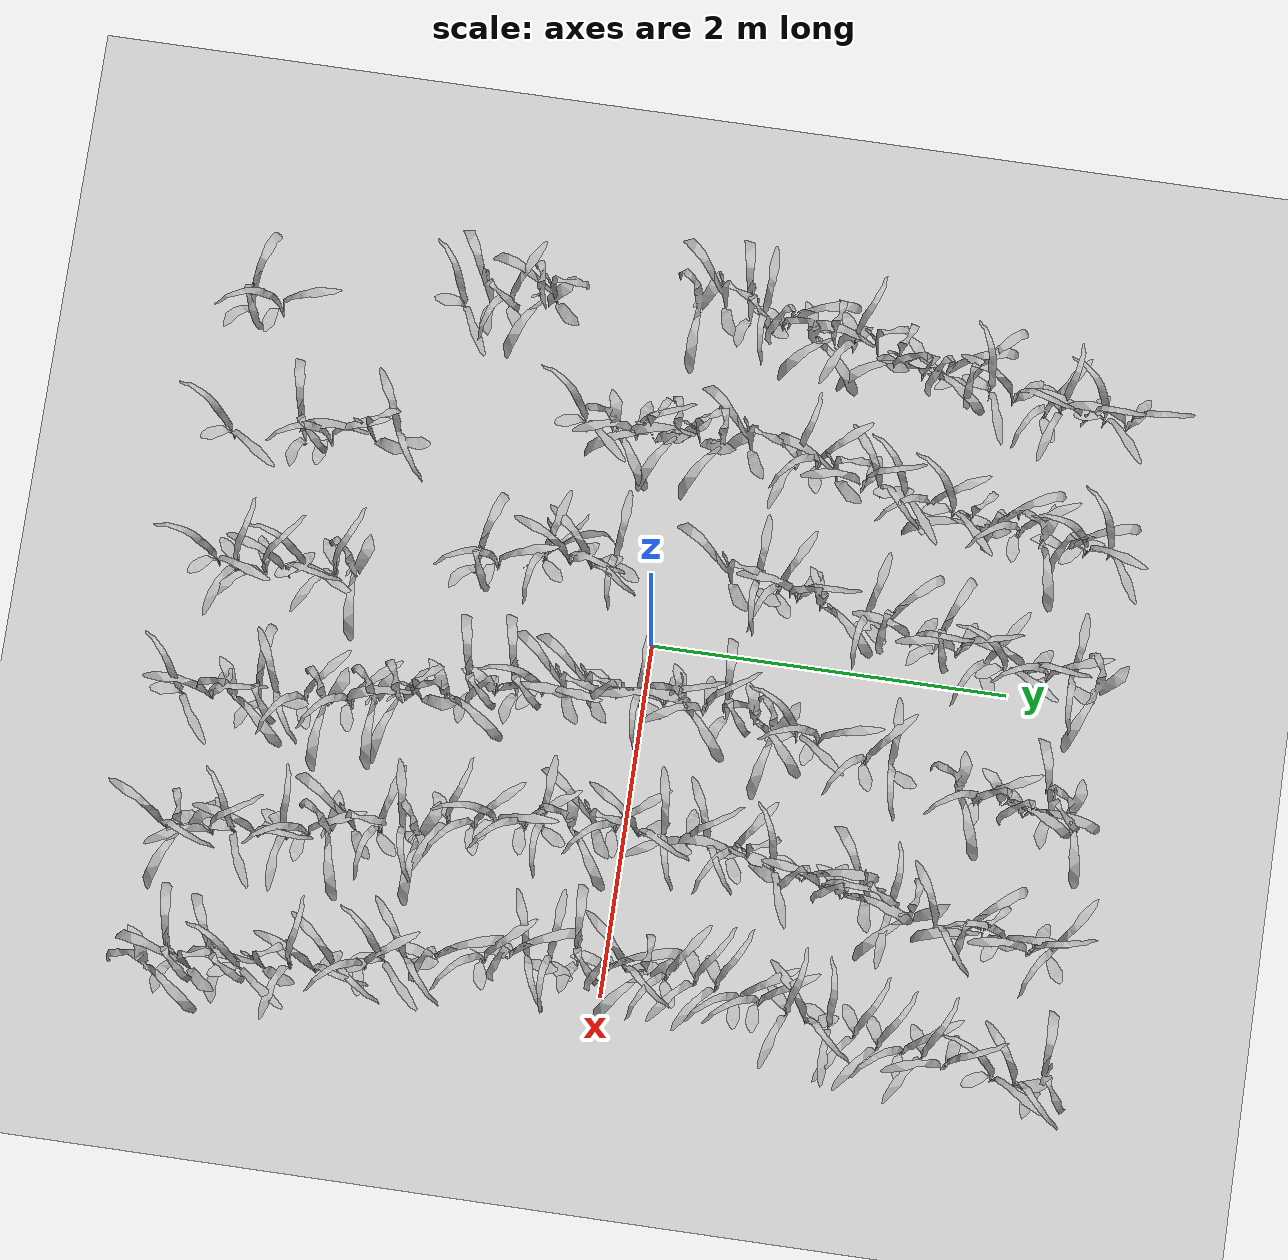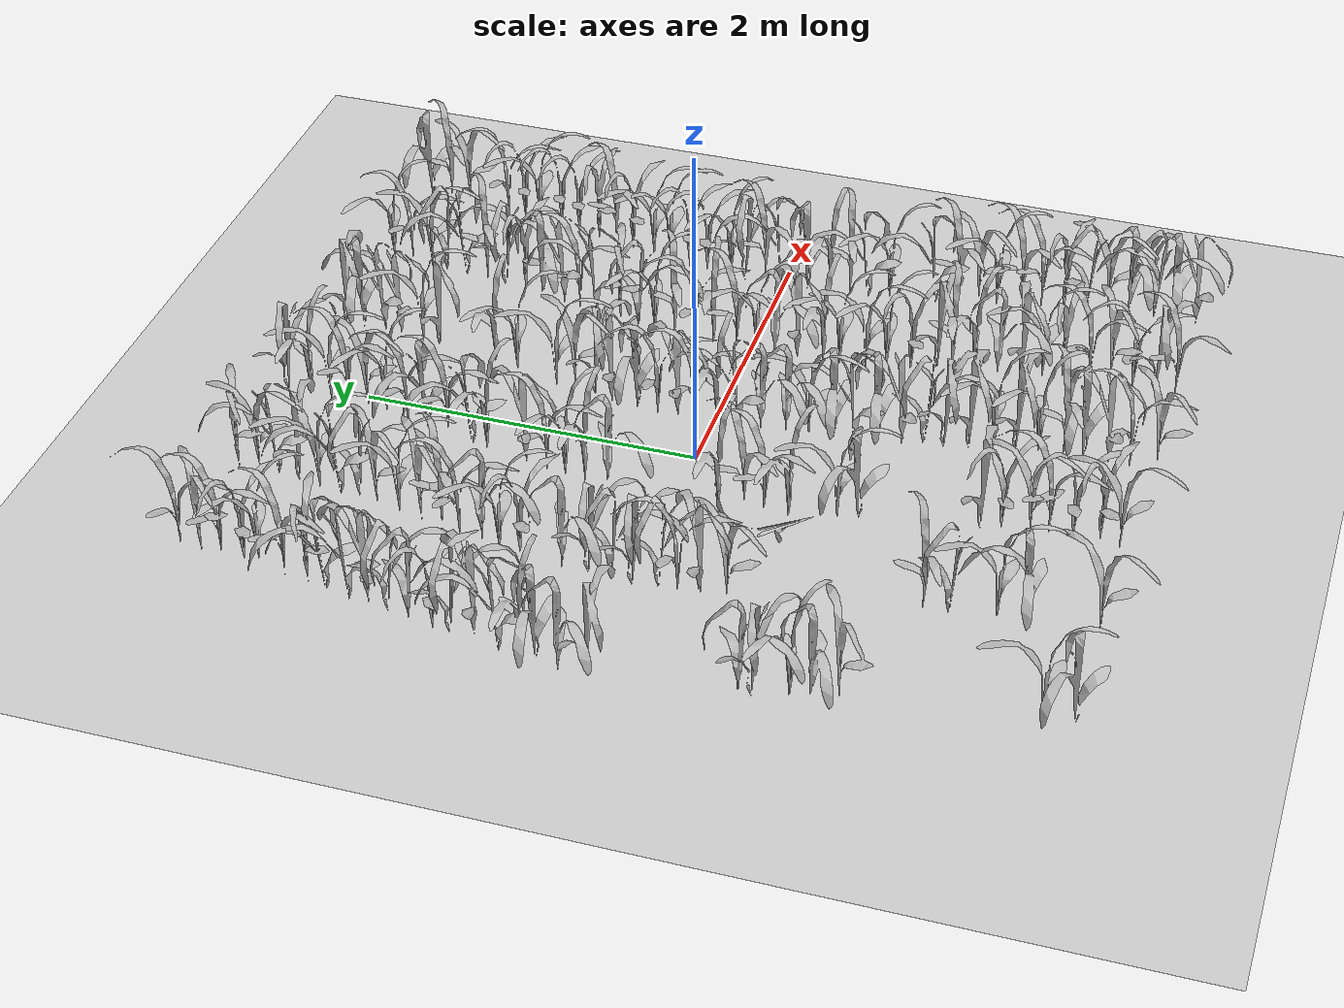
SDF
<sdf version="1.7">
 <world name="default">
  <light name="sun" type="directional">
   <pose>0 0 10 0 -0 0</pose>
   <diffuse>0.8 0.8 0.8 1</diffuse>
   <specular>0.2 0.2 0.2 1</specular>
   <attenuation>
    <range>1000</range>
    <constant>0.9</constant>
    <linear>0.01</linear>
    <quadratic>0.001</quadratic>
   </attenuation>
   <direction>-0.5 0.1 -0.9</direction>
   <spot><inner_angle>0</inner_angle><outer_angle>0</outer_angle><falloff>0</falloff></spot>
  </light>
  <gravity>0 0 -9.8</gravity>
  <magnetic_field>6e-06 2.3e-05 -4.2e-05</magnetic_field>
  <atmosphere type="adiabatic"/>
  <physics name="default_physics" default="0" type="ode">
   <max_step_size>0.005</max_step_size>
   <real_time_factor>1</real_time_factor>
   <real_time_update_rate>200</real_time_update_rate>
  </physics>
  <scene>
   <sky><clouds><speed>12</speed></clouds></sky>
   <ambient>0.4 0.4 0.4 1</ambient>
   <background>0.7 0.7 0.7 1</background>
   <grid>0</grid>
   <shadows>1</shadows>
  </scene>
  <audio><device>default</device></audio>
  <spherical_coordinates>
   <surface_model>EARTH_WGS84</surface_model>
   <latitude_deg>0</latitude_deg>
   <longitude_deg>0</longitude_deg>
   <elevation>0</elevation>
   <heading_deg>0</heading_deg>
  </spherical_coordinates>
  <model name="maize_01_0000">
   <pose>-1.56238 -2.49744 -0.000245 -1.1e-05 1.2e-05 -2.61309</pose>
   <link name="maize_01_link">
    <inertial>
     <pose>0 0 0.01 0 -0 0</pose>
     <mass>0.3</mass>
     <inertia>
      <ixx>0.00334167</ixx>
      <ixy>0</ixy>
      <ixz>0</ixz>
      <iyy>0.00334167</iyy>
      <iyz>0</iyz>
      <izz>1.66667e-05</izz>
     </inertia>
     <pose>0 0 0.1 0 -0 0</pose>
    </inertial>
    <collision name="collision">
     <pose>0 0 0.2 0 -0 0</pose>
     <geometry><box><size>0.02 0.02 0.4</size></box></geometry>
     <surface><friction><ode><mu>10</mu><mu2>10</mu2></ode></friction></surface>
    </collision>
    <visual name="visual">
     <geometry>
      <mesh><uri>model://maize_01/meshes/maize_01.dae</uri><scale>0.683166 0.683166 0.683166</scale></mesh>
     </geometry>
    </visual>
   </link>
   <static>0</static>
  </model>
  <model name="maize_02_0001">
   <pose>-1.57449 -2.3333 -0.000245 -1.2e-05 1.1e-05 -2.29259</pose>
   <link name="maize_02_link">
    <inertial>
     <pose>0 0 0.01 0 -0 0</pose>
     <mass>0.3</mass>
     <inertia>
      <ixx>0.00334167</ixx>
      <ixy>0</ixy>
      <ixz>0</ixz>
      <iyy>0.00334167</iyy>
      <iyz>0</iyz>
      <izz>1.66667e-05</izz>
     </inertia>
     <pose>0 0 0.1 0 -0 0</pose>
    </inertial>
    <collision name="collision">
     <pose>0 0 0.2 0 -0 0</pose>
     <geometry><box><size>0.02 0.02 0.4</size></box></geometry>
     <surface><friction><ode><mu>10</mu><mu2>10</mu2></ode></friction></surface>
    </collision>
    <visual name="visual">
     <geometry>
      <mesh><uri>model://maize_02/meshes/maize_02.dae</uri><scale>0.683166 0.683166 0.683166</scale></mesh>
     </geometry>
    </visual>
   </link>
   <static>0</static>
  </model>
  <model name="maize_02_0002">
   <pose>-1.71635 -1.30596 -1e-06 -6e-06 9.6e-05 2.65717</pose>
   <link name="maize_02_link">
    <inertial>
     <pose>0 0 0.01 0 -0 0</pose>
     <mass>0.3</mass>
     <inertia>
      <ixx>0.00334167</ixx>
      <ixy>0</ixy>
      <ixz>0</ixz>
      <iyy>0.00334167</iyy>
      <iyz>0</iyz>
      <izz>1.66667e-05</izz>
     </inertia>
     <pose>0 0 0.1 0 -0 0</pose>
    </inertial>
    <collision name="collision">
     <pose>0 0 0.2 0 -0 0</pose>
     <geometry><box><size>0.02 0.02 0.4</size></box></geometry>
     <surface><friction><ode><mu>10</mu><mu2>10</mu2></ode></friction></surface>
    </collision>
    <visual name="visual">
     <geometry>
      <mesh><uri>model://maize_02/meshes/maize_02.dae</uri><scale>0.683166 0.683166 0.683166</scale></mesh>
     </geometry>
    </visual>
   </link>
   <static>0</static>
  </model>
  <model name="maize_01_0003">
   <pose>-1.77135 -1.1665 -1e-06 6e-06 -9.6e-05 -1.87712</pose>
   <link name="maize_01_link">
    <inertial>
     <pose>0 0 0.01 0 -0 0</pose>
     <mass>0.3</mass>
     <inertia>
      <ixx>0.00334167</ixx>
      <ixy>0</ixy>
      <ixz>0</ixz>
      <iyy>0.00334167</iyy>
      <iyz>0</iyz>
      <izz>1.66667e-05</izz>
     </inertia>
     <pose>0 0 0.1 0 -0 0</pose>
    </inertial>
    <collision name="collision">
     <pose>0 0 0.2 0 -0 0</pose>
     <geometry><box><size>0.02 0.02 0.4</size></box></geometry>
     <surface><friction><ode><mu>10</mu><mu2>10</mu2></ode></friction></surface>
    </collision>
    <visual name="visual">
     <geometry>
      <mesh><uri>model://maize_01/meshes/maize_01.dae</uri><scale>0.683166 0.683166 0.683166</scale></mesh>
     </geometry>
    </visual>
   </link>
   <static>0</static>
  </model>
  <model name="maize_02_0004">
   <pose>-1.7847 -1.05874 -0.000245 -1.2e-05 -1.2e-05 -1.43268</pose>
   <link name="maize_02_link">
    <inertial>
     <pose>0 0 0.01 0 -0 0</pose>
     <mass>0.3</mass>
     <inertia>
      <ixx>0.00334167</ixx>
      <ixy>0</ixy>
      <ixz>0</ixz>
      <iyy>0.00334167</iyy>
      <iyz>0</iyz>
      <izz>1.66667e-05</izz>
     </inertia>
     <pose>0 0 0.1 0 -0 0</pose>
    </inertial>
    <collision name="collision">
     <pose>0 0 0.2 0 -0 0</pose>
     <geometry><box><size>0.02 0.02 0.4</size></box></geometry>
     <surface><friction><ode><mu>10</mu><mu2>10</mu2></ode></friction></surface>
    </collision>
    <visual name="visual">
     <geometry>
      <mesh><uri>model://maize_02/meshes/maize_02.dae</uri><scale>0.683166 0.683166 0.683166</scale></mesh>
     </geometry>
    </visual>
   </link>
   <static>0</static>
  </model>
  <model name="maize_01_0005">
   <pose>-1.82976 -0.870115 -0.000245 -1.1e-05 1.2e-05 0.373501</pose>
   <link name="maize_01_link">
    <inertial>
     <pose>0 0 0.01 0 -0 0</pose>
     <mass>0.3</mass>
     <inertia>
      <ixx>0.00334167</ixx>
      <ixy>0</ixy>
      <ixz>0</ixz>
      <iyy>0.00334167</iyy>
      <iyz>0</iyz>
      <izz>1.66667e-05</izz>
     </inertia>
     <pose>0 0 0.1 0 -0 0</pose>
    </inertial>
    <collision name="collision">
     <pose>0 0 0.2 0 -0 0</pose>
     <geometry><box><size>0.02 0.02 0.4</size></box></geometry>
     <surface><friction><ode><mu>10</mu><mu2>10</mu2></ode></friction></surface>
    </collision>
    <visual name="visual">
     <geometry>
      <mesh><uri>model://maize_01/meshes/maize_01.dae</uri><scale>0.683166 0.683166 0.683166</scale></mesh>
     </geometry>
    </visual>
   </link>
   <static>0</static>
  </model>
  <model name="maize_01_0006">
   <pose>-1.842 -0.800149 -0.000245 -1.2e-05 -1.2e-05 -1.18066</pose>
   <link name="maize_01_link">
    <inertial>
     <pose>0 0 0.01 0 -0 0</pose>
     <mass>0.3</mass>
     <inertia>
      <ixx>0.00334167</ixx>
      <ixy>0</ixy>
      <ixz>0</ixz>
      <iyy>0.00334167</iyy>
      <iyz>0</iyz>
      <izz>1.66667e-05</izz>
     </inertia>
     <pose>0 0 0.1 0 -0 0</pose>
    </inertial>
    <collision name="collision">
     <pose>0 0 0.2 0 -0 0</pose>
     <geometry><box><size>0.02 0.02 0.4</size></box></geometry>
     <surface><friction><ode><mu>10</mu><mu2>10</mu2></ode></friction></surface>
    </collision>
    <visual name="visual">
     <geometry>
      <mesh><uri>model://maize_01/meshes/maize_01.dae</uri><scale>0.683166 0.683166 0.683166</scale></mesh>
     </geometry>
    </visual>
   </link>
   <static>0</static>
  </model>
  <model name="maize_01_0007">
   <pose>-1.92135 -0.009355 -0.000245 1.2e-05 1.2e-05 0.784979</pose>
   <link name="maize_01_link">
    <inertial>
     <pose>0 0 0.01 0 -0 0</pose>
     <mass>0.3</mass>
     <inertia>
      <ixx>0.00334167</ixx>
      <ixy>0</ixy>
      <ixz>0</ixz>
      <iyy>0.00334167</iyy>
      <iyz>0</iyz>
      <izz>1.66667e-05</izz>
     </inertia>
     <pose>0 0 0.1 0 -0 0</pose>
    </inertial>
    <collision name="collision">
     <pose>0 0 0.2 0 -0 0</pose>
     <geometry><box><size>0.02 0.02 0.4</size></box></geometry>
     <surface><friction><ode><mu>10</mu><mu2>10</mu2></ode></friction></surface>
    </collision>
    <visual name="visual">
     <geometry>
      <mesh><uri>model://maize_01/meshes/maize_01.dae</uri><scale>0.683166 0.683166 0.683166</scale></mesh>
     </geometry>
    </visual>
   </link>
   <static>0</static>
  </model>
  <model name="maize_01_0008">
   <pose>-1.9509 0.143433 -0.000245 1.2e-05 -1.2e-05 -1.60922</pose>
   <link name="maize_01_link">
    <inertial>
     <pose>0 0 0.01 0 -0 0</pose>
     <mass>0.3</mass>
     <inertia>
      <ixx>0.00334167</ixx>
      <ixy>0</ixy>
      <ixz>0</ixz>
      <iyy>0.00334167</iyy>
      <iyz>0</iyz>
      <izz>1.66667e-05</izz>
     </inertia>
     <pose>0 0 0.1 0 -0 0</pose>
    </inertial>
    <collision name="collision">
     <pose>0 0 0.2 0 -0 0</pose>
     <geometry><box><size>0.02 0.02 0.4</size></box></geometry>
     <surface><friction><ode><mu>10</mu><mu2>10</mu2></ode></friction></surface>
    </collision>
    <visual name="visual">
     <geometry>
      <mesh><uri>model://maize_01/meshes/maize_01.dae</uri><scale>0.683166 0.683166 0.683166</scale></mesh>
     </geometry>
    </visual>
   </link>
   <static>0</static>
  </model>
  <model name="maize_01_0009">
   <pose>-1.89553 0.285762 -0.000245 1.2e-05 1.2e-05 -2.18216</pose>
   <link name="maize_01_link">
    <inertial>
     <pose>0 0 0.01 0 -0 0</pose>
     <mass>0.3</mass>
     <inertia>
      <ixx>0.00334167</ixx>
      <ixy>0</ixy>
      <ixz>0</ixz>
      <iyy>0.00334167</iyy>
      <iyz>0</iyz>
      <izz>1.66667e-05</izz>
     </inertia>
     <pose>0 0 0.1 0 -0 0</pose>
    </inertial>
    <collision name="collision">
     <pose>0 0 0.2 0 -0 0</pose>
     <geometry><box><size>0.02 0.02 0.4</size></box></geometry>
     <surface><friction><ode><mu>10</mu><mu2>10</mu2></ode></friction></surface>
    </collision>
    <visual name="visual">
     <geometry>
      <mesh><uri>model://maize_01/meshes/maize_01.dae</uri><scale>0.683166 0.683166 0.683166</scale></mesh>
     </geometry>
    </visual>
   </link>
   <static>0</static>
  </model>
  <model name="maize_02_0010">
   <pose>-1.90039 0.365939 -0.000245 1.2e-05 1.2e-05 -0.996438</pose>
   <link name="maize_02_link">
    <inertial>
     <pose>0 0 0.01 0 -0 0</pose>
     <mass>0.3</mass>
     <inertia>
      <ixx>0.00334167</ixx>
      <ixy>0</ixy>
      <ixz>0</ixz>
      <iyy>0.00334167</iyy>
      <iyz>0</iyz>
      <izz>1.66667e-05</izz>
     </inertia>
     <pose>0 0 0.1 0 -0 0</pose>
    </inertial>
    <collision name="collision">
     <pose>0 0 0.2 0 -0 0</pose>
     <geometry><box><size>0.02 0.02 0.4</size></box></geometry>
     <surface><friction><ode><mu>10</mu><mu2>10</mu2></ode></friction></surface>
    </collision>
    <visual name="visual">
     <geometry>
      <mesh><uri>model://maize_02/meshes/maize_02.dae</uri><scale>0.683166 0.683166 0.683166</scale></mesh>
     </geometry>
    </visual>
   </link>
   <static>0</static>
  </model>
  <model name="maize_01_0011">
   <pose>-1.8856 0.494207 -0.000245 -1.2e-05 -1.2e-05 2.62596</pose>
   <link name="maize_01_link">
    <inertial>
     <pose>0 0 0.01 0 -0 0</pose>
     <mass>0.3</mass>
     <inertia>
      <ixx>0.00334167</ixx>
      <ixy>0</ixy>
      <ixz>0</ixz>
      <iyy>0.00334167</iyy>
      <iyz>0</iyz>
      <izz>1.66667e-05</izz>
     </inertia>
     <pose>0 0 0.1 0 -0 0</pose>
    </inertial>
    <collision name="collision">
     <pose>0 0 0.2 0 -0 0</pose>
     <geometry><box><size>0.02 0.02 0.4</size></box></geometry>
     <surface><friction><ode><mu>10</mu><mu2>10</mu2></ode></friction></surface>
    </collision>
    <visual name="visual">
     <geometry>
      <mesh><uri>model://maize_01/meshes/maize_01.dae</uri><scale>0.683166 0.683166 0.683166</scale></mesh>
     </geometry>
    </visual>
   </link>
   <static>0</static>
  </model>
  <model name="maize_01_0012">
   <pose>-1.81598 0.647176 -0.000245 1.2e-05 -1.2e-05 1.52255</pose>
   <link name="maize_01_link">
    <inertial>
     <pose>0 0 0.01 0 -0 0</pose>
     <mass>0.3</mass>
     <inertia>
      <ixx>0.00334167</ixx>
      <ixy>0</ixy>
      <ixz>0</ixz>
      <iyy>0.00334167</iyy>
      <iyz>0</iyz>
      <izz>1.66667e-05</izz>
     </inertia>
     <pose>0 0 0.1 0 -0 0</pose>
    </inertial>
    <collision name="collision">
     <pose>0 0 0.2 0 -0 0</pose>
     <geometry><box><size>0.02 0.02 0.4</size></box></geometry>
     <surface><friction><ode><mu>10</mu><mu2>10</mu2></ode></friction></surface>
    </collision>
    <visual name="visual">
     <geometry>
      <mesh><uri>model://maize_01/meshes/maize_01.dae</uri><scale>0.683166 0.683166 0.683166</scale></mesh>
     </geometry>
    </visual>
   </link>
   <static>0</static>
  </model>
  <model name="maize_01_0013">
   <pose>-1.83843 0.779981 -1e-06 9.6e-05 6e-06 0.008121</pose>
   <link name="maize_01_link">
    <inertial>
     <pose>0 0 0.01 0 -0 0</pose>
     <mass>0.3</mass>
     <inertia>
      <ixx>0.00334167</ixx>
      <ixy>0</ixy>
      <ixz>0</ixz>
      <iyy>0.00334167</iyy>
      <iyz>0</iyz>
      <izz>1.66667e-05</izz>
     </inertia>
     <pose>0 0 0.1 0 -0 0</pose>
    </inertial>
    <collision name="collision">
     <pose>0 0 0.2 0 -0 0</pose>
     <geometry><box><size>0.02 0.02 0.4</size></box></geometry>
     <surface><friction><ode><mu>10</mu><mu2>10</mu2></ode></friction></surface>
    </collision>
    <visual name="visual">
     <geometry>
      <mesh><uri>model://maize_01/meshes/maize_01.dae</uri><scale>0.683166 0.683166 0.683166</scale></mesh>
     </geometry>
    </visual>
   </link>
   <static>0</static>
  </model>
  <model name="maize_02_0014">
   <pose>-1.82657 0.882907 -1e-06 6e-06 -9.6e-05 1.70873</pose>
   <link name="maize_02_link">
    <inertial>
     <pose>0 0 0.01 0 -0 0</pose>
     <mass>0.3</mass>
     <inertia>
      <ixx>0.00334167</ixx>
      <ixy>0</ixy>
      <ixz>0</ixz>
      <iyy>0.00334167</iyy>
      <iyz>0</iyz>
      <izz>1.66667e-05</izz>
     </inertia>
     <pose>0 0 0.1 0 -0 0</pose>
    </inertial>
    <collision name="collision">
     <pose>0 0 0.2 0 -0 0</pose>
     <geometry><box><size>0.02 0.02 0.4</size></box></geometry>
     <surface><friction><ode><mu>10</mu><mu2>10</mu2></ode></friction></surface>
    </collision>
    <visual name="visual">
     <geometry>
      <mesh><uri>model://maize_02/meshes/maize_02.dae</uri><scale>0.683166 0.683166 0.683166</scale></mesh>
     </geometry>
    </visual>
   </link>
   <static>0</static>
  </model>
  <model name="maize_01_0015">
   <pose>-1.80222 1.02954 -1e-06 6e-06 -9.6e-05 -0.908979</pose>
   <link name="maize_01_link">
    <inertial>
     <pose>0 0 0.01 0 -0 0</pose>
     <mass>0.3</mass>
     <inertia>
      <ixx>0.00334167</ixx>
      <ixy>0</ixy>
      <ixz>0</ixz>
      <iyy>0.00334167</iyy>
      <iyz>0</iyz>
      <izz>1.66667e-05</izz>
     </inertia>
     <pose>0 0 0.1 0 -0 0</pose>
    </inertial>
    <collision name="collision">
     <pose>0 0 0.2 0 -0 0</pose>
     <geometry><box><size>0.02 0.02 0.4</size></box></geometry>
     <surface><friction><ode><mu>10</mu><mu2>10</mu2></ode></friction></surface>
    </collision>
    <visual name="visual">
     <geometry>
      <mesh><uri>model://maize_01/meshes/maize_01.dae</uri><scale>0.683166 0.683166 0.683166</scale></mesh>
     </geometry>
    </visual>
   </link>
   <static>0</static>
  </model>
  <model name="maize_01_0016">
   <pose>-1.76192 1.16295 -1e-06 9.6e-05 -6e-06 -0.188487</pose>
   <link name="maize_01_link">
    <inertial>
     <pose>0 0 0.01 0 -0 0</pose>
     <mass>0.3</mass>
     <inertia>
      <ixx>0.00334167</ixx>
      <ixy>0</ixy>
      <ixz>0</ixz>
      <iyy>0.00334167</iyy>
      <iyz>0</iyz>
      <izz>1.66667e-05</izz>
     </inertia>
     <pose>0 0 0.1 0 -0 0</pose>
    </inertial>
    <collision name="collision">
     <pose>0 0 0.2 0 -0 0</pose>
     <geometry><box><size>0.02 0.02 0.4</size></box></geometry>
     <surface><friction><ode><mu>10</mu><mu2>10</mu2></ode></friction></surface>
    </collision>
    <visual name="visual">
     <geometry>
      <mesh><uri>model://maize_01/meshes/maize_01.dae</uri><scale>0.683166 0.683166 0.683166</scale></mesh>
     </geometry>
    </visual>
   </link>
   <static>0</static>
  </model>
  <model name="maize_01_0017">
   <pose>-1.72241 1.29033 -1e-06 6e-06 -9.6e-05 1.79097</pose>
   <link name="maize_01_link">
    <inertial>
     <pose>0 0 0.01 0 -0 0</pose>
     <mass>0.3</mass>
     <inertia>
      <ixx>0.00334167</ixx>
      <ixy>0</ixy>
      <ixz>0</ixz>
      <iyy>0.00334167</iyy>
      <iyz>0</iyz>
      <izz>1.66667e-05</izz>
     </inertia>
     <pose>0 0 0.1 0 -0 0</pose>
    </inertial>
    <collision name="collision">
     <pose>0 0 0.2 0 -0 0</pose>
     <geometry><box><size>0.02 0.02 0.4</size></box></geometry>
     <surface><friction><ode><mu>10</mu><mu2>10</mu2></ode></friction></surface>
    </collision>
    <visual name="visual">
     <geometry>
      <mesh><uri>model://maize_01/meshes/maize_01.dae</uri><scale>0.683166 0.683166 0.683166</scale></mesh>
     </geometry>
    </visual>
   </link>
   <static>0</static>
  </model>
  <model name="maize_01_0018">
   <pose>-1.72402 1.40563 -1e-06 9.6e-05 -6e-06 2.69334</pose>
   <link name="maize_01_link">
    <inertial>
     <pose>0 0 0.01 0 -0 0</pose>
     <mass>0.3</mass>
     <inertia>
      <ixx>0.00334167</ixx>
      <ixy>0</ixy>
      <ixz>0</ixz>
      <iyy>0.00334167</iyy>
      <iyz>0</iyz>
      <izz>1.66667e-05</izz>
     </inertia>
     <pose>0 0 0.1 0 -0 0</pose>
    </inertial>
    <collision name="collision">
     <pose>0 0 0.2 0 -0 0</pose>
     <geometry><box><size>0.02 0.02 0.4</size></box></geometry>
     <surface><friction><ode><mu>10</mu><mu2>10</mu2></ode></friction></surface>
    </collision>
    <visual name="visual">
     <geometry>
      <mesh><uri>model://maize_01/meshes/maize_01.dae</uri><scale>0.683166 0.683166 0.683166</scale></mesh>
     </geometry>
    </visual>
   </link>
   <static>0</static>
  </model>
  <model name="maize_01_0019">
   <pose>-1.69623 1.55164 -1e-06 -9.6e-05 -6e-06 -3.10675</pose>
   <link name="maize_01_link">
    <inertial>
     <pose>0 0 0.01 0 -0 0</pose>
     <mass>0.3</mass>
     <inertia>
      <ixx>0.00334167</ixx>
      <ixy>0</ixy>
      <ixz>0</ixz>
      <iyy>0.00334167</iyy>
      <iyz>0</iyz>
      <izz>1.66667e-05</izz>
     </inertia>
     <pose>0 0 0.1 0 -0 0</pose>
    </inertial>
    <collision name="collision">
     <pose>0 0 0.2 0 -0 0</pose>
     <geometry><box><size>0.02 0.02 0.4</size></box></geometry>
     <surface><friction><ode><mu>10</mu><mu2>10</mu2></ode></friction></surface>
    </collision>
    <visual name="visual">
     <geometry>
      <mesh><uri>model://maize_01/meshes/maize_01.dae</uri><scale>0.683166 0.683166 0.683166</scale></mesh>
     </geometry>
    </visual>
   </link>
   <static>0</static>
  </model>
  <model name="maize_02_0020">
   <pose>-1.65175 1.67274 -1e-06 9.6e-05 -6e-06 2.45134</pose>
   <link name="maize_02_link">
    <inertial>
     <pose>0 0 0.01 0 -0 0</pose>
     <mass>0.3</mass>
     <inertia>
      <ixx>0.00334167</ixx>
      <ixy>0</ixy>
      <ixz>0</ixz>
      <iyy>0.00334167</iyy>
      <iyz>0</iyz>
      <izz>1.66667e-05</izz>
     </inertia>
     <pose>0 0 0.1 0 -0 0</pose>
    </inertial>
    <collision name="collision">
     <pose>0 0 0.2 0 -0 0</pose>
     <geometry><box><size>0.02 0.02 0.4</size></box></geometry>
     <surface><friction><ode><mu>10</mu><mu2>10</mu2></ode></friction></surface>
    </collision>
    <visual name="visual">
     <geometry>
      <mesh><uri>model://maize_02/meshes/maize_02.dae</uri><scale>0.683166 0.683166 0.683166</scale></mesh>
     </geometry>
    </visual>
   </link>
   <static>0</static>
  </model>
  <model name="maize_02_0021">
   <pose>-1.64759 1.81033 -1e-06 9.6e-05 6e-06 0.220981</pose>
   <link name="maize_02_link">
    <inertial>
     <pose>0 0 0.01 0 -0 0</pose>
     <mass>0.3</mass>
     <inertia>
      <ixx>0.00334167</ixx>
      <ixy>0</ixy>
      <ixz>0</ixz>
      <iyy>0.00334167</iyy>
      <iyz>0</iyz>
      <izz>1.66667e-05</izz>
     </inertia>
     <pose>0 0 0.1 0 -0 0</pose>
    </inertial>
    <collision name="collision">
     <pose>0 0 0.2 0 -0 0</pose>
     <geometry><box><size>0.02 0.02 0.4</size></box></geometry>
     <surface><friction><ode><mu>10</mu><mu2>10</mu2></ode></friction></surface>
    </collision>
    <visual name="visual">
     <geometry>
      <mesh><uri>model://maize_02/meshes/maize_02.dae</uri><scale>0.683166 0.683166 0.683166</scale></mesh>
     </geometry>
    </visual>
   </link>
   <static>0</static>
  </model>
  <model name="maize_02_0022">
   <pose>-1.57625 1.99395 -0.000245 1.2e-05 -1.2e-05 -1.58846</pose>
   <link name="maize_02_link">
    <inertial>
     <pose>0 0 0.01 0 -0 0</pose>
     <mass>0.3</mass>
     <inertia>
      <ixx>0.00334167</ixx>
      <ixy>0</ixy>
      <ixz>0</ixz>
      <iyy>0.00334167</iyy>
      <iyz>0</iyz>
      <izz>1.66667e-05</izz>
     </inertia>
     <pose>0 0 0.1 0 -0 0</pose>
    </inertial>
    <collision name="collision">
     <pose>0 0 0.2 0 -0 0</pose>
     <geometry><box><size>0.02 0.02 0.4</size></box></geometry>
     <surface><friction><ode><mu>10</mu><mu2>10</mu2></ode></friction></surface>
    </collision>
    <visual name="visual">
     <geometry>
      <mesh><uri>model://maize_02/meshes/maize_02.dae</uri><scale>0.683166 0.683166 0.683166</scale></mesh>
     </geometry>
    </visual>
   </link>
   <static>0</static>
  </model>
  <model name="maize_02_0023">
   <pose>-1.5879 2.07619 -0.000245 1.2e-05 1.2e-05 1.89579</pose>
   <link name="maize_02_link">
    <inertial>
     <pose>0 0 0.01 0 -0 0</pose>
     <mass>0.3</mass>
     <inertia>
      <ixx>0.00334167</ixx>
      <ixy>0</ixy>
      <ixz>0</ixz>
      <iyy>0.00334167</iyy>
      <iyz>0</iyz>
      <izz>1.66667e-05</izz>
     </inertia>
     <pose>0 0 0.1 0 -0 0</pose>
    </inertial>
    <collision name="collision">
     <pose>0 0 0.2 0 -0 0</pose>
     <geometry><box><size>0.02 0.02 0.4</size></box></geometry>
     <surface><friction><ode><mu>10</mu><mu2>10</mu2></ode></friction></surface>
    </collision>
    <visual name="visual">
     <geometry>
      <mesh><uri>model://maize_02/meshes/maize_02.dae</uri><scale>0.683166 0.683166 0.683166</scale></mesh>
     </geometry>
    </visual>
   </link>
   <static>0</static>
  </model>
  <model name="maize_02_0024">
   <pose>-1.58521 2.2133 -0.000245 -1.2e-05 1.2e-05 0.472824</pose>
   <link name="maize_02_link">
    <inertial>
     <pose>0 0 0.01 0 -0 0</pose>
     <mass>0.3</mass>
     <inertia>
      <ixx>0.00334167</ixx>
      <ixy>0</ixy>
      <ixz>0</ixz>
      <iyy>0.00334167</iyy>
      <iyz>0</iyz>
      <izz>1.66667e-05</izz>
     </inertia>
     <pose>0 0 0.1 0 -0 0</pose>
    </inertial>
    <collision name="collision">
     <pose>0 0 0.2 0 -0 0</pose>
     <geometry><box><size>0.02 0.02 0.4</size></box></geometry>
     <surface><friction><ode><mu>10</mu><mu2>10</mu2></ode></friction></surface>
    </collision>
    <visual name="visual">
     <geometry>
      <mesh><uri>model://maize_02/meshes/maize_02.dae</uri><scale>0.683166 0.683166 0.683166</scale></mesh>
     </geometry>
    </visual>
   </link>
   <static>0</static>
  </model>
  <model name="maize_02_0025">
   <pose>-1.5915 2.32881 -0.000245 1.2e-05 1.2e-05 2.84869</pose>
   <link name="maize_02_link">
    <inertial>
     <pose>0 0 0.01 0 -0 0</pose>
     <mass>0.3</mass>
     <inertia>
      <ixx>0.00334167</ixx>
      <ixy>0</ixy>
      <ixz>0</ixz>
      <iyy>0.00334167</iyy>
      <iyz>0</iyz>
      <izz>1.66667e-05</izz>
     </inertia>
     <pose>0 0 0.1 0 -0 0</pose>
    </inertial>
    <collision name="collision">
     <pose>0 0 0.2 0 -0 0</pose>
     <geometry><box><size>0.02 0.02 0.4</size></box></geometry>
     <surface><friction><ode><mu>10</mu><mu2>10</mu2></ode></friction></surface>
    </collision>
    <visual name="visual">
     <geometry>
      <mesh><uri>model://maize_02/meshes/maize_02.dae</uri><scale>0.683166 0.683166 0.683166</scale></mesh>
     </geometry>
    </visual>
   </link>
   <static>0</static>
  </model>
  <model name="maize_02_0026">
   <pose>-1.5801 2.45909 -0.000245 -1.2e-05 1.2e-05 0.59161</pose>
   <link name="maize_02_link">
    <inertial>
     <pose>0 0 0.01 0 -0 0</pose>
     <mass>0.3</mass>
     <inertia>
      <ixx>0.00334167</ixx>
      <ixy>0</ixy>
      <ixz>0</ixz>
      <iyy>0.00334167</iyy>
      <iyz>0</iyz>
      <izz>1.66667e-05</izz>
     </inertia>
     <pose>0 0 0.1 0 -0 0</pose>
    </inertial>
    <collision name="collision">
     <pose>0 0 0.2 0 -0 0</pose>
     <geometry><box><size>0.02 0.02 0.4</size></box></geometry>
     <surface><friction><ode><mu>10</mu><mu2>10</mu2></ode></friction></surface>
    </collision>
    <visual name="visual">
     <geometry>
      <mesh><uri>model://maize_02/meshes/maize_02.dae</uri><scale>0.683166 0.683166 0.683166</scale></mesh>
     </geometry>
    </visual>
   </link>
   <static>0</static>
  </model>
  <model name="maize_02_0027">
   <pose>-0.819779 -2.48896 -0.000245 1.2e-05 -1.2e-05 3.12581</pose>
   <link name="maize_02_link">
    <inertial>
     <pose>0 0 0.01 0 -0 0</pose>
     <mass>0.3</mass>
     <inertia>
      <ixx>0.00334167</ixx>
      <ixy>0</ixy>
      <ixz>0</ixz>
      <iyy>0.00334167</iyy>
      <iyz>0</iyz>
      <izz>1.66667e-05</izz>
     </inertia>
     <pose>0 0 0.1 0 -0 0</pose>
    </inertial>
    <collision name="collision">
     <pose>0 0 0.2 0 -0 0</pose>
     <geometry><box><size>0.02 0.02 0.4</size></box></geometry>
     <surface><friction><ode><mu>10</mu><mu2>10</mu2></ode></friction></surface>
    </collision>
    <visual name="visual">
     <geometry>
      <mesh><uri>model://maize_02/meshes/maize_02.dae</uri><scale>0.683166 0.683166 0.683166</scale></mesh>
     </geometry>
    </visual>
   </link>
   <static>0</static>
  </model>
  <model name="maize_01_0028">
   <pose>-0.861064 -2.08833 -0.000245 -1.2e-05 1.2e-05 -2.16184</pose>
   <link name="maize_01_link">
    <inertial>
     <pose>0 0 0.01 0 -0 0</pose>
     <mass>0.3</mass>
     <inertia>
      <ixx>0.00334167</ixx>
      <ixy>0</ixy>
      <ixz>0</ixz>
      <iyy>0.00334167</iyy>
      <iyz>0</iyz>
      <izz>1.66667e-05</izz>
     </inertia>
     <pose>0 0 0.1 0 -0 0</pose>
    </inertial>
    <collision name="collision">
     <pose>0 0 0.2 0 -0 0</pose>
     <geometry><box><size>0.02 0.02 0.4</size></box></geometry>
     <surface><friction><ode><mu>10</mu><mu2>10</mu2></ode></friction></surface>
    </collision>
    <visual name="visual">
     <geometry>
      <mesh><uri>model://maize_01/meshes/maize_01.dae</uri><scale>0.683166 0.683166 0.683166</scale></mesh>
     </geometry>
    </visual>
   </link>
   <static>0</static>
  </model>
  <model name="maize_02_0029">
   <pose>-0.866126 -1.94356 -0.000245 1.2e-05 1.2e-05 -2.22616</pose>
   <link name="maize_02_link">
    <inertial>
     <pose>0 0 0.01 0 -0 0</pose>
     <mass>0.3</mass>
     <inertia>
      <ixx>0.00334167</ixx>
      <ixy>0</ixy>
      <ixz>0</ixz>
      <iyy>0.00334167</iyy>
      <iyz>0</iyz>
      <izz>1.66667e-05</izz>
     </inertia>
     <pose>0 0 0.1 0 -0 0</pose>
    </inertial>
    <collision name="collision">
     <pose>0 0 0.2 0 -0 0</pose>
     <geometry><box><size>0.02 0.02 0.4</size></box></geometry>
     <surface><friction><ode><mu>10</mu><mu2>10</mu2></ode></friction></surface>
    </collision>
    <visual name="visual">
     <geometry>
      <mesh><uri>model://maize_02/meshes/maize_02.dae</uri><scale>0.683166 0.683166 0.683166</scale></mesh>
     </geometry>
    </visual>
   </link>
   <static>0</static>
  </model>
  <model name="maize_01_0031">
   <pose>-0.91153 -1.69245 -0.000245 -1.2e-05 -1.2e-05 -0.69003</pose>
   <link name="maize_01_link">
    <inertial>
     <pose>0 0 0.01 0 -0 0</pose>
     <mass>0.3</mass>
     <inertia>
      <ixx>0.00334167</ixx>
      <ixy>0</ixy>
      <ixz>0</ixz>
      <iyy>0.00334167</iyy>
      <iyz>0</iyz>
      <izz>1.66667e-05</izz>
     </inertia>
     <pose>0 0 0.1 0 -0 0</pose>
    </inertial>
    <collision name="collision">
     <pose>0 0 0.2 0 -0 0</pose>
     <geometry><box><size>0.02 0.02 0.4</size></box></geometry>
     <surface><friction><ode><mu>10</mu><mu2>10</mu2></ode></friction></surface>
    </collision>
    <visual name="visual">
     <geometry>
      <mesh><uri>model://maize_01/meshes/maize_01.dae</uri><scale>0.683166 0.683166 0.683166</scale></mesh>
     </geometry>
    </visual>
   </link>
   <static>0</static>
  </model>
  <model name="maize_02_0032">
   <pose>-0.927617 -1.55364 -0.000245 -1.2e-05 -1.2e-05 -0.512034</pose>
   <link name="maize_02_link">
    <inertial>
     <pose>0 0 0.01 0 -0 0</pose>
     <mass>0.3</mass>
     <inertia>
      <ixx>0.00334167</ixx>
      <ixy>0</ixy>
      <ixz>0</ixz>
      <iyy>0.00334167</iyy>
      <iyz>0</iyz>
      <izz>1.66667e-05</izz>
     </inertia>
     <pose>0 0 0.1 0 -0 0</pose>
    </inertial>
    <collision name="collision">
     <pose>0 0 0.2 0 -0 0</pose>
     <geometry><box><size>0.02 0.02 0.4</size></box></geometry>
     <surface><friction><ode><mu>10</mu><mu2>10</mu2></ode></friction></surface>
    </collision>
    <visual name="visual">
     <geometry>
      <mesh><uri>model://maize_02/meshes/maize_02.dae</uri><scale>0.683166 0.683166 0.683166</scale></mesh>
     </geometry>
    </visual>
   </link>
   <static>0</static>
  </model>
  <model name="maize_02_0033">
   <pose>-1.15936 -0.538884 -1e-06 9.6e-05 6e-06 2.99613</pose>
   <link name="maize_02_link">
    <inertial>
     <pose>0 0 0.01 0 -0 0</pose>
     <mass>0.3</mass>
     <inertia>
      <ixx>0.00334167</ixx>
      <ixy>0</ixy>
      <ixz>0</ixz>
      <iyy>0.00334167</iyy>
      <iyz>0</iyz>
      <izz>1.66667e-05</izz>
     </inertia>
     <pose>0 0 0.1 0 -0 0</pose>
    </inertial>
    <collision name="collision">
     <pose>0 0 0.2 0 -0 0</pose>
     <geometry><box><size>0.02 0.02 0.4</size></box></geometry>
     <surface><friction><ode><mu>10</mu><mu2>10</mu2></ode></friction></surface>
    </collision>
    <visual name="visual">
     <geometry>
      <mesh><uri>model://maize_02/meshes/maize_02.dae</uri><scale>0.683166 0.683166 0.683166</scale></mesh>
     </geometry>
    </visual>
   </link>
   <static>0</static>
  </model>
  <model name="maize_01_0034">
   <pose>-1.15095 -0.387124 -1e-06 -9.6e-05 -6e-06 1.37063</pose>
   <link name="maize_01_link">
    <inertial>
     <pose>0 0 0.01 0 -0 0</pose>
     <mass>0.3</mass>
     <inertia>
      <ixx>0.00334167</ixx>
      <ixy>0</ixy>
      <ixz>0</ixz>
      <iyy>0.00334167</iyy>
      <iyz>0</iyz>
      <izz>1.66667e-05</izz>
     </inertia>
     <pose>0 0 0.1 0 -0 0</pose>
    </inertial>
    <collision name="collision">
     <pose>0 0 0.2 0 -0 0</pose>
     <geometry><box><size>0.02 0.02 0.4</size></box></geometry>
     <surface><friction><ode><mu>10</mu><mu2>10</mu2></ode></friction></surface>
    </collision>
    <visual name="visual">
     <geometry>
      <mesh><uri>model://maize_01/meshes/maize_01.dae</uri><scale>0.683166 0.683166 0.683166</scale></mesh>
     </geometry>
    </visual>
   </link>
   <static>0</static>
  </model>
  <model name="maize_02_0035">
   <pose>-1.14788 -0.256612 -0.000245 1.2e-05 -1.1e-05 0.89574</pose>
   <link name="maize_02_link">
    <inertial>
     <pose>0 0 0.01 0 -0 0</pose>
     <mass>0.3</mass>
     <inertia>
      <ixx>0.00334167</ixx>
      <ixy>0</ixy>
      <ixz>0</ixz>
      <iyy>0.00334167</iyy>
      <iyz>0</iyz>
      <izz>1.66667e-05</izz>
     </inertia>
     <pose>0 0 0.1 0 -0 0</pose>
    </inertial>
    <collision name="collision">
     <pose>0 0 0.2 0 -0 0</pose>
     <geometry><box><size>0.02 0.02 0.4</size></box></geometry>
     <surface><friction><ode><mu>10</mu><mu2>10</mu2></ode></friction></surface>
    </collision>
    <visual name="visual">
     <geometry>
      <mesh><uri>model://maize_02/meshes/maize_02.dae</uri><scale>0.683166 0.683166 0.683166</scale></mesh>
     </geometry>
    </visual>
   </link>
   <static>0</static>
  </model>
  <model name="maize_01_0036">
   <pose>-1.15282 -0.150797 -0.000245 -1.2e-05 1.2e-05 -0.307279</pose>
   <link name="maize_01_link">
    <inertial>
     <pose>0 0 0.01 0 -0 0</pose>
     <mass>0.3</mass>
     <inertia>
      <ixx>0.00334167</ixx>
      <ixy>0</ixy>
      <ixz>0</ixz>
      <iyy>0.00334167</iyy>
      <iyz>0</iyz>
      <izz>1.66667e-05</izz>
     </inertia>
     <pose>0 0 0.1 0 -0 0</pose>
    </inertial>
    <collision name="collision">
     <pose>0 0 0.2 0 -0 0</pose>
     <geometry><box><size>0.02 0.02 0.4</size></box></geometry>
     <surface><friction><ode><mu>10</mu><mu2>10</mu2></ode></friction></surface>
    </collision>
    <visual name="visual">
     <geometry>
      <mesh><uri>model://maize_01/meshes/maize_01.dae</uri><scale>0.683166 0.683166 0.683166</scale></mesh>
     </geometry>
    </visual>
   </link>
   <static>0</static>
  </model>
  <model name="maize_01_0037">
   <pose>-1.1693 -0.007906 -0.000245 -1.2e-05 -1.2e-05 0.300907</pose>
   <link name="maize_01_link">
    <inertial>
     <pose>0 0 0.01 0 -0 0</pose>
     <mass>0.3</mass>
     <inertia>
      <ixx>0.00334167</ixx>
      <ixy>0</ixy>
      <ixz>0</ixz>
      <iyy>0.00334167</iyy>
      <iyz>0</iyz>
      <izz>1.66667e-05</izz>
     </inertia>
     <pose>0 0 0.1 0 -0 0</pose>
    </inertial>
    <collision name="collision">
     <pose>0 0 0.2 0 -0 0</pose>
     <geometry><box><size>0.02 0.02 0.4</size></box></geometry>
     <surface><friction><ode><mu>10</mu><mu2>10</mu2></ode></friction></surface>
    </collision>
    <visual name="visual">
     <geometry>
      <mesh><uri>model://maize_01/meshes/maize_01.dae</uri><scale>0.683166 0.683166 0.683166</scale></mesh>
     </geometry>
    </visual>
   </link>
   <static>0</static>
  </model>
  <model name="maize_01_0038">
   <pose>-1.16467 0.111374 -0.000245 1.1e-05 1.2e-05 -0.635661</pose>
   <link name="maize_01_link">
    <inertial>
     <pose>0 0 0.01 0 -0 0</pose>
     <mass>0.3</mass>
     <inertia>
      <ixx>0.00334167</ixx>
      <ixy>0</ixy>
      <ixz>0</ixz>
      <iyy>0.00334167</iyy>
      <iyz>0</iyz>
      <izz>1.66667e-05</izz>
     </inertia>
     <pose>0 0 0.1 0 -0 0</pose>
    </inertial>
    <collision name="collision">
     <pose>0 0 0.2 0 -0 0</pose>
     <geometry><box><size>0.02 0.02 0.4</size></box></geometry>
     <surface><friction><ode><mu>10</mu><mu2>10</mu2></ode></friction></surface>
    </collision>
    <visual name="visual">
     <geometry>
      <mesh><uri>model://maize_01/meshes/maize_01.dae</uri><scale>0.683166 0.683166 0.683166</scale></mesh>
     </geometry>
    </visual>
   </link>
   <static>0</static>
  </model>
  <model name="maize_01_0039">
   <pose>-1.14613 0.247645 -0.000245 -1.2e-05 -1.2e-05 0.257209</pose>
   <link name="maize_01_link">
    <inertial>
     <pose>0 0 0.01 0 -0 0</pose>
     <mass>0.3</mass>
     <inertia>
      <ixx>0.00334167</ixx>
      <ixy>0</ixy>
      <ixz>0</ixz>
      <iyy>0.00334167</iyy>
      <iyz>0</iyz>
      <izz>1.66667e-05</izz>
     </inertia>
     <pose>0 0 0.1 0 -0 0</pose>
    </inertial>
    <collision name="collision">
     <pose>0 0 0.2 0 -0 0</pose>
     <geometry><box><size>0.02 0.02 0.4</size></box></geometry>
     <surface><friction><ode><mu>10</mu><mu2>10</mu2></ode></friction></surface>
    </collision>
    <visual name="visual">
     <geometry>
      <mesh><uri>model://maize_01/meshes/maize_01.dae</uri><scale>0.683166 0.683166 0.683166</scale></mesh>
     </geometry>
    </visual>
   </link>
   <static>0</static>
  </model>
  <model name="maize_01_0040">
   <pose>-1.15618 0.400067 -0.000245 1.2e-05 -1.2e-05 -1.50842</pose>
   <link name="maize_01_link">
    <inertial>
     <pose>0 0 0.01 0 -0 0</pose>
     <mass>0.3</mass>
     <inertia>
      <ixx>0.00334167</ixx>
      <ixy>0</ixy>
      <ixz>0</ixz>
      <iyy>0.00334167</iyy>
      <iyz>0</iyz>
      <izz>1.66667e-05</izz>
     </inertia>
     <pose>0 0 0.1 0 -0 0</pose>
    </inertial>
    <collision name="collision">
     <pose>0 0 0.2 0 -0 0</pose>
     <geometry><box><size>0.02 0.02 0.4</size></box></geometry>
     <surface><friction><ode><mu>10</mu><mu2>10</mu2></ode></friction></surface>
    </collision>
    <visual name="visual">
     <geometry>
      <mesh><uri>model://maize_01/meshes/maize_01.dae</uri><scale>0.683166 0.683166 0.683166</scale></mesh>
     </geometry>
    </visual>
   </link>
   <static>0</static>
  </model>
  <model name="maize_02_0042">
   <pose>-1.10178 0.656245 -0.000245 -1.2e-05 1.2e-05 1.84231</pose>
   <link name="maize_02_link">
    <inertial>
     <pose>0 0 0.01 0 -0 0</pose>
     <mass>0.3</mass>
     <inertia>
      <ixx>0.00334167</ixx>
      <ixy>0</ixy>
      <ixz>0</ixz>
      <iyy>0.00334167</iyy>
      <iyz>0</iyz>
      <izz>1.66667e-05</izz>
     </inertia>
     <pose>0 0 0.1 0 -0 0</pose>
    </inertial>
    <collision name="collision">
     <pose>0 0 0.2 0 -0 0</pose>
     <geometry><box><size>0.02 0.02 0.4</size></box></geometry>
     <surface><friction><ode><mu>10</mu><mu2>10</mu2></ode></friction></surface>
    </collision>
    <visual name="visual">
     <geometry>
      <mesh><uri>model://maize_02/meshes/maize_02.dae</uri><scale>0.683166 0.683166 0.683166</scale></mesh>
     </geometry>
    </visual>
   </link>
   <static>0</static>
  </model>
  <model name="maize_02_0043">
   <pose>-1.10867 0.775027 -0.000245 -1.2e-05 -1.2e-05 -1.85117</pose>
   <link name="maize_02_link">
    <inertial>
     <pose>0 0 0.01 0 -0 0</pose>
     <mass>0.3</mass>
     <inertia>
      <ixx>0.00334167</ixx>
      <ixy>0</ixy>
      <ixz>0</ixz>
      <iyy>0.00334167</iyy>
      <iyz>0</iyz>
      <izz>1.66667e-05</izz>
     </inertia>
     <pose>0 0 0.1 0 -0 0</pose>
    </inertial>
    <collision name="collision">
     <pose>0 0 0.2 0 -0 0</pose>
     <geometry><box><size>0.02 0.02 0.4</size></box></geometry>
     <surface><friction><ode><mu>10</mu><mu2>10</mu2></ode></friction></surface>
    </collision>
    <visual name="visual">
     <geometry>
      <mesh><uri>model://maize_02/meshes/maize_02.dae</uri><scale>0.683166 0.683166 0.683166</scale></mesh>
     </geometry>
    </visual>
   </link>
   <static>0</static>
  </model>
  <model name="maize_01_0044">
   <pose>-1.0532 0.898506 -1e-06 9.6e-05 6e-06 -1.13722</pose>
   <link name="maize_01_link">
    <inertial>
     <pose>0 0 0.01 0 -0 0</pose>
     <mass>0.3</mass>
     <inertia>
      <ixx>0.00334167</ixx>
      <ixy>0</ixy>
      <ixz>0</ixz>
      <iyy>0.00334167</iyy>
      <iyz>0</iyz>
      <izz>1.66667e-05</izz>
     </inertia>
     <pose>0 0 0.1 0 -0 0</pose>
    </inertial>
    <collision name="collision">
     <pose>0 0 0.2 0 -0 0</pose>
     <geometry><box><size>0.02 0.02 0.4</size></box></geometry>
     <surface><friction><ode><mu>10</mu><mu2>10</mu2></ode></friction></surface>
    </collision>
    <visual name="visual">
     <geometry>
      <mesh><uri>model://maize_01/meshes/maize_01.dae</uri><scale>0.683166 0.683166 0.683166</scale></mesh>
     </geometry>
    </visual>
   </link>
   <static>0</static>
  </model>
  <model name="maize_02_0045">
   <pose>-1.03061 1.03904 -0.000245 1.2e-05 -1.2e-05 0.769904</pose>
   <link name="maize_02_link">
    <inertial>
     <pose>0 0 0.01 0 -0 0</pose>
     <mass>0.3</mass>
     <inertia>
      <ixx>0.00334167</ixx>
      <ixy>0</ixy>
      <ixz>0</ixz>
      <iyy>0.00334167</iyy>
      <iyz>0</iyz>
      <izz>1.66667e-05</izz>
     </inertia>
     <pose>0 0 0.1 0 -0 0</pose>
    </inertial>
    <collision name="collision">
     <pose>0 0 0.2 0 -0 0</pose>
     <geometry><box><size>0.02 0.02 0.4</size></box></geometry>
     <surface><friction><ode><mu>10</mu><mu2>10</mu2></ode></friction></surface>
    </collision>
    <visual name="visual">
     <geometry>
      <mesh><uri>model://maize_02/meshes/maize_02.dae</uri><scale>0.683166 0.683166 0.683166</scale></mesh>
     </geometry>
    </visual>
   </link>
   <static>0</static>
  </model>
  <model name="maize_02_0046">
   <pose>-1.01765 1.14701 -0.000245 1.1e-05 1.2e-05 -0.343145</pose>
   <link name="maize_02_link">
    <inertial>
     <pose>0 0 0.01 0 -0 0</pose>
     <mass>0.3</mass>
     <inertia>
      <ixx>0.00334167</ixx>
      <ixy>0</ixy>
      <ixz>0</ixz>
      <iyy>0.00334167</iyy>
      <iyz>0</iyz>
      <izz>1.66667e-05</izz>
     </inertia>
     <pose>0 0 0.1 0 -0 0</pose>
    </inertial>
    <collision name="collision">
     <pose>0 0 0.2 0 -0 0</pose>
     <geometry><box><size>0.02 0.02 0.4</size></box></geometry>
     <surface><friction><ode><mu>10</mu><mu2>10</mu2></ode></friction></surface>
    </collision>
    <visual name="visual">
     <geometry>
      <mesh><uri>model://maize_02/meshes/maize_02.dae</uri><scale>0.683166 0.683166 0.683166</scale></mesh>
     </geometry>
    </visual>
   </link>
   <static>0</static>
  </model>
  <model name="maize_02_0047">
   <pose>-0.987214 1.27886 -0.000245 1.2e-05 1.2e-05 2.8039</pose>
   <link name="maize_02_link">
    <inertial>
     <pose>0 0 0.01 0 -0 0</pose>
     <mass>0.3</mass>
     <inertia>
      <ixx>0.00334167</ixx>
      <ixy>0</ixy>
      <ixz>0</ixz>
      <iyy>0.00334167</iyy>
      <iyz>0</iyz>
      <izz>1.66667e-05</izz>
     </inertia>
     <pose>0 0 0.1 0 -0 0</pose>
    </inertial>
    <collision name="collision">
     <pose>0 0 0.2 0 -0 0</pose>
     <geometry><box><size>0.02 0.02 0.4</size></box></geometry>
     <surface><friction><ode><mu>10</mu><mu2>10</mu2></ode></friction></surface>
    </collision>
    <visual name="visual">
     <geometry>
      <mesh><uri>model://maize_02/meshes/maize_02.dae</uri><scale>0.683166 0.683166 0.683166</scale></mesh>
     </geometry>
    </visual>
   </link>
   <static>0</static>
  </model>
  <model name="maize_02_0048">
   <pose>-0.957863 1.42256 -1e-06 -6e-06 -9.6e-05 -2.04162</pose>
   <link name="maize_02_link">
    <inertial>
     <pose>0 0 0.01 0 -0 0</pose>
     <mass>0.3</mass>
     <inertia>
      <ixx>0.00334167</ixx>
      <ixy>0</ixy>
      <ixz>0</ixz>
      <iyy>0.00334167</iyy>
      <iyz>0</iyz>
      <izz>1.66667e-05</izz>
     </inertia>
     <pose>0 0 0.1 0 -0 0</pose>
    </inertial>
    <collision name="collision">
     <pose>0 0 0.2 0 -0 0</pose>
     <geometry><box><size>0.02 0.02 0.4</size></box></geometry>
     <surface><friction><ode><mu>10</mu><mu2>10</mu2></ode></friction></surface>
    </collision>
    <visual name="visual">
     <geometry>
      <mesh><uri>model://maize_02/meshes/maize_02.dae</uri><scale>0.683166 0.683166 0.683166</scale></mesh>
     </geometry>
    </visual>
   </link>
   <static>0</static>
  </model>
  <model name="maize_02_0049">
   <pose>-0.94299 1.55956 -1e-06 -6e-06 9.6e-05 2.91794</pose>
   <link name="maize_02_link">
    <inertial>
     <pose>0 0 0.01 0 -0 0</pose>
     <mass>0.3</mass>
     <inertia>
      <ixx>0.00334167</ixx>
      <ixy>0</ixy>
      <ixz>0</ixz>
      <iyy>0.00334167</iyy>
      <iyz>0</iyz>
      <izz>1.66667e-05</izz>
     </inertia>
     <pose>0 0 0.1 0 -0 0</pose>
    </inertial>
    <collision name="collision">
     <pose>0 0 0.2 0 -0 0</pose>
     <geometry><box><size>0.02 0.02 0.4</size></box></geometry>
     <surface><friction><ode><mu>10</mu><mu2>10</mu2></ode></friction></surface>
    </collision>
    <visual name="visual">
     <geometry>
      <mesh><uri>model://maize_02/meshes/maize_02.dae</uri><scale>0.683166 0.683166 0.683166</scale></mesh>
     </geometry>
    </visual>
   </link>
   <static>0</static>
  </model>
  <model name="maize_01_0050">
   <pose>-0.89338 1.68601 -0.000245 -1.2e-05 1.1e-05 -0.485637</pose>
   <link name="maize_01_link">
    <inertial>
     <pose>0 0 0.01 0 -0 0</pose>
     <mass>0.3</mass>
     <inertia>
      <ixx>0.00334167</ixx>
      <ixy>0</ixy>
      <ixz>0</ixz>
      <iyy>0.00334167</iyy>
      <iyz>0</iyz>
      <izz>1.66667e-05</izz>
     </inertia>
     <pose>0 0 0.1 0 -0 0</pose>
    </inertial>
    <collision name="collision">
     <pose>0 0 0.2 0 -0 0</pose>
     <geometry><box><size>0.02 0.02 0.4</size></box></geometry>
     <surface><friction><ode><mu>10</mu><mu2>10</mu2></ode></friction></surface>
    </collision>
    <visual name="visual">
     <geometry>
      <mesh><uri>model://maize_01/meshes/maize_01.dae</uri><scale>0.683166 0.683166 0.683166</scale></mesh>
     </geometry>
    </visual>
   </link>
   <static>0</static>
  </model>
  <model name="maize_01_0051">
   <pose>-0.896605 1.80374 -1e-06 -9.6e-05 -6e-06 2.86851</pose>
   <link name="maize_01_link">
    <inertial>
     <pose>0 0 0.01 0 -0 0</pose>
     <mass>0.3</mass>
     <inertia>
      <ixx>0.00334167</ixx>
      <ixy>0</ixy>
      <ixz>0</ixz>
      <iyy>0.00334167</iyy>
      <iyz>0</iyz>
      <izz>1.66667e-05</izz>
     </inertia>
     <pose>0 0 0.1 0 -0 0</pose>
    </inertial>
    <collision name="collision">
     <pose>0 0 0.2 0 -0 0</pose>
     <geometry><box><size>0.02 0.02 0.4</size></box></geometry>
     <surface><friction><ode><mu>10</mu><mu2>10</mu2></ode></friction></surface>
    </collision>
    <visual name="visual">
     <geometry>
      <mesh><uri>model://maize_01/meshes/maize_01.dae</uri><scale>0.683166 0.683166 0.683166</scale></mesh>
     </geometry>
    </visual>
   </link>
   <static>0</static>
  </model>
  <model name="maize_02_0052">
   <pose>-0.877407 1.93747 -0.000245 -1.1e-05 -1.2e-05 -2.04248</pose>
   <link name="maize_02_link">
    <inertial>
     <pose>0 0 0.01 0 -0 0</pose>
     <mass>0.3</mass>
     <inertia>
      <ixx>0.00334167</ixx>
      <ixy>0</ixy>
      <ixz>0</ixz>
      <iyy>0.00334167</iyy>
      <iyz>0</iyz>
      <izz>1.66667e-05</izz>
     </inertia>
     <pose>0 0 0.1 0 -0 0</pose>
    </inertial>
    <collision name="collision">
     <pose>0 0 0.2 0 -0 0</pose>
     <geometry><box><size>0.02 0.02 0.4</size></box></geometry>
     <surface><friction><ode><mu>10</mu><mu2>10</mu2></ode></friction></surface>
    </collision>
    <visual name="visual">
     <geometry>
      <mesh><uri>model://maize_02/meshes/maize_02.dae</uri><scale>0.683166 0.683166 0.683166</scale></mesh>
     </geometry>
    </visual>
   </link>
   <static>0</static>
  </model>
  <model name="maize_01_0053">
   <pose>-0.852231 2.06651 -0.000245 1.1e-05 1.2e-05 0.987127</pose>
   <link name="maize_01_link">
    <inertial>
     <pose>0 0 0.01 0 -0 0</pose>
     <mass>0.3</mass>
     <inertia>
      <ixx>0.00334167</ixx>
      <ixy>0</ixy>
      <ixz>0</ixz>
      <iyy>0.00334167</iyy>
      <iyz>0</iyz>
      <izz>1.66667e-05</izz>
     </inertia>
     <pose>0 0 0.1 0 -0 0</pose>
    </inertial>
    <collision name="collision">
     <pose>0 0 0.2 0 -0 0</pose>
     <geometry><box><size>0.02 0.02 0.4</size></box></geometry>
     <surface><friction><ode><mu>10</mu><mu2>10</mu2></ode></friction></surface>
    </collision>
    <visual name="visual">
     <geometry>
      <mesh><uri>model://maize_01/meshes/maize_01.dae</uri><scale>0.683166 0.683166 0.683166</scale></mesh>
     </geometry>
    </visual>
   </link>
   <static>0</static>
  </model>
  <model name="maize_01_0054">
   <pose>-0.827008 2.2118 -0.000245 1.2e-05 -1.1e-05 2.70611</pose>
   <link name="maize_01_link">
    <inertial>
     <pose>0 0 0.01 0 -0 0</pose>
     <mass>0.3</mass>
     <inertia>
      <ixx>0.00334167</ixx>
      <ixy>0</ixy>
      <ixz>0</ixz>
      <iyy>0.00334167</iyy>
      <iyz>0</iyz>
      <izz>1.66667e-05</izz>
     </inertia>
     <pose>0 0 0.1 0 -0 0</pose>
    </inertial>
    <collision name="collision">
     <pose>0 0 0.2 0 -0 0</pose>
     <geometry><box><size>0.02 0.02 0.4</size></box></geometry>
     <surface><friction><ode><mu>10</mu><mu2>10</mu2></ode></friction></surface>
    </collision>
    <visual name="visual">
     <geometry>
      <mesh><uri>model://maize_01/meshes/maize_01.dae</uri><scale>0.683166 0.683166 0.683166</scale></mesh>
     </geometry>
    </visual>
   </link>
   <static>0</static>
  </model>
  <model name="maize_02_0055">
   <pose>-0.839724 2.32062 -1e-06 -9.6e-05 6e-06 -2.84548</pose>
   <link name="maize_02_link">
    <inertial>
     <pose>0 0 0.01 0 -0 0</pose>
     <mass>0.3</mass>
     <inertia>
      <ixx>0.00334167</ixx>
      <ixy>0</ixy>
      <ixz>0</ixz>
      <iyy>0.00334167</iyy>
      <iyz>0</iyz>
      <izz>1.66667e-05</izz>
     </inertia>
     <pose>0 0 0.1 0 -0 0</pose>
    </inertial>
    <collision name="collision">
     <pose>0 0 0.2 0 -0 0</pose>
     <geometry><box><size>0.02 0.02 0.4</size></box></geometry>
     <surface><friction><ode><mu>10</mu><mu2>10</mu2></ode></friction></surface>
    </collision>
    <visual name="visual">
     <geometry>
      <mesh><uri>model://maize_02/meshes/maize_02.dae</uri><scale>0.683166 0.683166 0.683166</scale></mesh>
     </geometry>
    </visual>
   </link>
   <static>0</static>
  </model>
  <model name="maize_02_0056">
   <pose>-0.835215 2.45079 -0.000245 1.2e-05 -1.1e-05 2.66745</pose>
   <link name="maize_02_link">
    <inertial>
     <pose>0 0 0.01 0 -0 0</pose>
     <mass>0.3</mass>
     <inertia>
      <ixx>0.00334167</ixx>
      <ixy>0</ixy>
      <ixz>0</ixz>
      <iyy>0.00334167</iyy>
      <iyz>0</iyz>
      <izz>1.66667e-05</izz>
     </inertia>
     <pose>0 0 0.1 0 -0 0</pose>
    </inertial>
    <collision name="collision">
     <pose>0 0 0.2 0 -0 0</pose>
     <geometry><box><size>0.02 0.02 0.4</size></box></geometry>
     <surface><friction><ode><mu>10</mu><mu2>10</mu2></ode></friction></surface>
    </collision>
    <visual name="visual">
     <geometry>
      <mesh><uri>model://maize_02/meshes/maize_02.dae</uri><scale>0.683166 0.683166 0.683166</scale></mesh>
     </geometry>
    </visual>
   </link>
   <static>0</static>
  </model>
  <model name="maize_02_0057">
   <pose>-0.092457 -2.45888 -1e-06 -9.6e-05 6e-06 -2.8704</pose>
   <link name="maize_02_link">
    <inertial>
     <pose>0 0 0.01 0 -0 0</pose>
     <mass>0.3</mass>
     <inertia>
      <ixx>0.00334167</ixx>
      <ixy>0</ixy>
      <ixz>0</ixz>
      <iyy>0.00334167</iyy>
      <iyz>0</iyz>
      <izz>1.66667e-05</izz>
     </inertia>
     <pose>0 0 0.1 0 -0 0</pose>
    </inertial>
    <collision name="collision">
     <pose>0 0 0.2 0 -0 0</pose>
     <geometry><box><size>0.02 0.02 0.4</size></box></geometry>
     <surface><friction><ode><mu>10</mu><mu2>10</mu2></ode></friction></surface>
    </collision>
    <visual name="visual">
     <geometry>
      <mesh><uri>model://maize_02/meshes/maize_02.dae</uri><scale>0.683166 0.683166 0.683166</scale></mesh>
     </geometry>
    </visual>
   </link>
   <static>0</static>
  </model>
  <model name="maize_02_0058">
   <pose>-0.064724 -2.34538 -1e-06 -6e-06 -9.6e-05 1.86368</pose>
   <link name="maize_02_link">
    <inertial>
     <pose>0 0 0.01 0 -0 0</pose>
     <mass>0.3</mass>
     <inertia>
      <ixx>0.00334167</ixx>
      <ixy>0</ixy>
      <ixz>0</ixz>
      <iyy>0.00334167</iyy>
      <iyz>0</iyz>
      <izz>1.66667e-05</izz>
     </inertia>
     <pose>0 0 0.1 0 -0 0</pose>
    </inertial>
    <collision name="collision">
     <pose>0 0 0.2 0 -0 0</pose>
     <geometry><box><size>0.02 0.02 0.4</size></box></geometry>
     <surface><friction><ode><mu>10</mu><mu2>10</mu2></ode></friction></surface>
    </collision>
    <visual name="visual">
     <geometry>
      <mesh><uri>model://maize_02/meshes/maize_02.dae</uri><scale>0.683166 0.683166 0.683166</scale></mesh>
     </geometry>
    </visual>
   </link>
   <static>0</static>
  </model>
  <model name="maize_02_0059">
   <pose>-0.074092 -2.19604 -1e-06 6e-06 -9.6e-05 1.41356</pose>
   <link name="maize_02_link">
    <inertial>
     <pose>0 0 0.01 0 -0 0</pose>
     <mass>0.3</mass>
     <inertia>
      <ixx>0.00334167</ixx>
      <ixy>0</ixy>
      <ixz>0</ixz>
      <iyy>0.00334167</iyy>
      <iyz>0</iyz>
      <izz>1.66667e-05</izz>
     </inertia>
     <pose>0 0 0.1 0 -0 0</pose>
    </inertial>
    <collision name="collision">
     <pose>0 0 0.2 0 -0 0</pose>
     <geometry><box><size>0.02 0.02 0.4</size></box></geometry>
     <surface><friction><ode><mu>10</mu><mu2>10</mu2></ode></friction></surface>
    </collision>
    <visual name="visual">
     <geometry>
      <mesh><uri>model://maize_02/meshes/maize_02.dae</uri><scale>0.683166 0.683166 0.683166</scale></mesh>
     </geometry>
    </visual>
   </link>
   <static>0</static>
  </model>
  <model name="maize_02_0060">
   <pose>-0.08723 -2.06379 -1e-06 9.6e-05 -6e-06 0.298001</pose>
   <link name="maize_02_link">
    <inertial>
     <pose>0 0 0.01 0 -0 0</pose>
     <mass>0.3</mass>
     <inertia>
      <ixx>0.00334167</ixx>
      <ixy>0</ixy>
      <ixz>0</ixz>
      <iyy>0.00334167</iyy>
      <iyz>0</iyz>
      <izz>1.66667e-05</izz>
     </inertia>
     <pose>0 0 0.1 0 -0 0</pose>
    </inertial>
    <collision name="collision">
     <pose>0 0 0.2 0 -0 0</pose>
     <geometry><box><size>0.02 0.02 0.4</size></box></geometry>
     <surface><friction><ode><mu>10</mu><mu2>10</mu2></ode></friction></surface>
    </collision>
    <visual name="visual">
     <geometry>
      <mesh><uri>model://maize_02/meshes/maize_02.dae</uri><scale>0.683166 0.683166 0.683166</scale></mesh>
     </geometry>
    </visual>
   </link>
   <static>0</static>
  </model>
  <model name="maize_02_0061">
   <pose>-0.1201 -1.96366 -1e-06 -9.6e-05 -6e-06 -3.0168</pose>
   <link name="maize_02_link">
    <inertial>
     <pose>0 0 0.01 0 -0 0</pose>
     <mass>0.3</mass>
     <inertia>
      <ixx>0.00334167</ixx>
      <ixy>0</ixy>
      <ixz>0</ixz>
      <iyy>0.00334167</iyy>
      <iyz>0</iyz>
      <izz>1.66667e-05</izz>
     </inertia>
     <pose>0 0 0.1 0 -0 0</pose>
    </inertial>
    <collision name="collision">
     <pose>0 0 0.2 0 -0 0</pose>
     <geometry><box><size>0.02 0.02 0.4</size></box></geometry>
     <surface><friction><ode><mu>10</mu><mu2>10</mu2></ode></friction></surface>
    </collision>
    <visual name="visual">
     <geometry>
      <mesh><uri>model://maize_02/meshes/maize_02.dae</uri><scale>0.683166 0.683166 0.683166</scale></mesh>
     </geometry>
    </visual>
   </link>
   <static>0</static>
  </model>
  <model name="maize_02_0062">
   <pose>-0.1215 -1.80403 -1e-06 6e-06 -9.6e-05 1.64861</pose>
   <link name="maize_02_link">
    <inertial>
     <pose>0 0 0.01 0 -0 0</pose>
     <mass>0.3</mass>
     <inertia>
      <ixx>0.00334167</ixx>
      <ixy>0</ixy>
      <ixz>0</ixz>
      <iyy>0.00334167</iyy>
      <iyz>0</iyz>
      <izz>1.66667e-05</izz>
     </inertia>
     <pose>0 0 0.1 0 -0 0</pose>
    </inertial>
    <collision name="collision">
     <pose>0 0 0.2 0 -0 0</pose>
     <geometry><box><size>0.02 0.02 0.4</size></box></geometry>
     <surface><friction><ode><mu>10</mu><mu2>10</mu2></ode></friction></surface>
    </collision>
    <visual name="visual">
     <geometry>
      <mesh><uri>model://maize_02/meshes/maize_02.dae</uri><scale>0.683166 0.683166 0.683166</scale></mesh>
     </geometry>
    </visual>
   </link>
   <static>0</static>
  </model>
  <model name="maize_01_0063">
   <pose>-0.143512 -1.69263 -0.000245 -1.2e-05 1.2e-05 0.889791</pose>
   <link name="maize_01_link">
    <inertial>
     <pose>0 0 0.01 0 -0 0</pose>
     <mass>0.3</mass>
     <inertia>
      <ixx>0.00334167</ixx>
      <ixy>0</ixy>
      <ixz>0</ixz>
      <iyy>0.00334167</iyy>
      <iyz>0</iyz>
      <izz>1.66667e-05</izz>
     </inertia>
     <pose>0 0 0.1 0 -0 0</pose>
    </inertial>
    <collision name="collision">
     <pose>0 0 0.2 0 -0 0</pose>
     <geometry><box><size>0.02 0.02 0.4</size></box></geometry>
     <surface><friction><ode><mu>10</mu><mu2>10</mu2></ode></friction></surface>
    </collision>
    <visual name="visual">
     <geometry>
      <mesh><uri>model://maize_01/meshes/maize_01.dae</uri><scale>0.683166 0.683166 0.683166</scale></mesh>
     </geometry>
    </visual>
   </link>
   <static>0</static>
  </model>
  <model name="maize_01_0064">
   <pose>-0.267365 -1.02292 -0.000245 -1.2e-05 -1.2e-05 -2.6239</pose>
   <link name="maize_01_link">
    <inertial>
     <pose>0 0 0.01 0 -0 0</pose>
     <mass>0.3</mass>
     <inertia>
      <ixx>0.00334167</ixx>
      <ixy>0</ixy>
      <ixz>0</ixz>
      <iyy>0.00334167</iyy>
      <iyz>0</iyz>
      <izz>1.66667e-05</izz>
     </inertia>
     <pose>0 0 0.1 0 -0 0</pose>
    </inertial>
    <collision name="collision">
     <pose>0 0 0.2 0 -0 0</pose>
     <geometry><box><size>0.02 0.02 0.4</size></box></geometry>
     <surface><friction><ode><mu>10</mu><mu2>10</mu2></ode></friction></surface>
    </collision>
    <visual name="visual">
     <geometry>
      <mesh><uri>model://maize_01/meshes/maize_01.dae</uri><scale>0.683166 0.683166 0.683166</scale></mesh>
     </geometry>
    </visual>
   </link>
   <static>0</static>
  </model>
  <model name="maize_02_0065">
   <pose>-0.297231 -0.913552 -0.000245 -1.2e-05 1.1e-05 -2.2689</pose>
   <link name="maize_02_link">
    <inertial>
     <pose>0 0 0.01 0 -0 0</pose>
     <mass>0.3</mass>
     <inertia>
      <ixx>0.00334167</ixx>
      <ixy>0</ixy>
      <ixz>0</ixz>
      <iyy>0.00334167</iyy>
      <iyz>0</iyz>
      <izz>1.66667e-05</izz>
     </inertia>
     <pose>0 0 0.1 0 -0 0</pose>
    </inertial>
    <collision name="collision">
     <pose>0 0 0.2 0 -0 0</pose>
     <geometry><box><size>0.02 0.02 0.4</size></box></geometry>
     <surface><friction><ode><mu>10</mu><mu2>10</mu2></ode></friction></surface>
    </collision>
    <visual name="visual">
     <geometry>
      <mesh><uri>model://maize_02/meshes/maize_02.dae</uri><scale>0.683166 0.683166 0.683166</scale></mesh>
     </geometry>
    </visual>
   </link>
   <static>0</static>
  </model>
  <model name="maize_02_0066">
   <pose>-0.320452 -0.790327 0.01 0.824413 1.57079 -3.14159</pose>
   <link name="maize_02_link">
    <inertial>
     <pose>0 0 0.01 0 -0 0</pose>
     <mass>0.3</mass>
     <inertia>
      <ixx>0.00334167</ixx>
      <ixy>0</ixy>
      <ixz>0</ixz>
      <iyy>0.00334167</iyy>
      <iyz>0</iyz>
      <izz>1.66667e-05</izz>
     </inertia>
     <pose>0 0 0.1 0 -0 0</pose>
    </inertial>
    <collision name="collision">
     <pose>0 0 0.2 0 -0 0</pose>
     <geometry><box><size>0.02 0.02 0.4</size></box></geometry>
     <surface><friction><ode><mu>10</mu><mu2>10</mu2></ode></friction></surface>
    </collision>
    <visual name="visual">
     <geometry>
      <mesh><uri>model://maize_02/meshes/maize_02.dae</uri><scale>0.683166 0.683166 0.683166</scale></mesh>
     </geometry>
    </visual>
   </link>
   <static>0</static>
  </model>
  <model name="maize_02_0067">
   <pose>-0.369479 -0.653596 -0.000245 -1.2e-05 1.2e-05 -1.24056</pose>
   <link name="maize_02_link">
    <inertial>
     <pose>0 0 0.01 0 -0 0</pose>
     <mass>0.3</mass>
     <inertia>
      <ixx>0.00334167</ixx>
      <ixy>0</ixy>
      <ixz>0</ixz>
      <iyy>0.00334167</iyy>
      <iyz>0</iyz>
      <izz>1.66667e-05</izz>
     </inertia>
     <pose>0 0 0.1 0 -0 0</pose>
    </inertial>
    <collision name="collision">
     <pose>0 0 0.2 0 -0 0</pose>
     <geometry><box><size>0.02 0.02 0.4</size></box></geometry>
     <surface><friction><ode><mu>10</mu><mu2>10</mu2></ode></friction></surface>
    </collision>
    <visual name="visual">
     <geometry>
      <mesh><uri>model://maize_02/meshes/maize_02.dae</uri><scale>0.683166 0.683166 0.683166</scale></mesh>
     </geometry>
    </visual>
   </link>
   <static>0</static>
  </model>
  <model name="maize_02_0068">
   <pose>-0.380591 -0.517043 -0.000245 1.2e-05 1.2e-05 0.202026</pose>
   <link name="maize_02_link">
    <inertial>
     <pose>0 0 0.01 0 -0 0</pose>
     <mass>0.3</mass>
     <inertia>
      <ixx>0.00334167</ixx>
      <ixy>0</ixy>
      <ixz>0</ixz>
      <iyy>0.00334167</iyy>
      <iyz>0</iyz>
      <izz>1.66667e-05</izz>
     </inertia>
     <pose>0 0 0.1 0 -0 0</pose>
    </inertial>
    <collision name="collision">
     <pose>0 0 0.2 0 -0 0</pose>
     <geometry><box><size>0.02 0.02 0.4</size></box></geometry>
     <surface><friction><ode><mu>10</mu><mu2>10</mu2></ode></friction></surface>
    </collision>
    <visual name="visual">
     <geometry>
      <mesh><uri>model://maize_02/meshes/maize_02.dae</uri><scale>0.683166 0.683166 0.683166</scale></mesh>
     </geometry>
    </visual>
   </link>
   <static>0</static>
  </model>
  <model name="maize_02_0069">
   <pose>-0.372327 -0.395749 -0.000245 1.2e-05 -1.2e-05 -0.130622</pose>
   <link name="maize_02_link">
    <inertial>
     <pose>0 0 0.01 0 -0 0</pose>
     <mass>0.3</mass>
     <inertia>
      <ixx>0.00334167</ixx>
      <ixy>0</ixy>
      <ixz>0</ixz>
      <iyy>0.00334167</iyy>
      <iyz>0</iyz>
      <izz>1.66667e-05</izz>
     </inertia>
     <pose>0 0 0.1 0 -0 0</pose>
    </inertial>
    <collision name="collision">
     <pose>0 0 0.2 0 -0 0</pose>
     <geometry><box><size>0.02 0.02 0.4</size></box></geometry>
     <surface><friction><ode><mu>10</mu><mu2>10</mu2></ode></friction></surface>
    </collision>
    <visual name="visual">
     <geometry>
      <mesh><uri>model://maize_02/meshes/maize_02.dae</uri><scale>0.683166 0.683166 0.683166</scale></mesh>
     </geometry>
    </visual>
   </link>
   <static>0</static>
  </model>
  <model name="maize_02_0070">
   <pose>-0.407567 -0.258154 -0.000245 -1.2e-05 -1.1e-05 -1.04038</pose>
   <link name="maize_02_link">
    <inertial>
     <pose>0 0 0.01 0 -0 0</pose>
     <mass>0.3</mass>
     <inertia>
      <ixx>0.00334167</ixx>
      <ixy>0</ixy>
      <ixz>0</ixz>
      <iyy>0.00334167</iyy>
      <iyz>0</iyz>
      <izz>1.66667e-05</izz>
     </inertia>
     <pose>0 0 0.1 0 -0 0</pose>
    </inertial>
    <collision name="collision">
     <pose>0 0 0.2 0 -0 0</pose>
     <geometry><box><size>0.02 0.02 0.4</size></box></geometry>
     <surface><friction><ode><mu>10</mu><mu2>10</mu2></ode></friction></surface>
    </collision>
    <visual name="visual">
     <geometry>
      <mesh><uri>model://maize_02/meshes/maize_02.dae</uri><scale>0.683166 0.683166 0.683166</scale></mesh>
     </geometry>
    </visual>
   </link>
   <static>0</static>
  </model>
  <model name="maize_01_0071">
   <pose>-0.389659 0.397199 -1e-06 -9.6e-05 6e-06 -1.40234</pose>
   <link name="maize_01_link">
    <inertial>
     <pose>0 0 0.01 0 -0 0</pose>
     <mass>0.3</mass>
     <inertia>
      <ixx>0.00334167</ixx>
      <ixy>0</ixy>
      <ixz>0</ixz>
      <iyy>0.00334167</iyy>
      <iyz>0</iyz>
      <izz>1.66667e-05</izz>
     </inertia>
     <pose>0 0 0.1 0 -0 0</pose>
    </inertial>
    <collision name="collision">
     <pose>0 0 0.2 0 -0 0</pose>
     <geometry><box><size>0.02 0.02 0.4</size></box></geometry>
     <surface><friction><ode><mu>10</mu><mu2>10</mu2></ode></friction></surface>
    </collision>
    <visual name="visual">
     <geometry>
      <mesh><uri>model://maize_01/meshes/maize_01.dae</uri><scale>0.683166 0.683166 0.683166</scale></mesh>
     </geometry>
    </visual>
   </link>
   <static>0</static>
  </model>
  <model name="maize_02_0072">
   <pose>-0.377177 0.534578 -0.000245 1.2e-05 1.1e-05 -1.00612</pose>
   <link name="maize_02_link">
    <inertial>
     <pose>0 0 0.01 0 -0 0</pose>
     <mass>0.3</mass>
     <inertia>
      <ixx>0.00334167</ixx>
      <ixy>0</ixy>
      <ixz>0</ixz>
      <iyy>0.00334167</iyy>
      <iyz>0</iyz>
      <izz>1.66667e-05</izz>
     </inertia>
     <pose>0 0 0.1 0 -0 0</pose>
    </inertial>
    <collision name="collision">
     <pose>0 0 0.2 0 -0 0</pose>
     <geometry><box><size>0.02 0.02 0.4</size></box></geometry>
     <surface><friction><ode><mu>10</mu><mu2>10</mu2></ode></friction></surface>
    </collision>
    <visual name="visual">
     <geometry>
      <mesh><uri>model://maize_02/meshes/maize_02.dae</uri><scale>0.683166 0.683166 0.683166</scale></mesh>
     </geometry>
    </visual>
   </link>
   <static>0</static>
  </model>
  <model name="maize_02_0073">
   <pose>-0.364969 0.656682 -1e-06 -9.6e-05 6e-06 -1.45463</pose>
   <link name="maize_02_link">
    <inertial>
     <pose>0 0 0.01 0 -0 0</pose>
     <mass>0.3</mass>
     <inertia>
      <ixx>0.00334167</ixx>
      <ixy>0</ixy>
      <ixz>0</ixz>
      <iyy>0.00334167</iyy>
      <iyz>0</iyz>
      <izz>1.66667e-05</izz>
     </inertia>
     <pose>0 0 0.1 0 -0 0</pose>
    </inertial>
    <collision name="collision">
     <pose>0 0 0.2 0 -0 0</pose>
     <geometry><box><size>0.02 0.02 0.4</size></box></geometry>
     <surface><friction><ode><mu>10</mu><mu2>10</mu2></ode></friction></surface>
    </collision>
    <visual name="visual">
     <geometry>
      <mesh><uri>model://maize_02/meshes/maize_02.dae</uri><scale>0.683166 0.683166 0.683166</scale></mesh>
     </geometry>
    </visual>
   </link>
   <static>0</static>
  </model>
  <model name="maize_02_0074">
   <pose>-0.352981 0.768504 -0.000245 1.1e-05 -1.2e-05 0.535462</pose>
   <link name="maize_02_link">
    <inertial>
     <pose>0 0 0.01 0 -0 0</pose>
     <mass>0.3</mass>
     <inertia>
      <ixx>0.00334167</ixx>
      <ixy>0</ixy>
      <ixz>0</ixz>
      <iyy>0.00334167</iyy>
      <iyz>0</iyz>
      <izz>1.66667e-05</izz>
     </inertia>
     <pose>0 0 0.1 0 -0 0</pose>
    </inertial>
    <collision name="collision">
     <pose>0 0 0.2 0 -0 0</pose>
     <geometry><box><size>0.02 0.02 0.4</size></box></geometry>
     <surface><friction><ode><mu>10</mu><mu2>10</mu2></ode></friction></surface>
    </collision>
    <visual name="visual">
     <geometry>
      <mesh><uri>model://maize_02/meshes/maize_02.dae</uri><scale>0.683166 0.683166 0.683166</scale></mesh>
     </geometry>
    </visual>
   </link>
   <static>0</static>
  </model>
  <model name="maize_01_0075">
   <pose>-0.323485 0.899218 -0.000245 -1.2e-05 -1.2e-05 1.62502</pose>
   <link name="maize_01_link">
    <inertial>
     <pose>0 0 0.01 0 -0 0</pose>
     <mass>0.3</mass>
     <inertia>
      <ixx>0.00334167</ixx>
      <ixy>0</ixy>
      <ixz>0</ixz>
      <iyy>0.00334167</iyy>
      <iyz>0</iyz>
      <izz>1.66667e-05</izz>
     </inertia>
     <pose>0 0 0.1 0 -0 0</pose>
    </inertial>
    <collision name="collision">
     <pose>0 0 0.2 0 -0 0</pose>
     <geometry><box><size>0.02 0.02 0.4</size></box></geometry>
     <surface><friction><ode><mu>10</mu><mu2>10</mu2></ode></friction></surface>
    </collision>
    <visual name="visual">
     <geometry>
      <mesh><uri>model://maize_01/meshes/maize_01.dae</uri><scale>0.683166 0.683166 0.683166</scale></mesh>
     </geometry>
    </visual>
   </link>
   <static>0</static>
  </model>
  <model name="maize_02_0077">
   <pose>-0.27134 1.16251 -0.000245 -1.2e-05 -1.2e-05 -1.18353</pose>
   <link name="maize_02_link">
    <inertial>
     <pose>0 0 0.01 0 -0 0</pose>
     <mass>0.3</mass>
     <inertia>
      <ixx>0.00334167</ixx>
      <ixy>0</ixy>
      <ixz>0</ixz>
      <iyy>0.00334167</iyy>
      <iyz>0</iyz>
      <izz>1.66667e-05</izz>
     </inertia>
     <pose>0 0 0.1 0 -0 0</pose>
    </inertial>
    <collision name="collision">
     <pose>0 0 0.2 0 -0 0</pose>
     <geometry><box><size>0.02 0.02 0.4</size></box></geometry>
     <surface><friction><ode><mu>10</mu><mu2>10</mu2></ode></friction></surface>
    </collision>
    <visual name="visual">
     <geometry>
      <mesh><uri>model://maize_02/meshes/maize_02.dae</uri><scale>0.683166 0.683166 0.683166</scale></mesh>
     </geometry>
    </visual>
   </link>
   <static>0</static>
  </model>
  <model name="maize_01_0078">
   <pose>-0.246859 1.26384 -1e-06 6e-06 -9.6e-05 3.1399</pose>
   <link name="maize_01_link">
    <inertial>
     <pose>0 0 0.01 0 -0 0</pose>
     <mass>0.3</mass>
     <inertia>
      <ixx>0.00334167</ixx>
      <ixy>0</ixy>
      <ixz>0</ixz>
      <iyy>0.00334167</iyy>
      <iyz>0</iyz>
      <izz>1.66667e-05</izz>
     </inertia>
     <pose>0 0 0.1 0 -0 0</pose>
    </inertial>
    <collision name="collision">
     <pose>0 0 0.2 0 -0 0</pose>
     <geometry><box><size>0.02 0.02 0.4</size></box></geometry>
     <surface><friction><ode><mu>10</mu><mu2>10</mu2></ode></friction></surface>
    </collision>
    <visual name="visual">
     <geometry>
      <mesh><uri>model://maize_01/meshes/maize_01.dae</uri><scale>0.683166 0.683166 0.683166</scale></mesh>
     </geometry>
    </visual>
   </link>
   <static>0</static>
  </model>
  <model name="maize_02_0079">
   <pose>-0.19416 1.42741 -0.000245 1.2e-05 1.1e-05 0.449384</pose>
   <link name="maize_02_link">
    <inertial>
     <pose>0 0 0.01 0 -0 0</pose>
     <mass>0.3</mass>
     <inertia>
      <ixx>0.00334167</ixx>
      <ixy>0</ixy>
      <ixz>0</ixz>
      <iyy>0.00334167</iyy>
      <iyz>0</iyz>
      <izz>1.66667e-05</izz>
     </inertia>
     <pose>0 0 0.1 0 -0 0</pose>
    </inertial>
    <collision name="collision">
     <pose>0 0 0.2 0 -0 0</pose>
     <geometry><box><size>0.02 0.02 0.4</size></box></geometry>
     <surface><friction><ode><mu>10</mu><mu2>10</mu2></ode></friction></surface>
    </collision>
    <visual name="visual">
     <geometry>
      <mesh><uri>model://maize_02/meshes/maize_02.dae</uri><scale>0.683166 0.683166 0.683166</scale></mesh>
     </geometry>
    </visual>
   </link>
   <static>0</static>
  </model>
  <model name="maize_01_0080">
   <pose>-0.176505 1.5653 -0.000245 -1.2e-05 -1.1e-05 -2.7481</pose>
   <link name="maize_01_link">
    <inertial>
     <pose>0 0 0.01 0 -0 0</pose>
     <mass>0.3</mass>
     <inertia>
      <ixx>0.00334167</ixx>
      <ixy>0</ixy>
      <ixz>0</ixz>
      <iyy>0.00334167</iyy>
      <iyz>0</iyz>
      <izz>1.66667e-05</izz>
     </inertia>
     <pose>0 0 0.1 0 -0 0</pose>
    </inertial>
    <collision name="collision">
     <pose>0 0 0.2 0 -0 0</pose>
     <geometry><box><size>0.02 0.02 0.4</size></box></geometry>
     <surface><friction><ode><mu>10</mu><mu2>10</mu2></ode></friction></surface>
    </collision>
    <visual name="visual">
     <geometry>
      <mesh><uri>model://maize_01/meshes/maize_01.dae</uri><scale>0.683166 0.683166 0.683166</scale></mesh>
     </geometry>
    </visual>
   </link>
   <static>0</static>
  </model>
  <model name="maize_02_0081">
   <pose>-0.168694 1.68779 -0.000245 1.2e-05 1.1e-05 0.739262</pose>
   <link name="maize_02_link">
    <inertial>
     <pose>0 0 0.01 0 -0 0</pose>
     <mass>0.3</mass>
     <inertia>
      <ixx>0.00334167</ixx>
      <ixy>0</ixy>
      <ixz>0</ixz>
      <iyy>0.00334167</iyy>
      <iyz>0</iyz>
      <izz>1.66667e-05</izz>
     </inertia>
     <pose>0 0 0.1 0 -0 0</pose>
    </inertial>
    <collision name="collision">
     <pose>0 0 0.2 0 -0 0</pose>
     <geometry><box><size>0.02 0.02 0.4</size></box></geometry>
     <surface><friction><ode><mu>10</mu><mu2>10</mu2></ode></friction></surface>
    </collision>
    <visual name="visual">
     <geometry>
      <mesh><uri>model://maize_02/meshes/maize_02.dae</uri><scale>0.683166 0.683166 0.683166</scale></mesh>
     </geometry>
    </visual>
   </link>
   <static>0</static>
  </model>
  <model name="maize_02_0082">
   <pose>-0.100943 1.84802 -0.000245 1.2e-05 -1.2e-05 -1.56417</pose>
   <link name="maize_02_link">
    <inertial>
     <pose>0 0 0.01 0 -0 0</pose>
     <mass>0.3</mass>
     <inertia>
      <ixx>0.00334167</ixx>
      <ixy>0</ixy>
      <ixz>0</ixz>
      <iyy>0.00334167</iyy>
      <iyz>0</iyz>
      <izz>1.66667e-05</izz>
     </inertia>
     <pose>0 0 0.1 0 -0 0</pose>
    </inertial>
    <collision name="collision">
     <pose>0 0 0.2 0 -0 0</pose>
     <geometry><box><size>0.02 0.02 0.4</size></box></geometry>
     <surface><friction><ode><mu>10</mu><mu2>10</mu2></ode></friction></surface>
    </collision>
    <visual name="visual">
     <geometry>
      <mesh><uri>model://maize_02/meshes/maize_02.dae</uri><scale>0.683166 0.683166 0.683166</scale></mesh>
     </geometry>
    </visual>
   </link>
   <static>0</static>
  </model>
  <model name="maize_02_0083">
   <pose>-0.101669 1.96349 -0.000245 -1.2e-05 -1.2e-05 -3.07359</pose>
   <link name="maize_02_link">
    <inertial>
     <pose>0 0 0.01 0 -0 0</pose>
     <mass>0.3</mass>
     <inertia>
      <ixx>0.00334167</ixx>
      <ixy>0</ixy>
      <ixz>0</ixz>
      <iyy>0.00334167</iyy>
      <iyz>0</iyz>
      <izz>1.66667e-05</izz>
     </inertia>
     <pose>0 0 0.1 0 -0 0</pose>
    </inertial>
    <collision name="collision">
     <pose>0 0 0.2 0 -0 0</pose>
     <geometry><box><size>0.02 0.02 0.4</size></box></geometry>
     <surface><friction><ode><mu>10</mu><mu2>10</mu2></ode></friction></surface>
    </collision>
    <visual name="visual">
     <geometry>
      <mesh><uri>model://maize_02/meshes/maize_02.dae</uri><scale>0.683166 0.683166 0.683166</scale></mesh>
     </geometry>
    </visual>
   </link>
   <static>0</static>
  </model>
  <model name="maize_02_0084">
   <pose>-0.114657 2.07878 -0.000245 1.2e-05 -1.2e-05 0.379971</pose>
   <link name="maize_02_link">
    <inertial>
     <pose>0 0 0.01 0 -0 0</pose>
     <mass>0.3</mass>
     <inertia>
      <ixx>0.00334167</ixx>
      <ixy>0</ixy>
      <ixz>0</ixz>
      <iyy>0.00334167</iyy>
      <iyz>0</iyz>
      <izz>1.66667e-05</izz>
     </inertia>
     <pose>0 0 0.1 0 -0 0</pose>
    </inertial>
    <collision name="collision">
     <pose>0 0 0.2 0 -0 0</pose>
     <geometry><box><size>0.02 0.02 0.4</size></box></geometry>
     <surface><friction><ode><mu>10</mu><mu2>10</mu2></ode></friction></surface>
    </collision>
    <visual name="visual">
     <geometry>
      <mesh><uri>model://maize_02/meshes/maize_02.dae</uri><scale>0.683166 0.683166 0.683166</scale></mesh>
     </geometry>
    </visual>
   </link>
   <static>0</static>
  </model>
  <model name="maize_02_0085">
   <pose>-0.095137 2.20044 -0.000245 1.1e-05 1.2e-05 -2.22959</pose>
   <link name="maize_02_link">
    <inertial>
     <pose>0 0 0.01 0 -0 0</pose>
     <mass>0.3</mass>
     <inertia>
      <ixx>0.00334167</ixx>
      <ixy>0</ixy>
      <ixz>0</ixz>
      <iyy>0.00334167</iyy>
      <iyz>0</iyz>
      <izz>1.66667e-05</izz>
     </inertia>
     <pose>0 0 0.1 0 -0 0</pose>
    </inertial>
    <collision name="collision">
     <pose>0 0 0.2 0 -0 0</pose>
     <geometry><box><size>0.02 0.02 0.4</size></box></geometry>
     <surface><friction><ode><mu>10</mu><mu2>10</mu2></ode></friction></surface>
    </collision>
    <visual name="visual">
     <geometry>
      <mesh><uri>model://maize_02/meshes/maize_02.dae</uri><scale>0.683166 0.683166 0.683166</scale></mesh>
     </geometry>
    </visual>
   </link>
   <static>0</static>
  </model>
  <model name="maize_02_0086">
   <pose>-0.081031 2.33269 -0.000245 -1.1e-05 1.2e-05 -1.03754</pose>
   <link name="maize_02_link">
    <inertial>
     <pose>0 0 0.01 0 -0 0</pose>
     <mass>0.3</mass>
     <inertia>
      <ixx>0.00334167</ixx>
      <ixy>0</ixy>
      <ixz>0</ixz>
      <iyy>0.00334167</iyy>
      <iyz>0</iyz>
      <izz>1.66667e-05</izz>
     </inertia>
     <pose>0 0 0.1 0 -0 0</pose>
    </inertial>
    <collision name="collision">
     <pose>0 0 0.2 0 -0 0</pose>
     <geometry><box><size>0.02 0.02 0.4</size></box></geometry>
     <surface><friction><ode><mu>10</mu><mu2>10</mu2></ode></friction></surface>
    </collision>
    <visual name="visual">
     <geometry>
      <mesh><uri>model://maize_02/meshes/maize_02.dae</uri><scale>0.683166 0.683166 0.683166</scale></mesh>
     </geometry>
    </visual>
   </link>
   <static>0</static>
  </model>
  <model name="maize_01_0087">
   <pose>-0.062156 2.4864 -0.000245 1.2e-05 -1.2e-05 0.398707</pose>
   <link name="maize_01_link">
    <inertial>
     <pose>0 0 0.01 0 -0 0</pose>
     <mass>0.3</mass>
     <inertia>
      <ixx>0.00334167</ixx>
      <ixy>0</ixy>
      <ixz>0</ixz>
      <iyy>0.00334167</iyy>
      <iyz>0</iyz>
      <izz>1.66667e-05</izz>
     </inertia>
     <pose>0 0 0.1 0 -0 0</pose>
    </inertial>
    <collision name="collision">
     <pose>0 0 0.2 0 -0 0</pose>
     <geometry><box><size>0.02 0.02 0.4</size></box></geometry>
     <surface><friction><ode><mu>10</mu><mu2>10</mu2></ode></friction></surface>
    </collision>
    <visual name="visual">
     <geometry>
      <mesh><uri>model://maize_01/meshes/maize_01.dae</uri><scale>0.683166 0.683166 0.683166</scale></mesh>
     </geometry>
    </visual>
   </link>
   <static>0</static>
  </model>
  <model name="maize_02_0088">
   <pose>0.687417 -2.52858 -0.000245 -1.2e-05 -1.2e-05 2.77103</pose>
   <link name="maize_02_link">
    <inertial>
     <pose>0 0 0.01 0 -0 0</pose>
     <mass>0.3</mass>
     <inertia>
      <ixx>0.00334167</ixx>
      <ixy>0</ixy>
      <ixz>0</ixz>
      <iyy>0.00334167</iyy>
      <iyz>0</iyz>
      <izz>1.66667e-05</izz>
     </inertia>
     <pose>0 0 0.1 0 -0 0</pose>
    </inertial>
    <collision name="collision">
     <pose>0 0 0.2 0 -0 0</pose>
     <geometry><box><size>0.02 0.02 0.4</size></box></geometry>
     <surface><friction><ode><mu>10</mu><mu2>10</mu2></ode></friction></surface>
    </collision>
    <visual name="visual">
     <geometry>
      <mesh><uri>model://maize_02/meshes/maize_02.dae</uri><scale>0.683166 0.683166 0.683166</scale></mesh>
     </geometry>
    </visual>
   </link>
   <static>0</static>
  </model>
  <model name="maize_02_0089">
   <pose>0.660309 -2.37815 -1e-06 -9.6e-05 -6e-06 0.592145</pose>
   <link name="maize_02_link">
    <inertial>
     <pose>0 0 0.01 0 -0 0</pose>
     <mass>0.3</mass>
     <inertia>
      <ixx>0.00334167</ixx>
      <ixy>0</ixy>
      <ixz>0</ixz>
      <iyy>0.00334167</iyy>
      <iyz>0</iyz>
      <izz>1.66667e-05</izz>
     </inertia>
     <pose>0 0 0.1 0 -0 0</pose>
    </inertial>
    <collision name="collision">
     <pose>0 0 0.2 0 -0 0</pose>
     <geometry><box><size>0.02 0.02 0.4</size></box></geometry>
     <surface><friction><ode><mu>10</mu><mu2>10</mu2></ode></friction></surface>
    </collision>
    <visual name="visual">
     <geometry>
      <mesh><uri>model://maize_02/meshes/maize_02.dae</uri><scale>0.683166 0.683166 0.683166</scale></mesh>
     </geometry>
    </visual>
   </link>
   <static>0</static>
  </model>
  <model name="maize_01_0090">
   <pose>0.645514 -2.25838 -1e-06 -6e-06 9.6e-05 1.65375</pose>
   <link name="maize_01_link">
    <inertial>
     <pose>0 0 0.01 0 -0 0</pose>
     <mass>0.3</mass>
     <inertia>
      <ixx>0.00334167</ixx>
      <ixy>0</ixy>
      <ixz>0</ixz>
      <iyy>0.00334167</iyy>
      <iyz>0</iyz>
      <izz>1.66667e-05</izz>
     </inertia>
     <pose>0 0 0.1 0 -0 0</pose>
    </inertial>
    <collision name="collision">
     <pose>0 0 0.2 0 -0 0</pose>
     <geometry><box><size>0.02 0.02 0.4</size></box></geometry>
     <surface><friction><ode><mu>10</mu><mu2>10</mu2></ode></friction></surface>
    </collision>
    <visual name="visual">
     <geometry>
      <mesh><uri>model://maize_01/meshes/maize_01.dae</uri><scale>0.683166 0.683166 0.683166</scale></mesh>
     </geometry>
    </visual>
   </link>
   <static>0</static>
  </model>
  <model name="maize_01_0091">
   <pose>0.661195 -2.10586 -1e-06 9.6e-05 6e-06 -2.4247</pose>
   <link name="maize_01_link">
    <inertial>
     <pose>0 0 0.01 0 -0 0</pose>
     <mass>0.3</mass>
     <inertia>
      <ixx>0.00334167</ixx>
      <ixy>0</ixy>
      <ixz>0</ixz>
      <iyy>0.00334167</iyy>
      <iyz>0</iyz>
      <izz>1.66667e-05</izz>
     </inertia>
     <pose>0 0 0.1 0 -0 0</pose>
    </inertial>
    <collision name="collision">
     <pose>0 0 0.2 0 -0 0</pose>
     <geometry><box><size>0.02 0.02 0.4</size></box></geometry>
     <surface><friction><ode><mu>10</mu><mu2>10</mu2></ode></friction></surface>
    </collision>
    <visual name="visual">
     <geometry>
      <mesh><uri>model://maize_01/meshes/maize_01.dae</uri><scale>0.683166 0.683166 0.683166</scale></mesh>
     </geometry>
    </visual>
   </link>
   <static>0</static>
  </model>
  <model name="maize_02_0092">
   <pose>0.621154 -2.00023 -1e-06 -9.6e-05 6e-06 -0.539174</pose>
   <link name="maize_02_link">
    <inertial>
     <pose>0 0 0.01 0 -0 0</pose>
     <mass>0.3</mass>
     <inertia>
      <ixx>0.00334167</ixx>
      <ixy>0</ixy>
      <ixz>0</ixz>
      <iyy>0.00334167</iyy>
      <iyz>0</iyz>
      <izz>1.66667e-05</izz>
     </inertia>
     <pose>0 0 0.1 0 -0 0</pose>
    </inertial>
    <collision name="collision">
     <pose>0 0 0.2 0 -0 0</pose>
     <geometry><box><size>0.02 0.02 0.4</size></box></geometry>
     <surface><friction><ode><mu>10</mu><mu2>10</mu2></ode></friction></surface>
    </collision>
    <visual name="visual">
     <geometry>
      <mesh><uri>model://maize_02/meshes/maize_02.dae</uri><scale>0.683166 0.683166 0.683166</scale></mesh>
     </geometry>
    </visual>
   </link>
   <static>0</static>
  </model>
  <model name="maize_02_0093">
   <pose>0.619023 -1.85504 -1e-06 -6e-06 -9.6e-05 -1.67741</pose>
   <link name="maize_02_link">
    <inertial>
     <pose>0 0 0.01 0 -0 0</pose>
     <mass>0.3</mass>
     <inertia>
      <ixx>0.00334167</ixx>
      <ixy>0</ixy>
      <ixz>0</ixz>
      <iyy>0.00334167</iyy>
      <iyz>0</iyz>
      <izz>1.66667e-05</izz>
     </inertia>
     <pose>0 0 0.1 0 -0 0</pose>
    </inertial>
    <collision name="collision">
     <pose>0 0 0.2 0 -0 0</pose>
     <geometry><box><size>0.02 0.02 0.4</size></box></geometry>
     <surface><friction><ode><mu>10</mu><mu2>10</mu2></ode></friction></surface>
    </collision>
    <visual name="visual">
     <geometry>
      <mesh><uri>model://maize_02/meshes/maize_02.dae</uri><scale>0.683166 0.683166 0.683166</scale></mesh>
     </geometry>
    </visual>
   </link>
   <static>0</static>
  </model>
  <model name="maize_01_0094">
   <pose>0.606161 -1.7309 -1e-06 -9.6e-05 -6e-06 0.743839</pose>
   <link name="maize_01_link">
    <inertial>
     <pose>0 0 0.01 0 -0 0</pose>
     <mass>0.3</mass>
     <inertia>
      <ixx>0.00334167</ixx>
      <ixy>0</ixy>
      <ixz>0</ixz>
      <iyy>0.00334167</iyy>
      <iyz>0</iyz>
      <izz>1.66667e-05</izz>
     </inertia>
     <pose>0 0 0.1 0 -0 0</pose>
    </inertial>
    <collision name="collision">
     <pose>0 0 0.2 0 -0 0</pose>
     <geometry><box><size>0.02 0.02 0.4</size></box></geometry>
     <surface><friction><ode><mu>10</mu><mu2>10</mu2></ode></friction></surface>
    </collision>
    <visual name="visual">
     <geometry>
      <mesh><uri>model://maize_01/meshes/maize_01.dae</uri><scale>0.683166 0.683166 0.683166</scale></mesh>
     </geometry>
    </visual>
   </link>
   <static>0</static>
  </model>
  <model name="maize_02_0095">
   <pose>0.59568 -1.60069 -1e-06 -6e-06 -9.6e-05 -1.84065</pose>
   <link name="maize_02_link">
    <inertial>
     <pose>0 0 0.01 0 -0 0</pose>
     <mass>0.3</mass>
     <inertia>
      <ixx>0.00334167</ixx>
      <ixy>0</ixy>
      <ixz>0</ixz>
      <iyy>0.00334167</iyy>
      <iyz>0</iyz>
      <izz>1.66667e-05</izz>
     </inertia>
     <pose>0 0 0.1 0 -0 0</pose>
    </inertial>
    <collision name="collision">
     <pose>0 0 0.2 0 -0 0</pose>
     <geometry><box><size>0.02 0.02 0.4</size></box></geometry>
     <surface><friction><ode><mu>10</mu><mu2>10</mu2></ode></friction></surface>
    </collision>
    <visual name="visual">
     <geometry>
      <mesh><uri>model://maize_02/meshes/maize_02.dae</uri><scale>0.683166 0.683166 0.683166</scale></mesh>
     </geometry>
    </visual>
   </link>
   <static>0</static>
  </model>
  <model name="maize_01_0096">
   <pose>0.55292 -1.46974 -1e-06 6e-06 9.6e-05 0.833143</pose>
   <link name="maize_01_link">
    <inertial>
     <pose>0 0 0.01 0 -0 0</pose>
     <mass>0.3</mass>
     <inertia>
      <ixx>0.00334167</ixx>
      <ixy>0</ixy>
      <ixz>0</ixz>
      <iyy>0.00334167</iyy>
      <iyz>0</iyz>
      <izz>1.66667e-05</izz>
     </inertia>
     <pose>0 0 0.1 0 -0 0</pose>
    </inertial>
    <collision name="collision">
     <pose>0 0 0.2 0 -0 0</pose>
     <geometry><box><size>0.02 0.02 0.4</size></box></geometry>
     <surface><friction><ode><mu>10</mu><mu2>10</mu2></ode></friction></surface>
    </collision>
    <visual name="visual">
     <geometry>
      <mesh><uri>model://maize_01/meshes/maize_01.dae</uri><scale>0.683166 0.683166 0.683166</scale></mesh>
     </geometry>
    </visual>
   </link>
   <static>0</static>
  </model>
  <model name="maize_01_0097">
   <pose>0.524215 -1.32871 -1e-06 -9.6e-05 -6e-06 0.536292</pose>
   <link name="maize_01_link">
    <inertial>
     <pose>0 0 0.01 0 -0 0</pose>
     <mass>0.3</mass>
     <inertia>
      <ixx>0.00334167</ixx>
      <ixy>0</ixy>
      <ixz>0</ixz>
      <iyy>0.00334167</iyy>
      <iyz>0</iyz>
      <izz>1.66667e-05</izz>
     </inertia>
     <pose>0 0 0.1 0 -0 0</pose>
    </inertial>
    <collision name="collision">
     <pose>0 0 0.2 0 -0 0</pose>
     <geometry><box><size>0.02 0.02 0.4</size></box></geometry>
     <surface><friction><ode><mu>10</mu><mu2>10</mu2></ode></friction></surface>
    </collision>
    <visual name="visual">
     <geometry>
      <mesh><uri>model://maize_01/meshes/maize_01.dae</uri><scale>0.683166 0.683166 0.683166</scale></mesh>
     </geometry>
    </visual>
   </link>
   <static>0</static>
  </model>
  <model name="maize_01_0098">
   <pose>0.500595 -1.21586 -1e-06 -9.6e-05 6e-06 -0.54448</pose>
   <link name="maize_01_link">
    <inertial>
     <pose>0 0 0.01 0 -0 0</pose>
     <mass>0.3</mass>
     <inertia>
      <ixx>0.00334167</ixx>
      <ixy>0</ixy>
      <ixz>0</ixz>
      <iyy>0.00334167</iyy>
      <iyz>0</iyz>
      <izz>1.66667e-05</izz>
     </inertia>
     <pose>0 0 0.1 0 -0 0</pose>
    </inertial>
    <collision name="collision">
     <pose>0 0 0.2 0 -0 0</pose>
     <geometry><box><size>0.02 0.02 0.4</size></box></geometry>
     <surface><friction><ode><mu>10</mu><mu2>10</mu2></ode></friction></surface>
    </collision>
    <visual name="visual">
     <geometry>
      <mesh><uri>model://maize_01/meshes/maize_01.dae</uri><scale>0.683166 0.683166 0.683166</scale></mesh>
     </geometry>
    </visual>
   </link>
   <static>0</static>
  </model>
  <model name="maize_01_0099">
   <pose>0.480959 -1.08997 -1e-06 -6e-06 9.6e-05 1.78292</pose>
   <link name="maize_01_link">
    <inertial>
     <pose>0 0 0.01 0 -0 0</pose>
     <mass>0.3</mass>
     <inertia>
      <ixx>0.00334167</ixx>
      <ixy>0</ixy>
      <ixz>0</ixz>
      <iyy>0.00334167</iyy>
      <iyz>0</iyz>
      <izz>1.66667e-05</izz>
     </inertia>
     <pose>0 0 0.1 0 -0 0</pose>
    </inertial>
    <collision name="collision">
     <pose>0 0 0.2 0 -0 0</pose>
     <geometry><box><size>0.02 0.02 0.4</size></box></geometry>
     <surface><friction><ode><mu>10</mu><mu2>10</mu2></ode></friction></surface>
    </collision>
    <visual name="visual">
     <geometry>
      <mesh><uri>model://maize_01/meshes/maize_01.dae</uri><scale>0.683166 0.683166 0.683166</scale></mesh>
     </geometry>
    </visual>
   </link>
   <static>0</static>
  </model>
  <model name="maize_01_0100">
   <pose>0.440857 -0.947482 -1e-06 -6e-06 -9.6e-05 -2.1436</pose>
   <link name="maize_01_link">
    <inertial>
     <pose>0 0 0.01 0 -0 0</pose>
     <mass>0.3</mass>
     <inertia>
      <ixx>0.00334167</ixx>
      <ixy>0</ixy>
      <ixz>0</ixz>
      <iyy>0.00334167</iyy>
      <iyz>0</iyz>
      <izz>1.66667e-05</izz>
     </inertia>
     <pose>0 0 0.1 0 -0 0</pose>
    </inertial>
    <collision name="collision">
     <pose>0 0 0.2 0 -0 0</pose>
     <geometry><box><size>0.02 0.02 0.4</size></box></geometry>
     <surface><friction><ode><mu>10</mu><mu2>10</mu2></ode></friction></surface>
    </collision>
    <visual name="visual">
     <geometry>
      <mesh><uri>model://maize_01/meshes/maize_01.dae</uri><scale>0.683166 0.683166 0.683166</scale></mesh>
     </geometry>
    </visual>
   </link>
   <static>0</static>
  </model>
  <model name="maize_01_0101">
   <pose>0.415423 -0.823674 -1e-06 9.6e-05 -6e-06 2.38806</pose>
   <link name="maize_01_link">
    <inertial>
     <pose>0 0 0.01 0 -0 0</pose>
     <mass>0.3</mass>
     <inertia>
      <ixx>0.00334167</ixx>
      <ixy>0</ixy>
      <ixz>0</ixz>
      <iyy>0.00334167</iyy>
      <iyz>0</iyz>
      <izz>1.66667e-05</izz>
     </inertia>
     <pose>0 0 0.1 0 -0 0</pose>
    </inertial>
    <collision name="collision">
     <pose>0 0 0.2 0 -0 0</pose>
     <geometry><box><size>0.02 0.02 0.4</size></box></geometry>
     <surface><friction><ode><mu>10</mu><mu2>10</mu2></ode></friction></surface>
    </collision>
    <visual name="visual">
     <geometry>
      <mesh><uri>model://maize_01/meshes/maize_01.dae</uri><scale>0.683166 0.683166 0.683166</scale></mesh>
     </geometry>
    </visual>
   </link>
   <static>0</static>
  </model>
  <model name="maize_01_0102">
   <pose>0.407212 -0.699248 -1e-06 -6e-06 -9.6e-05 -2.14107</pose>
   <link name="maize_01_link">
    <inertial>
     <pose>0 0 0.01 0 -0 0</pose>
     <mass>0.3</mass>
     <inertia>
      <ixx>0.00334167</ixx>
      <ixy>0</ixy>
      <ixz>0</ixz>
      <iyy>0.00334167</iyy>
      <iyz>0</iyz>
      <izz>1.66667e-05</izz>
     </inertia>
     <pose>0 0 0.1 0 -0 0</pose>
    </inertial>
    <collision name="collision">
     <pose>0 0 0.2 0 -0 0</pose>
     <geometry><box><size>0.02 0.02 0.4</size></box></geometry>
     <surface><friction><ode><mu>10</mu><mu2>10</mu2></ode></friction></surface>
    </collision>
    <visual name="visual">
     <geometry>
      <mesh><uri>model://maize_01/meshes/maize_01.dae</uri><scale>0.683166 0.683166 0.683166</scale></mesh>
     </geometry>
    </visual>
   </link>
   <static>0</static>
  </model>
  <model name="maize_02_0103">
   <pose>0.382729 -0.563423 -1e-06 9.6e-05 6e-06 -2.67213</pose>
   <link name="maize_02_link">
    <inertial>
     <pose>0 0 0.01 0 -0 0</pose>
     <mass>0.3</mass>
     <inertia>
      <ixx>0.00334167</ixx>
      <ixy>0</ixy>
      <ixz>0</ixz>
      <iyy>0.00334167</iyy>
      <iyz>0</iyz>
      <izz>1.66667e-05</izz>
     </inertia>
     <pose>0 0 0.1 0 -0 0</pose>
    </inertial>
    <collision name="collision">
     <pose>0 0 0.2 0 -0 0</pose>
     <geometry><box><size>0.02 0.02 0.4</size></box></geometry>
     <surface><friction><ode><mu>10</mu><mu2>10</mu2></ode></friction></surface>
    </collision>
    <visual name="visual">
     <geometry>
      <mesh><uri>model://maize_02/meshes/maize_02.dae</uri><scale>0.683166 0.683166 0.683166</scale></mesh>
     </geometry>
    </visual>
   </link>
   <static>0</static>
  </model>
  <model name="maize_01_0104">
   <pose>0.365101 -0.427716 -1e-06 6e-06 -9.6e-05 -1.50089</pose>
   <link name="maize_01_link">
    <inertial>
     <pose>0 0 0.01 0 -0 0</pose>
     <mass>0.3</mass>
     <inertia>
      <ixx>0.00334167</ixx>
      <ixy>0</ixy>
      <ixz>0</ixz>
      <iyy>0.00334167</iyy>
      <iyz>0</iyz>
      <izz>1.66667e-05</izz>
     </inertia>
     <pose>0 0 0.1 0 -0 0</pose>
    </inertial>
    <collision name="collision">
     <pose>0 0 0.2 0 -0 0</pose>
     <geometry><box><size>0.02 0.02 0.4</size></box></geometry>
     <surface><friction><ode><mu>10</mu><mu2>10</mu2></ode></friction></surface>
    </collision>
    <visual name="visual">
     <geometry>
      <mesh><uri>model://maize_01/meshes/maize_01.dae</uri><scale>0.683166 0.683166 0.683166</scale></mesh>
     </geometry>
    </visual>
   </link>
   <static>0</static>
  </model>
  <model name="maize_01_0105">
   <pose>0.342555 -0.284159 -1e-06 6e-06 -9.6e-05 -1.4249</pose>
   <link name="maize_01_link">
    <inertial>
     <pose>0 0 0.01 0 -0 0</pose>
     <mass>0.3</mass>
     <inertia>
      <ixx>0.00334167</ixx>
      <ixy>0</ixy>
      <ixz>0</ixz>
      <iyy>0.00334167</iyy>
      <iyz>0</iyz>
      <izz>1.66667e-05</izz>
     </inertia>
     <pose>0 0 0.1 0 -0 0</pose>
    </inertial>
    <collision name="collision">
     <pose>0 0 0.2 0 -0 0</pose>
     <geometry><box><size>0.02 0.02 0.4</size></box></geometry>
     <surface><friction><ode><mu>10</mu><mu2>10</mu2></ode></friction></surface>
    </collision>
    <visual name="visual">
     <geometry>
      <mesh><uri>model://maize_01/meshes/maize_01.dae</uri><scale>0.683166 0.683166 0.683166</scale></mesh>
     </geometry>
    </visual>
   </link>
   <static>0</static>
  </model>
  <model name="maize_01_0106">
   <pose>0.338343 -0.152385 -1e-06 -6e-06 9.6e-05 2.30889</pose>
   <link name="maize_01_link">
    <inertial>
     <pose>0 0 0.01 0 -0 0</pose>
     <mass>0.3</mass>
     <inertia>
      <ixx>0.00334167</ixx>
      <ixy>0</ixy>
      <ixz>0</ixz>
      <iyy>0.00334167</iyy>
      <iyz>0</iyz>
      <izz>1.66667e-05</izz>
     </inertia>
     <pose>0 0 0.1 0 -0 0</pose>
    </inertial>
    <collision name="collision">
     <pose>0 0 0.2 0 -0 0</pose>
     <geometry><box><size>0.02 0.02 0.4</size></box></geometry>
     <surface><friction><ode><mu>10</mu><mu2>10</mu2></ode></friction></surface>
    </collision>
    <visual name="visual">
     <geometry>
      <mesh><uri>model://maize_01/meshes/maize_01.dae</uri><scale>0.683166 0.683166 0.683166</scale></mesh>
     </geometry>
    </visual>
   </link>
   <static>0</static>
  </model>
  <model name="maize_02_0107">
   <pose>0.343045 -0.022107 -1e-06 6e-06 -9.6e-05 -1.00215</pose>
   <link name="maize_02_link">
    <inertial>
     <pose>0 0 0.01 0 -0 0</pose>
     <mass>0.3</mass>
     <inertia>
      <ixx>0.00334167</ixx>
      <ixy>0</ixy>
      <ixz>0</ixz>
      <iyy>0.00334167</iyy>
      <iyz>0</iyz>
      <izz>1.66667e-05</izz>
     </inertia>
     <pose>0 0 0.1 0 -0 0</pose>
    </inertial>
    <collision name="collision">
     <pose>0 0 0.2 0 -0 0</pose>
     <geometry><box><size>0.02 0.02 0.4</size></box></geometry>
     <surface><friction><ode><mu>10</mu><mu2>10</mu2></ode></friction></surface>
    </collision>
    <visual name="visual">
     <geometry>
      <mesh><uri>model://maize_02/meshes/maize_02.dae</uri><scale>0.683166 0.683166 0.683166</scale></mesh>
     </geometry>
    </visual>
   </link>
   <static>0</static>
  </model>
  <model name="maize_02_0108">
   <pose>0.341001 0.113529 -1e-06 6e-06 9.6e-05 0.788274</pose>
   <link name="maize_02_link">
    <inertial>
     <pose>0 0 0.01 0 -0 0</pose>
     <mass>0.3</mass>
     <inertia>
      <ixx>0.00334167</ixx>
      <ixy>0</ixy>
      <ixz>0</ixz>
      <iyy>0.00334167</iyy>
      <iyz>0</iyz>
      <izz>1.66667e-05</izz>
     </inertia>
     <pose>0 0 0.1 0 -0 0</pose>
    </inertial>
    <collision name="collision">
     <pose>0 0 0.2 0 -0 0</pose>
     <geometry><box><size>0.02 0.02 0.4</size></box></geometry>
     <surface><friction><ode><mu>10</mu><mu2>10</mu2></ode></friction></surface>
    </collision>
    <visual name="visual">
     <geometry>
      <mesh><uri>model://maize_02/meshes/maize_02.dae</uri><scale>0.683166 0.683166 0.683166</scale></mesh>
     </geometry>
    </visual>
   </link>
   <static>0</static>
  </model>
  <model name="maize_01_0109">
   <pose>0.335798 0.204879 -1e-06 6e-06 9.6e-05 1.49712</pose>
   <link name="maize_01_link">
    <inertial>
     <pose>0 0 0.01 0 -0 0</pose>
     <mass>0.3</mass>
     <inertia>
      <ixx>0.00334167</ixx>
      <ixy>0</ixy>
      <ixz>0</ixz>
      <iyy>0.00334167</iyy>
      <iyz>0</iyz>
      <izz>1.66667e-05</izz>
     </inertia>
     <pose>0 0 0.1 0 -0 0</pose>
    </inertial>
    <collision name="collision">
     <pose>0 0 0.2 0 -0 0</pose>
     <geometry><box><size>0.02 0.02 0.4</size></box></geometry>
     <surface><friction><ode><mu>10</mu><mu2>10</mu2></ode></friction></surface>
    </collision>
    <visual name="visual">
     <geometry>
      <mesh><uri>model://maize_01/meshes/maize_01.dae</uri><scale>0.683166 0.683166 0.683166</scale></mesh>
     </geometry>
    </visual>
   </link>
   <static>0</static>
  </model>
  <model name="maize_02_0110">
   <pose>0.354355 0.338241 -1e-06 6e-06 9.6e-05 1.08613</pose>
   <link name="maize_02_link">
    <inertial>
     <pose>0 0 0.01 0 -0 0</pose>
     <mass>0.3</mass>
     <inertia>
      <ixx>0.00334167</ixx>
      <ixy>0</ixy>
      <ixz>0</ixz>
      <iyy>0.00334167</iyy>
      <iyz>0</iyz>
      <izz>1.66667e-05</izz>
     </inertia>
     <pose>0 0 0.1 0 -0 0</pose>
    </inertial>
    <collision name="collision">
     <pose>0 0 0.2 0 -0 0</pose>
     <geometry><box><size>0.02 0.02 0.4</size></box></geometry>
     <surface><friction><ode><mu>10</mu><mu2>10</mu2></ode></friction></surface>
    </collision>
    <visual name="visual">
     <geometry>
      <mesh><uri>model://maize_02/meshes/maize_02.dae</uri><scale>0.683166 0.683166 0.683166</scale></mesh>
     </geometry>
    </visual>
   </link>
   <static>0</static>
  </model>
  <model name="maize_01_0111">
   <pose>0.375536 0.47279 -1e-06 -6e-06 -9.6e-05 -2.2901</pose>
   <link name="maize_01_link">
    <inertial>
     <pose>0 0 0.01 0 -0 0</pose>
     <mass>0.3</mass>
     <inertia>
      <ixx>0.00334167</ixx>
      <ixy>0</ixy>
      <ixz>0</ixz>
      <iyy>0.00334167</iyy>
      <iyz>0</iyz>
      <izz>1.66667e-05</izz>
     </inertia>
     <pose>0 0 0.1 0 -0 0</pose>
    </inertial>
    <collision name="collision">
     <pose>0 0 0.2 0 -0 0</pose>
     <geometry><box><size>0.02 0.02 0.4</size></box></geometry>
     <surface><friction><ode><mu>10</mu><mu2>10</mu2></ode></friction></surface>
    </collision>
    <visual name="visual">
     <geometry>
      <mesh><uri>model://maize_01/meshes/maize_01.dae</uri><scale>0.683166 0.683166 0.683166</scale></mesh>
     </geometry>
    </visual>
   </link>
   <static>0</static>
  </model>
  <model name="maize_01_0112">
   <pose>0.374012 0.623542 -1e-06 6e-06 9.6e-05 1.53382</pose>
   <link name="maize_01_link">
    <inertial>
     <pose>0 0 0.01 0 -0 0</pose>
     <mass>0.3</mass>
     <inertia>
      <ixx>0.00334167</ixx>
      <ixy>0</ixy>
      <ixz>0</ixz>
      <iyy>0.00334167</iyy>
      <iyz>0</iyz>
      <izz>1.66667e-05</izz>
     </inertia>
     <pose>0 0 0.1 0 -0 0</pose>
    </inertial>
    <collision name="collision">
     <pose>0 0 0.2 0 -0 0</pose>
     <geometry><box><size>0.02 0.02 0.4</size></box></geometry>
     <surface><friction><ode><mu>10</mu><mu2>10</mu2></ode></friction></surface>
    </collision>
    <visual name="visual">
     <geometry>
      <mesh><uri>model://maize_01/meshes/maize_01.dae</uri><scale>0.683166 0.683166 0.683166</scale></mesh>
     </geometry>
    </visual>
   </link>
   <static>0</static>
  </model>
  <model name="maize_01_0113">
   <pose>0.422794 0.743964 -1e-06 -9.6e-05 -6e-06 0.591219</pose>
   <link name="maize_01_link">
    <inertial>
     <pose>0 0 0.01 0 -0 0</pose>
     <mass>0.3</mass>
     <inertia>
      <ixx>0.00334167</ixx>
      <ixy>0</ixy>
      <ixz>0</ixz>
      <iyy>0.00334167</iyy>
      <iyz>0</iyz>
      <izz>1.66667e-05</izz>
     </inertia>
     <pose>0 0 0.1 0 -0 0</pose>
    </inertial>
    <collision name="collision">
     <pose>0 0 0.2 0 -0 0</pose>
     <geometry><box><size>0.02 0.02 0.4</size></box></geometry>
     <surface><friction><ode><mu>10</mu><mu2>10</mu2></ode></friction></surface>
    </collision>
    <visual name="visual">
     <geometry>
      <mesh><uri>model://maize_01/meshes/maize_01.dae</uri><scale>0.683166 0.683166 0.683166</scale></mesh>
     </geometry>
    </visual>
   </link>
   <static>0</static>
  </model>
  <model name="maize_02_0114">
   <pose>0.436553 0.871476 -1e-06 9.6e-05 -6e-06 3.0936</pose>
   <link name="maize_02_link">
    <inertial>
     <pose>0 0 0.01 0 -0 0</pose>
     <mass>0.3</mass>
     <inertia>
      <ixx>0.00334167</ixx>
      <ixy>0</ixy>
      <ixz>0</ixz>
      <iyy>0.00334167</iyy>
      <iyz>0</iyz>
      <izz>1.66667e-05</izz>
     </inertia>
     <pose>0 0 0.1 0 -0 0</pose>
    </inertial>
    <collision name="collision">
     <pose>0 0 0.2 0 -0 0</pose>
     <geometry><box><size>0.02 0.02 0.4</size></box></geometry>
     <surface><friction><ode><mu>10</mu><mu2>10</mu2></ode></friction></surface>
    </collision>
    <visual name="visual">
     <geometry>
      <mesh><uri>model://maize_02/meshes/maize_02.dae</uri><scale>0.683166 0.683166 0.683166</scale></mesh>
     </geometry>
    </visual>
   </link>
   <static>0</static>
  </model>
  <model name="maize_02_0115">
   <pose>0.437814 0.993077 -1e-06 -6e-06 -9.6e-05 -2.33157</pose>
   <link name="maize_02_link">
    <inertial>
     <pose>0 0 0.01 0 -0 0</pose>
     <mass>0.3</mass>
     <inertia>
      <ixx>0.00334167</ixx>
      <ixy>0</ixy>
      <ixz>0</ixz>
      <iyy>0.00334167</iyy>
      <iyz>0</iyz>
      <izz>1.66667e-05</izz>
     </inertia>
     <pose>0 0 0.1 0 -0 0</pose>
    </inertial>
    <collision name="collision">
     <pose>0 0 0.2 0 -0 0</pose>
     <geometry><box><size>0.02 0.02 0.4</size></box></geometry>
     <surface><friction><ode><mu>10</mu><mu2>10</mu2></ode></friction></surface>
    </collision>
    <visual name="visual">
     <geometry>
      <mesh><uri>model://maize_02/meshes/maize_02.dae</uri><scale>0.683166 0.683166 0.683166</scale></mesh>
     </geometry>
    </visual>
   </link>
   <static>0</static>
  </model>
  <model name="maize_02_0117">
   <pose>0.51786 1.26691 -1e-06 -9.6e-05 6e-06 -1.71861</pose>
   <link name="maize_02_link">
    <inertial>
     <pose>0 0 0.01 0 -0 0</pose>
     <mass>0.3</mass>
     <inertia>
      <ixx>0.00334167</ixx>
      <ixy>0</ixy>
      <ixz>0</ixz>
      <iyy>0.00334167</iyy>
      <iyz>0</iyz>
      <izz>1.66667e-05</izz>
     </inertia>
     <pose>0 0 0.1 0 -0 0</pose>
    </inertial>
    <collision name="collision">
     <pose>0 0 0.2 0 -0 0</pose>
     <geometry><box><size>0.02 0.02 0.4</size></box></geometry>
     <surface><friction><ode><mu>10</mu><mu2>10</mu2></ode></friction></surface>
    </collision>
    <visual name="visual">
     <geometry>
      <mesh><uri>model://maize_02/meshes/maize_02.dae</uri><scale>0.683166 0.683166 0.683166</scale></mesh>
     </geometry>
    </visual>
   </link>
   <static>0</static>
  </model>
  <model name="maize_02_0118">
   <pose>0.536292 1.41055 -0.000245 -1.1e-05 1.2e-05 -0.929973</pose>
   <link name="maize_02_link">
    <inertial>
     <pose>0 0 0.01 0 -0 0</pose>
     <mass>0.3</mass>
     <inertia>
      <ixx>0.00334167</ixx>
      <ixy>0</ixy>
      <ixz>0</ixz>
      <iyy>0.00334167</iyy>
      <iyz>0</iyz>
      <izz>1.66667e-05</izz>
     </inertia>
     <pose>0 0 0.1 0 -0 0</pose>
    </inertial>
    <collision name="collision">
     <pose>0 0 0.2 0 -0 0</pose>
     <geometry><box><size>0.02 0.02 0.4</size></box></geometry>
     <surface><friction><ode><mu>10</mu><mu2>10</mu2></ode></friction></surface>
    </collision>
    <visual name="visual">
     <geometry>
      <mesh><uri>model://maize_02/meshes/maize_02.dae</uri><scale>0.683166 0.683166 0.683166</scale></mesh>
     </geometry>
    </visual>
   </link>
   <static>0</static>
  </model>
  <model name="maize_01_0119">
   <pose>0.60163 1.78681 -0.000245 -1.1e-05 -1.2e-05 1.12217</pose>
   <link name="maize_01_link">
    <inertial>
     <pose>0 0 0.01 0 -0 0</pose>
     <mass>0.3</mass>
     <inertia>
      <ixx>0.00334167</ixx>
      <ixy>0</ixy>
      <ixz>0</ixz>
      <iyy>0.00334167</iyy>
      <iyz>0</iyz>
      <izz>1.66667e-05</izz>
     </inertia>
     <pose>0 0 0.1 0 -0 0</pose>
    </inertial>
    <collision name="collision">
     <pose>0 0 0.2 0 -0 0</pose>
     <geometry><box><size>0.02 0.02 0.4</size></box></geometry>
     <surface><friction><ode><mu>10</mu><mu2>10</mu2></ode></friction></surface>
    </collision>
    <visual name="visual">
     <geometry>
      <mesh><uri>model://maize_01/meshes/maize_01.dae</uri><scale>0.683166 0.683166 0.683166</scale></mesh>
     </geometry>
    </visual>
   </link>
   <static>0</static>
  </model>
  <model name="maize_02_0120">
   <pose>0.643655 1.91714 -0.000245 1.1e-05 1.2e-05 -2.10545</pose>
   <link name="maize_02_link">
    <inertial>
     <pose>0 0 0.01 0 -0 0</pose>
     <mass>0.3</mass>
     <inertia>
      <ixx>0.00334167</ixx>
      <ixy>0</ixy>
      <ixz>0</ixz>
      <iyy>0.00334167</iyy>
      <iyz>0</iyz>
      <izz>1.66667e-05</izz>
     </inertia>
     <pose>0 0 0.1 0 -0 0</pose>
    </inertial>
    <collision name="collision">
     <pose>0 0 0.2 0 -0 0</pose>
     <geometry><box><size>0.02 0.02 0.4</size></box></geometry>
     <surface><friction><ode><mu>10</mu><mu2>10</mu2></ode></friction></surface>
    </collision>
    <visual name="visual">
     <geometry>
      <mesh><uri>model://maize_02/meshes/maize_02.dae</uri><scale>0.683166 0.683166 0.683166</scale></mesh>
     </geometry>
    </visual>
   </link>
   <static>0</static>
  </model>
  <model name="maize_01_0121">
   <pose>0.629464 2.04697 -0.000245 -1.1e-05 1.2e-05 1.94563</pose>
   <link name="maize_01_link">
    <inertial>
     <pose>0 0 0.01 0 -0 0</pose>
     <mass>0.3</mass>
     <inertia>
      <ixx>0.00334167</ixx>
      <ixy>0</ixy>
      <ixz>0</ixz>
      <iyy>0.00334167</iyy>
      <iyz>0</iyz>
      <izz>1.66667e-05</izz>
     </inertia>
     <pose>0 0 0.1 0 -0 0</pose>
    </inertial>
    <collision name="collision">
     <pose>0 0 0.2 0 -0 0</pose>
     <geometry><box><size>0.02 0.02 0.4</size></box></geometry>
     <surface><friction><ode><mu>10</mu><mu2>10</mu2></ode></friction></surface>
    </collision>
    <visual name="visual">
     <geometry>
      <mesh><uri>model://maize_01/meshes/maize_01.dae</uri><scale>0.683166 0.683166 0.683166</scale></mesh>
     </geometry>
    </visual>
   </link>
   <static>0</static>
  </model>
  <model name="maize_01_0122">
   <pose>0.675617 2.17476 -0.000245 1.1e-05 -1.2e-05 2.19704</pose>
   <link name="maize_01_link">
    <inertial>
     <pose>0 0 0.01 0 -0 0</pose>
     <mass>0.3</mass>
     <inertia>
      <ixx>0.00334167</ixx>
      <ixy>0</ixy>
      <ixz>0</ixz>
      <iyy>0.00334167</iyy>
      <iyz>0</iyz>
      <izz>1.66667e-05</izz>
     </inertia>
     <pose>0 0 0.1 0 -0 0</pose>
    </inertial>
    <collision name="collision">
     <pose>0 0 0.2 0 -0 0</pose>
     <geometry><box><size>0.02 0.02 0.4</size></box></geometry>
     <surface><friction><ode><mu>10</mu><mu2>10</mu2></ode></friction></surface>
    </collision>
    <visual name="visual">
     <geometry>
      <mesh><uri>model://maize_01/meshes/maize_01.dae</uri><scale>0.683166 0.683166 0.683166</scale></mesh>
     </geometry>
    </visual>
   </link>
   <static>0</static>
  </model>
  <model name="maize_01_0123">
   <pose>0.673494 2.31518 -0.000245 1.1e-05 1.2e-05 -2.09889</pose>
   <link name="maize_01_link">
    <inertial>
     <pose>0 0 0.01 0 -0 0</pose>
     <mass>0.3</mass>
     <inertia>
      <ixx>0.00334167</ixx>
      <ixy>0</ixy>
      <ixz>0</ixz>
      <iyy>0.00334167</iyy>
      <iyz>0</iyz>
      <izz>1.66667e-05</izz>
     </inertia>
     <pose>0 0 0.1 0 -0 0</pose>
    </inertial>
    <collision name="collision">
     <pose>0 0 0.2 0 -0 0</pose>
     <geometry><box><size>0.02 0.02 0.4</size></box></geometry>
     <surface><friction><ode><mu>10</mu><mu2>10</mu2></ode></friction></surface>
    </collision>
    <visual name="visual">
     <geometry>
      <mesh><uri>model://maize_01/meshes/maize_01.dae</uri><scale>0.683166 0.683166 0.683166</scale></mesh>
     </geometry>
    </visual>
   </link>
   <static>0</static>
  </model>
  <model name="maize_01_0124">
   <pose>0.658595 2.41584 -0.000245 -1.1e-05 -1.2e-05 0.958909</pose>
   <link name="maize_01_link">
    <inertial>
     <pose>0 0 0.01 0 -0 0</pose>
     <mass>0.3</mass>
     <inertia>
      <ixx>0.00334167</ixx>
      <ixy>0</ixy>
      <ixz>0</ixz>
      <iyy>0.00334167</iyy>
      <iyz>0</iyz>
      <izz>1.66667e-05</izz>
     </inertia>
     <pose>0 0 0.1 0 -0 0</pose>
    </inertial>
    <collision name="collision">
     <pose>0 0 0.2 0 -0 0</pose>
     <geometry><box><size>0.02 0.02 0.4</size></box></geometry>
     <surface><friction><ode><mu>10</mu><mu2>10</mu2></ode></friction></surface>
    </collision>
    <visual name="visual">
     <geometry>
      <mesh><uri>model://maize_01/meshes/maize_01.dae</uri><scale>0.683166 0.683166 0.683166</scale></mesh>
     </geometry>
    </visual>
   </link>
   <static>0</static>
  </model>
  <model name="maize_02_0125">
   <pose>1.41549 -2.50929 -1e-06 -6e-06 9.6e-05 0.120019</pose>
   <link name="maize_02_link">
    <inertial>
     <pose>0 0 0.01 0 -0 0</pose>
     <mass>0.3</mass>
     <inertia>
      <ixx>0.00334167</ixx>
      <ixy>0</ixy>
      <ixz>0</ixz>
      <iyy>0.00334167</iyy>
      <iyz>0</iyz>
      <izz>1.66667e-05</izz>
     </inertia>
     <pose>0 0 0.1 0 -0 0</pose>
    </inertial>
    <collision name="collision">
     <pose>0 0 0.2 0 -0 0</pose>
     <geometry><box><size>0.02 0.02 0.4</size></box></geometry>
     <surface><friction><ode><mu>10</mu><mu2>10</mu2></ode></friction></surface>
    </collision>
    <visual name="visual">
     <geometry>
      <mesh><uri>model://maize_02/meshes/maize_02.dae</uri><scale>0.683166 0.683166 0.683166</scale></mesh>
     </geometry>
    </visual>
   </link>
   <static>0</static>
  </model>
  <model name="maize_01_0126">
   <pose>1.40513 -2.3932 -1e-06 -6e-06 9.6e-05 0.423891</pose>
   <link name="maize_01_link">
    <inertial>
     <pose>0 0 0.01 0 -0 0</pose>
     <mass>0.3</mass>
     <inertia>
      <ixx>0.00334167</ixx>
      <ixy>0</ixy>
      <ixz>0</ixz>
      <iyy>0.00334167</iyy>
      <iyz>0</iyz>
      <izz>1.66667e-05</izz>
     </inertia>
     <pose>0 0 0.1 0 -0 0</pose>
    </inertial>
    <collision name="collision">
     <pose>0 0 0.2 0 -0 0</pose>
     <geometry><box><size>0.02 0.02 0.4</size></box></geometry>
     <surface><friction><ode><mu>10</mu><mu2>10</mu2></ode></friction></surface>
    </collision>
    <visual name="visual">
     <geometry>
      <mesh><uri>model://maize_01/meshes/maize_01.dae</uri><scale>0.683166 0.683166 0.683166</scale></mesh>
     </geometry>
    </visual>
   </link>
   <static>0</static>
  </model>
  <model name="maize_02_0127">
   <pose>1.41237 -2.25752 -1e-06 9.6e-05 -6e-06 1.07697</pose>
   <link name="maize_02_link">
    <inertial>
     <pose>0 0 0.01 0 -0 0</pose>
     <mass>0.3</mass>
     <inertia>
      <ixx>0.00334167</ixx>
      <ixy>0</ixy>
      <ixz>0</ixz>
      <iyy>0.00334167</iyy>
      <iyz>0</iyz>
      <izz>1.66667e-05</izz>
     </inertia>
     <pose>0 0 0.1 0 -0 0</pose>
    </inertial>
    <collision name="collision">
     <pose>0 0 0.2 0 -0 0</pose>
     <geometry><box><size>0.02 0.02 0.4</size></box></geometry>
     <surface><friction><ode><mu>10</mu><mu2>10</mu2></ode></friction></surface>
    </collision>
    <visual name="visual">
     <geometry>
      <mesh><uri>model://maize_02/meshes/maize_02.dae</uri><scale>0.683166 0.683166 0.683166</scale></mesh>
     </geometry>
    </visual>
   </link>
   <static>0</static>
  </model>
  <model name="maize_02_0128">
   <pose>1.41272 -2.12539 -1e-06 -6e-06 -9.6e-05 2.60851</pose>
   <link name="maize_02_link">
    <inertial>
     <pose>0 0 0.01 0 -0 0</pose>
     <mass>0.3</mass>
     <inertia>
      <ixx>0.00334167</ixx>
      <ixy>0</ixy>
      <ixz>0</ixz>
      <iyy>0.00334167</iyy>
      <iyz>0</iyz>
      <izz>1.66667e-05</izz>
     </inertia>
     <pose>0 0 0.1 0 -0 0</pose>
    </inertial>
    <collision name="collision">
     <pose>0 0 0.2 0 -0 0</pose>
     <geometry><box><size>0.02 0.02 0.4</size></box></geometry>
     <surface><friction><ode><mu>10</mu><mu2>10</mu2></ode></friction></surface>
    </collision>
    <visual name="visual">
     <geometry>
      <mesh><uri>model://maize_02/meshes/maize_02.dae</uri><scale>0.683166 0.683166 0.683166</scale></mesh>
     </geometry>
    </visual>
   </link>
   <static>0</static>
  </model>
  <model name="maize_02_0129">
   <pose>1.3922 -2.00037 -1e-06 -6e-06 9.6e-05 0.413829</pose>
   <link name="maize_02_link">
    <inertial>
     <pose>0 0 0.01 0 -0 0</pose>
     <mass>0.3</mass>
     <inertia>
      <ixx>0.00334167</ixx>
      <ixy>0</ixy>
      <ixz>0</ixz>
      <iyy>0.00334167</iyy>
      <iyz>0</iyz>
      <izz>1.66667e-05</izz>
     </inertia>
     <pose>0 0 0.1 0 -0 0</pose>
    </inertial>
    <collision name="collision">
     <pose>0 0 0.2 0 -0 0</pose>
     <geometry><box><size>0.02 0.02 0.4</size></box></geometry>
     <surface><friction><ode><mu>10</mu><mu2>10</mu2></ode></friction></surface>
    </collision>
    <visual name="visual">
     <geometry>
      <mesh><uri>model://maize_02/meshes/maize_02.dae</uri><scale>0.683166 0.683166 0.683166</scale></mesh>
     </geometry>
    </visual>
   </link>
   <static>0</static>
  </model>
  <model name="maize_02_0130">
   <pose>1.38115 -1.84467 -0.000245 1.2e-05 1.1e-05 2.12734</pose>
   <link name="maize_02_link">
    <inertial>
     <pose>0 0 0.01 0 -0 0</pose>
     <mass>0.3</mass>
     <inertia>
      <ixx>0.00334167</ixx>
      <ixy>0</ixy>
      <ixz>0</ixz>
      <iyy>0.00334167</iyy>
      <iyz>0</iyz>
      <izz>1.66667e-05</izz>
     </inertia>
     <pose>0 0 0.1 0 -0 0</pose>
    </inertial>
    <collision name="collision">
     <pose>0 0 0.2 0 -0 0</pose>
     <geometry><box><size>0.02 0.02 0.4</size></box></geometry>
     <surface><friction><ode><mu>10</mu><mu2>10</mu2></ode></friction></surface>
    </collision>
    <visual name="visual">
     <geometry>
      <mesh><uri>model://maize_02/meshes/maize_02.dae</uri><scale>0.683166 0.683166 0.683166</scale></mesh>
     </geometry>
    </visual>
   </link>
   <static>0</static>
  </model>
  <model name="maize_02_0131">
   <pose>1.35506 -1.7265 -0.000245 -1.2e-05 1.2e-05 -2.16768</pose>
   <link name="maize_02_link">
    <inertial>
     <pose>0 0 0.01 0 -0 0</pose>
     <mass>0.3</mass>
     <inertia>
      <ixx>0.00334167</ixx>
      <ixy>0</ixy>
      <ixz>0</ixz>
      <iyy>0.00334167</iyy>
      <iyz>0</iyz>
      <izz>1.66667e-05</izz>
     </inertia>
     <pose>0 0 0.1 0 -0 0</pose>
    </inertial>
    <collision name="collision">
     <pose>0 0 0.2 0 -0 0</pose>
     <geometry><box><size>0.02 0.02 0.4</size></box></geometry>
     <surface><friction><ode><mu>10</mu><mu2>10</mu2></ode></friction></surface>
    </collision>
    <visual name="visual">
     <geometry>
      <mesh><uri>model://maize_02/meshes/maize_02.dae</uri><scale>0.683166 0.683166 0.683166</scale></mesh>
     </geometry>
    </visual>
   </link>
   <static>0</static>
  </model>
  <model name="maize_01_0132">
   <pose>1.31267 -1.6161 -0.000245 1.1e-05 1.2e-05 1.03121</pose>
   <link name="maize_01_link">
    <inertial>
     <pose>0 0 0.01 0 -0 0</pose>
     <mass>0.3</mass>
     <inertia>
      <ixx>0.00334167</ixx>
      <ixy>0</ixy>
      <ixz>0</ixz>
      <iyy>0.00334167</iyy>
      <iyz>0</iyz>
      <izz>1.66667e-05</izz>
     </inertia>
     <pose>0 0 0.1 0 -0 0</pose>
    </inertial>
    <collision name="collision">
     <pose>0 0 0.2 0 -0 0</pose>
     <geometry><box><size>0.02 0.02 0.4</size></box></geometry>
     <surface><friction><ode><mu>10</mu><mu2>10</mu2></ode></friction></surface>
    </collision>
    <visual name="visual">
     <geometry>
      <mesh><uri>model://maize_01/meshes/maize_01.dae</uri><scale>0.683166 0.683166 0.683166</scale></mesh>
     </geometry>
    </visual>
   </link>
   <static>0</static>
  </model>
  <model name="maize_01_0133">
   <pose>1.28529 -1.46938 -1e-06 -9.6e-05 -6e-06 -1.36787</pose>
   <link name="maize_01_link">
    <inertial>
     <pose>0 0 0.01 0 -0 0</pose>
     <mass>0.3</mass>
     <inertia>
      <ixx>0.00334167</ixx>
      <ixy>0</ixy>
      <ixz>0</ixz>
      <iyy>0.00334167</iyy>
      <iyz>0</iyz>
      <izz>1.66667e-05</izz>
     </inertia>
     <pose>0 0 0.1 0 -0 0</pose>
    </inertial>
    <collision name="collision">
     <pose>0 0 0.2 0 -0 0</pose>
     <geometry><box><size>0.02 0.02 0.4</size></box></geometry>
     <surface><friction><ode><mu>10</mu><mu2>10</mu2></ode></friction></surface>
    </collision>
    <visual name="visual">
     <geometry>
      <mesh><uri>model://maize_01/meshes/maize_01.dae</uri><scale>0.683166 0.683166 0.683166</scale></mesh>
     </geometry>
    </visual>
   </link>
   <static>0</static>
  </model>
  <model name="maize_02_0134">
   <pose>1.28055 -1.33179 -1e-06 -9.6e-05 -6e-06 -1.25646</pose>
   <link name="maize_02_link">
    <inertial>
     <pose>0 0 0.01 0 -0 0</pose>
     <mass>0.3</mass>
     <inertia>
      <ixx>0.00334167</ixx>
      <ixy>0</ixy>
      <ixz>0</ixz>
      <iyy>0.00334167</iyy>
      <iyz>0</iyz>
      <izz>1.66667e-05</izz>
     </inertia>
     <pose>0 0 0.1 0 -0 0</pose>
    </inertial>
    <collision name="collision">
     <pose>0 0 0.2 0 -0 0</pose>
     <geometry><box><size>0.02 0.02 0.4</size></box></geometry>
     <surface><friction><ode><mu>10</mu><mu2>10</mu2></ode></friction></surface>
    </collision>
    <visual name="visual">
     <geometry>
      <mesh><uri>model://maize_02/meshes/maize_02.dae</uri><scale>0.683166 0.683166 0.683166</scale></mesh>
     </geometry>
    </visual>
   </link>
   <static>0</static>
  </model>
  <model name="maize_02_0135">
   <pose>1.25959 -1.20017 -1e-06 -6e-06 -9.6e-05 -0.77754</pose>
   <link name="maize_02_link">
    <inertial>
     <pose>0 0 0.01 0 -0 0</pose>
     <mass>0.3</mass>
     <inertia>
      <ixx>0.00334167</ixx>
      <ixy>0</ixy>
      <ixz>0</ixz>
      <iyy>0.00334167</iyy>
      <iyz>0</iyz>
      <izz>1.66667e-05</izz>
     </inertia>
     <pose>0 0 0.1 0 -0 0</pose>
    </inertial>
    <collision name="collision">
     <pose>0 0 0.2 0 -0 0</pose>
     <geometry><box><size>0.02 0.02 0.4</size></box></geometry>
     <surface><friction><ode><mu>10</mu><mu2>10</mu2></ode></friction></surface>
    </collision>
    <visual name="visual">
     <geometry>
      <mesh><uri>model://maize_02/meshes/maize_02.dae</uri><scale>0.683166 0.683166 0.683166</scale></mesh>
     </geometry>
    </visual>
   </link>
   <static>0</static>
  </model>
  <model name="maize_01_0136">
   <pose>1.27124 -1.11322 -0.000245 1.2e-05 1.2e-05 0.73461</pose>
   <link name="maize_01_link">
    <inertial>
     <pose>0 0 0.01 0 -0 0</pose>
     <mass>0.3</mass>
     <inertia>
      <ixx>0.00334167</ixx>
      <ixy>0</ixy>
      <ixz>0</ixz>
      <iyy>0.00334167</iyy>
      <iyz>0</iyz>
      <izz>1.66667e-05</izz>
     </inertia>
     <pose>0 0 0.1 0 -0 0</pose>
    </inertial>
    <collision name="collision">
     <pose>0 0 0.2 0 -0 0</pose>
     <geometry><box><size>0.02 0.02 0.4</size></box></geometry>
     <surface><friction><ode><mu>10</mu><mu2>10</mu2></ode></friction></surface>
    </collision>
    <visual name="visual">
     <geometry>
      <mesh><uri>model://maize_01/meshes/maize_01.dae</uri><scale>0.683166 0.683166 0.683166</scale></mesh>
     </geometry>
    </visual>
   </link>
   <static>0</static>
  </model>
  <model name="maize_02_0137">
   <pose>1.1906 -0.969058 -0.000245 1.2e-05 1.2e-05 1.7714</pose>
   <link name="maize_02_link">
    <inertial>
     <pose>0 0 0.01 0 -0 0</pose>
     <mass>0.3</mass>
     <inertia>
      <ixx>0.00334167</ixx>
      <ixy>0</ixy>
      <ixz>0</ixz>
      <iyy>0.00334167</iyy>
      <iyz>0</iyz>
      <izz>1.66667e-05</izz>
     </inertia>
     <pose>0 0 0.1 0 -0 0</pose>
    </inertial>
    <collision name="collision">
     <pose>0 0 0.2 0 -0 0</pose>
     <geometry><box><size>0.02 0.02 0.4</size></box></geometry>
     <surface><friction><ode><mu>10</mu><mu2>10</mu2></ode></friction></surface>
    </collision>
    <visual name="visual">
     <geometry>
      <mesh><uri>model://maize_02/meshes/maize_02.dae</uri><scale>0.683166 0.683166 0.683166</scale></mesh>
     </geometry>
    </visual>
   </link>
   <static>0</static>
  </model>
  <model name="maize_02_0138">
   <pose>1.17972 -0.821595 -0.000245 1.2e-05 -1.2e-05 -1.7872</pose>
   <link name="maize_02_link">
    <inertial>
     <pose>0 0 0.01 0 -0 0</pose>
     <mass>0.3</mass>
     <inertia>
      <ixx>0.00334167</ixx>
      <ixy>0</ixy>
      <ixz>0</ixz>
      <iyy>0.00334167</iyy>
      <iyz>0</iyz>
      <izz>1.66667e-05</izz>
     </inertia>
     <pose>0 0 0.1 0 -0 0</pose>
    </inertial>
    <collision name="collision">
     <pose>0 0 0.2 0 -0 0</pose>
     <geometry><box><size>0.02 0.02 0.4</size></box></geometry>
     <surface><friction><ode><mu>10</mu><mu2>10</mu2></ode></friction></surface>
    </collision>
    <visual name="visual">
     <geometry>
      <mesh><uri>model://maize_02/meshes/maize_02.dae</uri><scale>0.683166 0.683166 0.683166</scale></mesh>
     </geometry>
    </visual>
   </link>
   <static>0</static>
  </model>
  <model name="maize_02_0139">
   <pose>1.13581 -0.705897 -0.000245 1.2e-05 -1.2e-05 -2.50967</pose>
   <link name="maize_02_link">
    <inertial>
     <pose>0 0 0.01 0 -0 0</pose>
     <mass>0.3</mass>
     <inertia>
      <ixx>0.00334167</ixx>
      <ixy>0</ixy>
      <ixz>0</ixz>
      <iyy>0.00334167</iyy>
      <iyz>0</iyz>
      <izz>1.66667e-05</izz>
     </inertia>
     <pose>0 0 0.1 0 -0 0</pose>
    </inertial>
    <collision name="collision">
     <pose>0 0 0.2 0 -0 0</pose>
     <geometry><box><size>0.02 0.02 0.4</size></box></geometry>
     <surface><friction><ode><mu>10</mu><mu2>10</mu2></ode></friction></surface>
    </collision>
    <visual name="visual">
     <geometry>
      <mesh><uri>model://maize_02/meshes/maize_02.dae</uri><scale>0.683166 0.683166 0.683166</scale></mesh>
     </geometry>
    </visual>
   </link>
   <static>0</static>
  </model>
  <model name="maize_02_0140">
   <pose>1.13915 -0.545653 -0.000245 1.2e-05 -1.2e-05 -1.9463</pose>
   <link name="maize_02_link">
    <inertial>
     <pose>0 0 0.01 0 -0 0</pose>
     <mass>0.3</mass>
     <inertia>
      <ixx>0.00334167</ixx>
      <ixy>0</ixy>
      <ixz>0</ixz>
      <iyy>0.00334167</iyy>
      <iyz>0</iyz>
      <izz>1.66667e-05</izz>
     </inertia>
     <pose>0 0 0.1 0 -0 0</pose>
    </inertial>
    <collision name="collision">
     <pose>0 0 0.2 0 -0 0</pose>
     <geometry><box><size>0.02 0.02 0.4</size></box></geometry>
     <surface><friction><ode><mu>10</mu><mu2>10</mu2></ode></friction></surface>
    </collision>
    <visual name="visual">
     <geometry>
      <mesh><uri>model://maize_02/meshes/maize_02.dae</uri><scale>0.683166 0.683166 0.683166</scale></mesh>
     </geometry>
    </visual>
   </link>
   <static>0</static>
  </model>
  <model name="maize_02_0141">
   <pose>1.12141 -0.447311 -0.000245 -1.2e-05 -1.2e-05 -1.03619</pose>
   <link name="maize_02_link">
    <inertial>
     <pose>0 0 0.01 0 -0 0</pose>
     <mass>0.3</mass>
     <inertia>
      <ixx>0.00334167</ixx>
      <ixy>0</ixy>
      <ixz>0</ixz>
      <iyy>0.00334167</iyy>
      <iyz>0</iyz>
      <izz>1.66667e-05</izz>
     </inertia>
     <pose>0 0 0.1 0 -0 0</pose>
    </inertial>
    <collision name="collision">
     <pose>0 0 0.2 0 -0 0</pose>
     <geometry><box><size>0.02 0.02 0.4</size></box></geometry>
     <surface><friction><ode><mu>10</mu><mu2>10</mu2></ode></friction></surface>
    </collision>
    <visual name="visual">
     <geometry>
      <mesh><uri>model://maize_02/meshes/maize_02.dae</uri><scale>0.683166 0.683166 0.683166</scale></mesh>
     </geometry>
    </visual>
   </link>
   <static>0</static>
  </model>
  <model name="maize_01_0142">
   <pose>1.10629 -0.29845 -0.000245 -1.2e-05 1.2e-05 1.37096</pose>
   <link name="maize_01_link">
    <inertial>
     <pose>0 0 0.01 0 -0 0</pose>
     <mass>0.3</mass>
     <inertia>
      <ixx>0.00334167</ixx>
      <ixy>0</ixy>
      <ixz>0</ixz>
      <iyy>0.00334167</iyy>
      <iyz>0</iyz>
      <izz>1.66667e-05</izz>
     </inertia>
     <pose>0 0 0.1 0 -0 0</pose>
    </inertial>
    <collision name="collision">
     <pose>0 0 0.2 0 -0 0</pose>
     <geometry><box><size>0.02 0.02 0.4</size></box></geometry>
     <surface><friction><ode><mu>10</mu><mu2>10</mu2></ode></friction></surface>
    </collision>
    <visual name="visual">
     <geometry>
      <mesh><uri>model://maize_01/meshes/maize_01.dae</uri><scale>0.683166 0.683166 0.683166</scale></mesh>
     </geometry>
    </visual>
   </link>
   <static>0</static>
  </model>
  <model name="maize_01_0143">
   <pose>1.08696 -0.155411 -0.000245 1.2e-05 -1.2e-05 -1.45827</pose>
   <link name="maize_01_link">
    <inertial>
     <pose>0 0 0.01 0 -0 0</pose>
     <mass>0.3</mass>
     <inertia>
      <ixx>0.00334167</ixx>
      <ixy>0</ixy>
      <ixz>0</ixz>
      <iyy>0.00334167</iyy>
      <iyz>0</iyz>
      <izz>1.66667e-05</izz>
     </inertia>
     <pose>0 0 0.1 0 -0 0</pose>
    </inertial>
    <collision name="collision">
     <pose>0 0 0.2 0 -0 0</pose>
     <geometry><box><size>0.02 0.02 0.4</size></box></geometry>
     <surface><friction><ode><mu>10</mu><mu2>10</mu2></ode></friction></surface>
    </collision>
    <visual name="visual">
     <geometry>
      <mesh><uri>model://maize_01/meshes/maize_01.dae</uri><scale>0.683166 0.683166 0.683166</scale></mesh>
     </geometry>
    </visual>
   </link>
   <static>0</static>
  </model>
  <model name="maize_02_0144">
   <pose>1.08261 -0.046526 -0.000245 1.2e-05 -1.1e-05 -1.8879</pose>
   <link name="maize_02_link">
    <inertial>
     <pose>0 0 0.01 0 -0 0</pose>
     <mass>0.3</mass>
     <inertia>
      <ixx>0.00334167</ixx>
      <ixy>0</ixy>
      <ixz>0</ixz>
      <iyy>0.00334167</iyy>
      <iyz>0</iyz>
      <izz>1.66667e-05</izz>
     </inertia>
     <pose>0 0 0.1 0 -0 0</pose>
    </inertial>
    <collision name="collision">
     <pose>0 0 0.2 0 -0 0</pose>
     <geometry><box><size>0.02 0.02 0.4</size></box></geometry>
     <surface><friction><ode><mu>10</mu><mu2>10</mu2></ode></friction></surface>
    </collision>
    <visual name="visual">
     <geometry>
      <mesh><uri>model://maize_02/meshes/maize_02.dae</uri><scale>0.683166 0.683166 0.683166</scale></mesh>
     </geometry>
    </visual>
   </link>
   <static>0</static>
  </model>
  <model name="maize_02_0145">
   <pose>1.08823 0.081273 -0.000245 -1.2e-05 -1.2e-05 0.025687</pose>
   <link name="maize_02_link">
    <inertial>
     <pose>0 0 0.01 0 -0 0</pose>
     <mass>0.3</mass>
     <inertia>
      <ixx>0.00334167</ixx>
      <ixy>0</ixy>
      <ixz>0</ixz>
      <iyy>0.00334167</iyy>
      <iyz>0</iyz>
      <izz>1.66667e-05</izz>
     </inertia>
     <pose>0 0 0.1 0 -0 0</pose>
    </inertial>
    <collision name="collision">
     <pose>0 0 0.2 0 -0 0</pose>
     <geometry><box><size>0.02 0.02 0.4</size></box></geometry>
     <surface><friction><ode><mu>10</mu><mu2>10</mu2></ode></friction></surface>
    </collision>
    <visual name="visual">
     <geometry>
      <mesh><uri>model://maize_02/meshes/maize_02.dae</uri><scale>0.683166 0.683166 0.683166</scale></mesh>
     </geometry>
    </visual>
   </link>
   <static>0</static>
  </model>
  <model name="maize_02_0146">
   <pose>1.09855 0.227697 -0.000245 -1.2e-05 -1.2e-05 -0.800553</pose>
   <link name="maize_02_link">
    <inertial>
     <pose>0 0 0.01 0 -0 0</pose>
     <mass>0.3</mass>
     <inertia>
      <ixx>0.00334167</ixx>
      <ixy>0</ixy>
      <ixz>0</ixz>
      <iyy>0.00334167</iyy>
      <iyz>0</iyz>
      <izz>1.66667e-05</izz>
     </inertia>
     <pose>0 0 0.1 0 -0 0</pose>
    </inertial>
    <collision name="collision">
     <pose>0 0 0.2 0 -0 0</pose>
     <geometry><box><size>0.02 0.02 0.4</size></box></geometry>
     <surface><friction><ode><mu>10</mu><mu2>10</mu2></ode></friction></surface>
    </collision>
    <visual name="visual">
     <geometry>
      <mesh><uri>model://maize_02/meshes/maize_02.dae</uri><scale>0.683166 0.683166 0.683166</scale></mesh>
     </geometry>
    </visual>
   </link>
   <static>0</static>
  </model>
  <model name="maize_02_0147">
   <pose>1.10628 0.346706 -0.000245 -1.2e-05 1.2e-05 1.07802</pose>
   <link name="maize_02_link">
    <inertial>
     <pose>0 0 0.01 0 -0 0</pose>
     <mass>0.3</mass>
     <inertia>
      <ixx>0.00334167</ixx>
      <ixy>0</ixy>
      <ixz>0</ixz>
      <iyy>0.00334167</iyy>
      <iyz>0</iyz>
      <izz>1.66667e-05</izz>
     </inertia>
     <pose>0 0 0.1 0 -0 0</pose>
    </inertial>
    <collision name="collision">
     <pose>0 0 0.2 0 -0 0</pose>
     <geometry><box><size>0.02 0.02 0.4</size></box></geometry>
     <surface><friction><ode><mu>10</mu><mu2>10</mu2></ode></friction></surface>
    </collision>
    <visual name="visual">
     <geometry>
      <mesh><uri>model://maize_02/meshes/maize_02.dae</uri><scale>0.683166 0.683166 0.683166</scale></mesh>
     </geometry>
    </visual>
   </link>
   <static>0</static>
  </model>
  <model name="maize_02_0148">
   <pose>1.10485 0.475249 -0.000245 -1.2e-05 -1.2e-05 -0.554522</pose>
   <link name="maize_02_link">
    <inertial>
     <pose>0 0 0.01 0 -0 0</pose>
     <mass>0.3</mass>
     <inertia>
      <ixx>0.00334167</ixx>
      <ixy>0</ixy>
      <ixz>0</ixz>
      <iyy>0.00334167</iyy>
      <iyz>0</iyz>
      <izz>1.66667e-05</izz>
     </inertia>
     <pose>0 0 0.1 0 -0 0</pose>
    </inertial>
    <collision name="collision">
     <pose>0 0 0.2 0 -0 0</pose>
     <geometry><box><size>0.02 0.02 0.4</size></box></geometry>
     <surface><friction><ode><mu>10</mu><mu2>10</mu2></ode></friction></surface>
    </collision>
    <visual name="visual">
     <geometry>
      <mesh><uri>model://maize_02/meshes/maize_02.dae</uri><scale>0.683166 0.683166 0.683166</scale></mesh>
     </geometry>
    </visual>
   </link>
   <static>0</static>
  </model>
  <model name="maize_02_0149">
   <pose>1.13518 0.609726 -0.000245 -1.2e-05 -1.2e-05 -1.60262</pose>
   <link name="maize_02_link">
    <inertial>
     <pose>0 0 0.01 0 -0 0</pose>
     <mass>0.3</mass>
     <inertia>
      <ixx>0.00334167</ixx>
      <ixy>0</ixy>
      <ixz>0</ixz>
      <iyy>0.00334167</iyy>
      <iyz>0</iyz>
      <izz>1.66667e-05</izz>
     </inertia>
     <pose>0 0 0.1 0 -0 0</pose>
    </inertial>
    <collision name="collision">
     <pose>0 0 0.2 0 -0 0</pose>
     <geometry><box><size>0.02 0.02 0.4</size></box></geometry>
     <surface><friction><ode><mu>10</mu><mu2>10</mu2></ode></friction></surface>
    </collision>
    <visual name="visual">
     <geometry>
      <mesh><uri>model://maize_02/meshes/maize_02.dae</uri><scale>0.683166 0.683166 0.683166</scale></mesh>
     </geometry>
    </visual>
   </link>
   <static>0</static>
  </model>
  <model name="maize_01_0150">
   <pose>1.15276 0.717407 -0.000245 -1.2e-05 -1.2e-05 -0.872032</pose>
   <link name="maize_01_link">
    <inertial>
     <pose>0 0 0.01 0 -0 0</pose>
     <mass>0.3</mass>
     <inertia>
      <ixx>0.00334167</ixx>
      <ixy>0</ixy>
      <ixz>0</ixz>
      <iyy>0.00334167</iyy>
      <iyz>0</iyz>
      <izz>1.66667e-05</izz>
     </inertia>
     <pose>0 0 0.1 0 -0 0</pose>
    </inertial>
    <collision name="collision">
     <pose>0 0 0.2 0 -0 0</pose>
     <geometry><box><size>0.02 0.02 0.4</size></box></geometry>
     <surface><friction><ode><mu>10</mu><mu2>10</mu2></ode></friction></surface>
    </collision>
    <visual name="visual">
     <geometry>
      <mesh><uri>model://maize_01/meshes/maize_01.dae</uri><scale>0.683166 0.683166 0.683166</scale></mesh>
     </geometry>
    </visual>
   </link>
   <static>0</static>
  </model>
  <model name="maize_02_0151">
   <pose>1.19778 0.848006 -0.000245 1.2e-05 1.2e-05 2.48058</pose>
   <link name="maize_02_link">
    <inertial>
     <pose>0 0 0.01 0 -0 0</pose>
     <mass>0.3</mass>
     <inertia>
      <ixx>0.00334167</ixx>
      <ixy>0</ixy>
      <ixz>0</ixz>
      <iyy>0.00334167</iyy>
      <iyz>0</iyz>
      <izz>1.66667e-05</izz>
     </inertia>
     <pose>0 0 0.1 0 -0 0</pose>
    </inertial>
    <collision name="collision">
     <pose>0 0 0.2 0 -0 0</pose>
     <geometry><box><size>0.02 0.02 0.4</size></box></geometry>
     <surface><friction><ode><mu>10</mu><mu2>10</mu2></ode></friction></surface>
    </collision>
    <visual name="visual">
     <geometry>
      <mesh><uri>model://maize_02/meshes/maize_02.dae</uri><scale>0.683166 0.683166 0.683166</scale></mesh>
     </geometry>
    </visual>
   </link>
   <static>0</static>
  </model>
  <model name="maize_01_0152">
   <pose>1.20715 1.00955 -0.000245 1.2e-05 1.2e-05 2.41906</pose>
   <link name="maize_01_link">
    <inertial>
     <pose>0 0 0.01 0 -0 0</pose>
     <mass>0.3</mass>
     <inertia>
      <ixx>0.00334167</ixx>
      <ixy>0</ixy>
      <ixz>0</ixz>
      <iyy>0.00334167</iyy>
      <iyz>0</iyz>
      <izz>1.66667e-05</izz>
     </inertia>
     <pose>0 0 0.1 0 -0 0</pose>
    </inertial>
    <collision name="collision">
     <pose>0 0 0.2 0 -0 0</pose>
     <geometry><box><size>0.02 0.02 0.4</size></box></geometry>
     <surface><friction><ode><mu>10</mu><mu2>10</mu2></ode></friction></surface>
    </collision>
    <visual name="visual">
     <geometry>
      <mesh><uri>model://maize_01/meshes/maize_01.dae</uri><scale>0.683166 0.683166 0.683166</scale></mesh>
     </geometry>
    </visual>
   </link>
   <static>0</static>
  </model>
  <model name="maize_02_0153">
   <pose>1.24107 1.12393 -0.000245 -1.2e-05 1.2e-05 0.449679</pose>
   <link name="maize_02_link">
    <inertial>
     <pose>0 0 0.01 0 -0 0</pose>
     <mass>0.3</mass>
     <inertia>
      <ixx>0.00334167</ixx>
      <ixy>0</ixy>
      <ixz>0</ixz>
      <iyy>0.00334167</iyy>
      <iyz>0</iyz>
      <izz>1.66667e-05</izz>
     </inertia>
     <pose>0 0 0.1 0 -0 0</pose>
    </inertial>
    <collision name="collision">
     <pose>0 0 0.2 0 -0 0</pose>
     <geometry><box><size>0.02 0.02 0.4</size></box></geometry>
     <surface><friction><ode><mu>10</mu><mu2>10</mu2></ode></friction></surface>
    </collision>
    <visual name="visual">
     <geometry>
      <mesh><uri>model://maize_02/meshes/maize_02.dae</uri><scale>0.683166 0.683166 0.683166</scale></mesh>
     </geometry>
    </visual>
   </link>
   <static>0</static>
  </model>
  <model name="maize_01_0154">
   <pose>1.27299 1.23605 -0.000245 1.2e-05 1.2e-05 2.07229</pose>
   <link name="maize_01_link">
    <inertial>
     <pose>0 0 0.01 0 -0 0</pose>
     <mass>0.3</mass>
     <inertia>
      <ixx>0.00334167</ixx>
      <ixy>0</ixy>
      <ixz>0</ixz>
      <iyy>0.00334167</iyy>
      <iyz>0</iyz>
      <izz>1.66667e-05</izz>
     </inertia>
     <pose>0 0 0.1 0 -0 0</pose>
    </inertial>
    <collision name="collision">
     <pose>0 0 0.2 0 -0 0</pose>
     <geometry><box><size>0.02 0.02 0.4</size></box></geometry>
     <surface><friction><ode><mu>10</mu><mu2>10</mu2></ode></friction></surface>
    </collision>
    <visual name="visual">
     <geometry>
      <mesh><uri>model://maize_01/meshes/maize_01.dae</uri><scale>0.683166 0.683166 0.683166</scale></mesh>
     </geometry>
    </visual>
   </link>
   <static>0</static>
  </model>
  <model name="maize_01_0155">
   <pose>1.26946 1.37908 -0.000245 1.2e-05 -1.2e-05 -1.80937</pose>
   <link name="maize_01_link">
    <inertial>
     <pose>0 0 0.01 0 -0 0</pose>
     <mass>0.3</mass>
     <inertia>
      <ixx>0.00334167</ixx>
      <ixy>0</ixy>
      <ixz>0</ixz>
      <iyy>0.00334167</iyy>
      <iyz>0</iyz>
      <izz>1.66667e-05</izz>
     </inertia>
     <pose>0 0 0.1 0 -0 0</pose>
    </inertial>
    <collision name="collision">
     <pose>0 0 0.2 0 -0 0</pose>
     <geometry><box><size>0.02 0.02 0.4</size></box></geometry>
     <surface><friction><ode><mu>10</mu><mu2>10</mu2></ode></friction></surface>
    </collision>
    <visual name="visual">
     <geometry>
      <mesh><uri>model://maize_01/meshes/maize_01.dae</uri><scale>0.683166 0.683166 0.683166</scale></mesh>
     </geometry>
    </visual>
   </link>
   <static>0</static>
  </model>
  <model name="maize_02_0156">
   <pose>1.33116 1.50671 -0.000245 1.2e-05 1.2e-05 2.08945</pose>
   <link name="maize_02_link">
    <inertial>
     <pose>0 0 0.01 0 -0 0</pose>
     <mass>0.3</mass>
     <inertia>
      <ixx>0.00334167</ixx>
      <ixy>0</ixy>
      <ixz>0</ixz>
      <iyy>0.00334167</iyy>
      <iyz>0</iyz>
      <izz>1.66667e-05</izz>
     </inertia>
     <pose>0 0 0.1 0 -0 0</pose>
    </inertial>
    <collision name="collision">
     <pose>0 0 0.2 0 -0 0</pose>
     <geometry><box><size>0.02 0.02 0.4</size></box></geometry>
     <surface><friction><ode><mu>10</mu><mu2>10</mu2></ode></friction></surface>
    </collision>
    <visual name="visual">
     <geometry>
      <mesh><uri>model://maize_02/meshes/maize_02.dae</uri><scale>0.683166 0.683166 0.683166</scale></mesh>
     </geometry>
    </visual>
   </link>
   <static>0</static>
  </model>
  <model name="maize_01_0157">
   <pose>1.33108 1.63729 -0.000245 1.2e-05 1.2e-05 0.011187</pose>
   <link name="maize_01_link">
    <inertial>
     <pose>0 0 0.01 0 -0 0</pose>
     <mass>0.3</mass>
     <inertia>
      <ixx>0.00334167</ixx>
      <ixy>0</ixy>
      <ixz>0</ixz>
      <iyy>0.00334167</iyy>
      <iyz>0</iyz>
      <izz>1.66667e-05</izz>
     </inertia>
     <pose>0 0 0.1 0 -0 0</pose>
    </inertial>
    <collision name="collision">
     <pose>0 0 0.2 0 -0 0</pose>
     <geometry><box><size>0.02 0.02 0.4</size></box></geometry>
     <surface><friction><ode><mu>10</mu><mu2>10</mu2></ode></friction></surface>
    </collision>
    <visual name="visual">
     <geometry>
      <mesh><uri>model://maize_01/meshes/maize_01.dae</uri><scale>0.683166 0.683166 0.683166</scale></mesh>
     </geometry>
    </visual>
   </link>
   <static>0</static>
  </model>
  <model name="maize_02_0158">
   <pose>1.37618 1.77807 -0.000245 -1.2e-05 1.2e-05 -0.458555</pose>
   <link name="maize_02_link">
    <inertial>
     <pose>0 0 0.01 0 -0 0</pose>
     <mass>0.3</mass>
     <inertia>
      <ixx>0.00334167</ixx>
      <ixy>0</ixy>
      <ixz>0</ixz>
      <iyy>0.00334167</iyy>
      <iyz>0</iyz>
      <izz>1.66667e-05</izz>
     </inertia>
     <pose>0 0 0.1 0 -0 0</pose>
    </inertial>
    <collision name="collision">
     <pose>0 0 0.2 0 -0 0</pose>
     <geometry><box><size>0.02 0.02 0.4</size></box></geometry>
     <surface><friction><ode><mu>10</mu><mu2>10</mu2></ode></friction></surface>
    </collision>
    <visual name="visual">
     <geometry>
      <mesh><uri>model://maize_02/meshes/maize_02.dae</uri><scale>0.683166 0.683166 0.683166</scale></mesh>
     </geometry>
    </visual>
   </link>
   <static>0</static>
  </model>
  <model name="maize_01_0159">
   <pose>1.38688 1.92236 -0.000245 1.2e-05 1.2e-05 3.05468</pose>
   <link name="maize_01_link">
    <inertial>
     <pose>0 0 0.01 0 -0 0</pose>
     <mass>0.3</mass>
     <inertia>
      <ixx>0.00334167</ixx>
      <ixy>0</ixy>
      <ixz>0</ixz>
      <iyy>0.00334167</iyy>
      <iyz>0</iyz>
      <izz>1.66667e-05</izz>
     </inertia>
     <pose>0 0 0.1 0 -0 0</pose>
    </inertial>
    <collision name="collision">
     <pose>0 0 0.2 0 -0 0</pose>
     <geometry><box><size>0.02 0.02 0.4</size></box></geometry>
     <surface><friction><ode><mu>10</mu><mu2>10</mu2></ode></friction></surface>
    </collision>
    <visual name="visual">
     <geometry>
      <mesh><uri>model://maize_01/meshes/maize_01.dae</uri><scale>0.683166 0.683166 0.683166</scale></mesh>
     </geometry>
    </visual>
   </link>
   <static>0</static>
  </model>
  <model name="maize_01_0160">
   <pose>1.38172 2.04762 -0.000245 -1.2e-05 1.2e-05 -0.552599</pose>
   <link name="maize_01_link">
    <inertial>
     <pose>0 0 0.01 0 -0 0</pose>
     <mass>0.3</mass>
     <inertia>
      <ixx>0.00334167</ixx>
      <ixy>0</ixy>
      <ixz>0</ixz>
      <iyy>0.00334167</iyy>
      <iyz>0</iyz>
      <izz>1.66667e-05</izz>
     </inertia>
     <pose>0 0 0.1 0 -0 0</pose>
    </inertial>
    <collision name="collision">
     <pose>0 0 0.2 0 -0 0</pose>
     <geometry><box><size>0.02 0.02 0.4</size></box></geometry>
     <surface><friction><ode><mu>10</mu><mu2>10</mu2></ode></friction></surface>
    </collision>
    <visual name="visual">
     <geometry>
      <mesh><uri>model://maize_01/meshes/maize_01.dae</uri><scale>0.683166 0.683166 0.683166</scale></mesh>
     </geometry>
    </visual>
   </link>
   <static>0</static>
  </model>
  <model name="maize_02_0161">
   <pose>1.39508 2.15306 -0.000245 1.2e-05 1.2e-05 -2.57605</pose>
   <link name="maize_02_link">
    <inertial>
     <pose>0 0 0.01 0 -0 0</pose>
     <mass>0.3</mass>
     <inertia>
      <ixx>0.00334167</ixx>
      <ixy>0</ixy>
      <ixz>0</ixz>
      <iyy>0.00334167</iyy>
      <iyz>0</iyz>
      <izz>1.66667e-05</izz>
     </inertia>
     <pose>0 0 0.1 0 -0 0</pose>
    </inertial>
    <collision name="collision">
     <pose>0 0 0.2 0 -0 0</pose>
     <geometry><box><size>0.02 0.02 0.4</size></box></geometry>
     <surface><friction><ode><mu>10</mu><mu2>10</mu2></ode></friction></surface>
    </collision>
    <visual name="visual">
     <geometry>
      <mesh><uri>model://maize_02/meshes/maize_02.dae</uri><scale>0.683166 0.683166 0.683166</scale></mesh>
     </geometry>
    </visual>
   </link>
   <static>0</static>
  </model>
  <model name="maize_02_0162">
   <pose>1.4365 2.29786 -0.000245 -1.2e-05 -1.2e-05 0.710932</pose>
   <link name="maize_02_link">
    <inertial>
     <pose>0 0 0.01 0 -0 0</pose>
     <mass>0.3</mass>
     <inertia>
      <ixx>0.00334167</ixx>
      <ixy>0</ixy>
      <ixz>0</ixz>
      <iyy>0.00334167</iyy>
      <iyz>0</iyz>
      <izz>1.66667e-05</izz>
     </inertia>
     <pose>0 0 0.1 0 -0 0</pose>
    </inertial>
    <collision name="collision">
     <pose>0 0 0.2 0 -0 0</pose>
     <geometry><box><size>0.02 0.02 0.4</size></box></geometry>
     <surface><friction><ode><mu>10</mu><mu2>10</mu2></ode></friction></surface>
    </collision>
    <visual name="visual">
     <geometry>
      <mesh><uri>model://maize_02/meshes/maize_02.dae</uri><scale>0.683166 0.683166 0.683166</scale></mesh>
     </geometry>
    </visual>
   </link>
   <static>0</static>
  </model>
  <model name="maize_02_0163">
   <pose>1.4307 2.42271 -0.000245 -1.2e-05 -1.2e-05 -1.54925</pose>
   <link name="maize_02_link">
    <inertial>
     <pose>0 0 0.01 0 -0 0</pose>
     <mass>0.3</mass>
     <inertia>
      <ixx>0.00334167</ixx>
      <ixy>0</ixy>
      <ixz>0</ixz>
      <iyy>0.00334167</iyy>
      <iyz>0</iyz>
      <izz>1.66667e-05</izz>
     </inertia>
     <pose>0 0 0.1 0 -0 0</pose>
    </inertial>
    <collision name="collision">
     <pose>0 0 0.2 0 -0 0</pose>
     <geometry><box><size>0.02 0.02 0.4</size></box></geometry>
     <surface><friction><ode><mu>10</mu><mu2>10</mu2></ode></friction></surface>
    </collision>
    <visual name="visual">
     <geometry>
      <mesh><uri>model://maize_02/meshes/maize_02.dae</uri><scale>0.683166 0.683166 0.683166</scale></mesh>
     </geometry>
    </visual>
   </link>
   <static>0</static>
  </model>
  <model name="maize_01_0164">
   <pose>2.18876 -2.50728 -0.000245 1.2e-05 -1.2e-05 1.72864</pose>
   <link name="maize_01_link">
    <inertial>
     <pose>0 0 0.01 0 -0 0</pose>
     <mass>0.3</mass>
     <inertia>
      <ixx>0.00334167</ixx>
      <ixy>0</ixy>
      <ixz>0</ixz>
      <iyy>0.00334167</iyy>
      <iyz>0</iyz>
      <izz>1.66667e-05</izz>
     </inertia>
     <pose>0 0 0.1 0 -0 0</pose>
    </inertial>
    <collision name="collision">
     <pose>0 0 0.2 0 -0 0</pose>
     <geometry><box><size>0.02 0.02 0.4</size></box></geometry>
     <surface><friction><ode><mu>10</mu><mu2>10</mu2></ode></friction></surface>
    </collision>
    <visual name="visual">
     <geometry>
      <mesh><uri>model://maize_01/meshes/maize_01.dae</uri><scale>0.683166 0.683166 0.683166</scale></mesh>
     </geometry>
    </visual>
   </link>
   <static>0</static>
  </model>
  <model name="maize_01_0165">
   <pose>2.15943 -2.36107 -0.000245 -1.1e-05 -1.2e-05 -2.1875</pose>
   <link name="maize_01_link">
    <inertial>
     <pose>0 0 0.01 0 -0 0</pose>
     <mass>0.3</mass>
     <inertia>
      <ixx>0.00334167</ixx>
      <ixy>0</ixy>
      <ixz>0</ixz>
      <iyy>0.00334167</iyy>
      <iyz>0</iyz>
      <izz>1.66667e-05</izz>
     </inertia>
     <pose>0 0 0.1 0 -0 0</pose>
    </inertial>
    <collision name="collision">
     <pose>0 0 0.2 0 -0 0</pose>
     <geometry><box><size>0.02 0.02 0.4</size></box></geometry>
     <surface><friction><ode><mu>10</mu><mu2>10</mu2></ode></friction></surface>
    </collision>
    <visual name="visual">
     <geometry>
      <mesh><uri>model://maize_01/meshes/maize_01.dae</uri><scale>0.683166 0.683166 0.683166</scale></mesh>
     </geometry>
    </visual>
   </link>
   <static>0</static>
  </model>
  <model name="maize_01_0166">
   <pose>2.17335 -2.25363 -0.000245 1.1e-05 -1.2e-05 -1.0264</pose>
   <link name="maize_01_link">
    <inertial>
     <pose>0 0 0.01 0 -0 0</pose>
     <mass>0.3</mass>
     <inertia>
      <ixx>0.00334167</ixx>
      <ixy>0</ixy>
      <ixz>0</ixz>
      <iyy>0.00334167</iyy>
      <iyz>0</iyz>
      <izz>1.66667e-05</izz>
     </inertia>
     <pose>0 0 0.1 0 -0 0</pose>
    </inertial>
    <collision name="collision">
     <pose>0 0 0.2 0 -0 0</pose>
     <geometry><box><size>0.02 0.02 0.4</size></box></geometry>
     <surface><friction><ode><mu>10</mu><mu2>10</mu2></ode></friction></surface>
    </collision>
    <visual name="visual">
     <geometry>
      <mesh><uri>model://maize_01/meshes/maize_01.dae</uri><scale>0.683166 0.683166 0.683166</scale></mesh>
     </geometry>
    </visual>
   </link>
   <static>0</static>
  </model>
  <model name="maize_01_0167">
   <pose>2.163 -2.09353 -0.000245 -1.1e-05 -1.2e-05 -1.92198</pose>
   <link name="maize_01_link">
    <inertial>
     <pose>0 0 0.01 0 -0 0</pose>
     <mass>0.3</mass>
     <inertia>
      <ixx>0.00334167</ixx>
      <ixy>0</ixy>
      <ixz>0</ixz>
      <iyy>0.00334167</iyy>
      <iyz>0</iyz>
      <izz>1.66667e-05</izz>
     </inertia>
     <pose>0 0 0.1 0 -0 0</pose>
    </inertial>
    <collision name="collision">
     <pose>0 0 0.2 0 -0 0</pose>
     <geometry><box><size>0.02 0.02 0.4</size></box></geometry>
     <surface><friction><ode><mu>10</mu><mu2>10</mu2></ode></friction></surface>
    </collision>
    <visual name="visual">
     <geometry>
      <mesh><uri>model://maize_01/meshes/maize_01.dae</uri><scale>0.683166 0.683166 0.683166</scale></mesh>
     </geometry>
    </visual>
   </link>
   <static>0</static>
  </model>
  <model name="maize_02_0168">
   <pose>2.15395 -1.97072 -0.000245 1.2e-05 1.2e-05 3.12644</pose>
   <link name="maize_02_link">
    <inertial>
     <pose>0 0 0.01 0 -0 0</pose>
     <mass>0.3</mass>
     <inertia>
      <ixx>0.00334167</ixx>
      <ixy>0</ixy>
      <ixz>0</ixz>
      <iyy>0.00334167</iyy>
      <iyz>0</iyz>
      <izz>1.66667e-05</izz>
     </inertia>
     <pose>0 0 0.1 0 -0 0</pose>
    </inertial>
    <collision name="collision">
     <pose>0 0 0.2 0 -0 0</pose>
     <geometry><box><size>0.02 0.02 0.4</size></box></geometry>
     <surface><friction><ode><mu>10</mu><mu2>10</mu2></ode></friction></surface>
    </collision>
    <visual name="visual">
     <geometry>
      <mesh><uri>model://maize_02/meshes/maize_02.dae</uri><scale>0.683166 0.683166 0.683166</scale></mesh>
     </geometry>
    </visual>
   </link>
   <static>0</static>
  </model>
  <model name="maize_01_0169">
   <pose>2.11388 -1.84617 -0.000245 -1.2e-05 1.2e-05 -0.772921</pose>
   <link name="maize_01_link">
    <inertial>
     <pose>0 0 0.01 0 -0 0</pose>
     <mass>0.3</mass>
     <inertia>
      <ixx>0.00334167</ixx>
      <ixy>0</ixy>
      <ixz>0</ixz>
      <iyy>0.00334167</iyy>
      <iyz>0</iyz>
      <izz>1.66667e-05</izz>
     </inertia>
     <pose>0 0 0.1 0 -0 0</pose>
    </inertial>
    <collision name="collision">
     <pose>0 0 0.2 0 -0 0</pose>
     <geometry><box><size>0.02 0.02 0.4</size></box></geometry>
     <surface><friction><ode><mu>10</mu><mu2>10</mu2></ode></friction></surface>
    </collision>
    <visual name="visual">
     <geometry>
      <mesh><uri>model://maize_01/meshes/maize_01.dae</uri><scale>0.683166 0.683166 0.683166</scale></mesh>
     </geometry>
    </visual>
   </link>
   <static>0</static>
  </model>
  <model name="maize_02_0170">
   <pose>2.09047 -1.71312 -0.000245 -1.1e-05 1.2e-05 1.93584</pose>
   <link name="maize_02_link">
    <inertial>
     <pose>0 0 0.01 0 -0 0</pose>
     <mass>0.3</mass>
     <inertia>
      <ixx>0.00334167</ixx>
      <ixy>0</ixy>
      <ixz>0</ixz>
      <iyy>0.00334167</iyy>
      <iyz>0</iyz>
      <izz>1.66667e-05</izz>
     </inertia>
     <pose>0 0 0.1 0 -0 0</pose>
    </inertial>
    <collision name="collision">
     <pose>0 0 0.2 0 -0 0</pose>
     <geometry><box><size>0.02 0.02 0.4</size></box></geometry>
     <surface><friction><ode><mu>10</mu><mu2>10</mu2></ode></friction></surface>
    </collision>
    <visual name="visual">
     <geometry>
      <mesh><uri>model://maize_02/meshes/maize_02.dae</uri><scale>0.683166 0.683166 0.683166</scale></mesh>
     </geometry>
    </visual>
   </link>
   <static>0</static>
  </model>
  <model name="maize_02_0171">
   <pose>2.08967 -1.57129 -0.000245 1.2e-05 1.2e-05 0.254843</pose>
   <link name="maize_02_link">
    <inertial>
     <pose>0 0 0.01 0 -0 0</pose>
     <mass>0.3</mass>
     <inertia>
      <ixx>0.00334167</ixx>
      <ixy>0</ixy>
      <ixz>0</ixz>
      <iyy>0.00334167</iyy>
      <iyz>0</iyz>
      <izz>1.66667e-05</izz>
     </inertia>
     <pose>0 0 0.1 0 -0 0</pose>
    </inertial>
    <collision name="collision">
     <pose>0 0 0.2 0 -0 0</pose>
     <geometry><box><size>0.02 0.02 0.4</size></box></geometry>
     <surface><friction><ode><mu>10</mu><mu2>10</mu2></ode></friction></surface>
    </collision>
    <visual name="visual">
     <geometry>
      <mesh><uri>model://maize_02/meshes/maize_02.dae</uri><scale>0.683166 0.683166 0.683166</scale></mesh>
     </geometry>
    </visual>
   </link>
   <static>0</static>
  </model>
  <model name="maize_02_0172">
   <pose>2.06221 -1.45087 -0.000245 -1.2e-05 -1.2e-05 -0.103339</pose>
   <link name="maize_02_link">
    <inertial>
     <pose>0 0 0.01 0 -0 0</pose>
     <mass>0.3</mass>
     <inertia>
      <ixx>0.00334167</ixx>
      <ixy>0</ixy>
      <ixz>0</ixz>
      <iyy>0.00334167</iyy>
      <iyz>0</iyz>
      <izz>1.66667e-05</izz>
     </inertia>
     <pose>0 0 0.1 0 -0 0</pose>
    </inertial>
    <collision name="collision">
     <pose>0 0 0.2 0 -0 0</pose>
     <geometry><box><size>0.02 0.02 0.4</size></box></geometry>
     <surface><friction><ode><mu>10</mu><mu2>10</mu2></ode></friction></surface>
    </collision>
    <visual name="visual">
     <geometry>
      <mesh><uri>model://maize_02/meshes/maize_02.dae</uri><scale>0.683166 0.683166 0.683166</scale></mesh>
     </geometry>
    </visual>
   </link>
   <static>0</static>
  </model>
  <model name="maize_02_0173">
   <pose>2.03685 -1.30487 -0.000245 -1.1e-05 -1.2e-05 -1.94442</pose>
   <link name="maize_02_link">
    <inertial>
     <pose>0 0 0.01 0 -0 0</pose>
     <mass>0.3</mass>
     <inertia>
      <ixx>0.00334167</ixx>
      <ixy>0</ixy>
      <ixz>0</ixz>
      <iyy>0.00334167</iyy>
      <iyz>0</iyz>
      <izz>1.66667e-05</izz>
     </inertia>
     <pose>0 0 0.1 0 -0 0</pose>
    </inertial>
    <collision name="collision">
     <pose>0 0 0.2 0 -0 0</pose>
     <geometry><box><size>0.02 0.02 0.4</size></box></geometry>
     <surface><friction><ode><mu>10</mu><mu2>10</mu2></ode></friction></surface>
    </collision>
    <visual name="visual">
     <geometry>
      <mesh><uri>model://maize_02/meshes/maize_02.dae</uri><scale>0.683166 0.683166 0.683166</scale></mesh>
     </geometry>
    </visual>
   </link>
   <static>0</static>
  </model>
  <model name="maize_02_0174">
   <pose>2.00241 -1.19825 -0.000245 -1.2e-05 1.2e-05 2.91177</pose>
   <link name="maize_02_link">
    <inertial>
     <pose>0 0 0.01 0 -0 0</pose>
     <mass>0.3</mass>
     <inertia>
      <ixx>0.00334167</ixx>
      <ixy>0</ixy>
      <ixz>0</ixz>
      <iyy>0.00334167</iyy>
      <iyz>0</iyz>
      <izz>1.66667e-05</izz>
     </inertia>
     <pose>0 0 0.1 0 -0 0</pose>
    </inertial>
    <collision name="collision">
     <pose>0 0 0.2 0 -0 0</pose>
     <geometry><box><size>0.02 0.02 0.4</size></box></geometry>
     <surface><friction><ode><mu>10</mu><mu2>10</mu2></ode></friction></surface>
    </collision>
    <visual name="visual">
     <geometry>
      <mesh><uri>model://maize_02/meshes/maize_02.dae</uri><scale>0.683166 0.683166 0.683166</scale></mesh>
     </geometry>
    </visual>
   </link>
   <static>0</static>
  </model>
  <model name="maize_02_0175">
   <pose>1.96969 -1.07377 -0.000245 -1.2e-05 1.1e-05 -0.342991</pose>
   <link name="maize_02_link">
    <inertial>
     <pose>0 0 0.01 0 -0 0</pose>
     <mass>0.3</mass>
     <inertia>
      <ixx>0.00334167</ixx>
      <ixy>0</ixy>
      <ixz>0</ixz>
      <iyy>0.00334167</iyy>
      <iyz>0</iyz>
      <izz>1.66667e-05</izz>
     </inertia>
     <pose>0 0 0.1 0 -0 0</pose>
    </inertial>
    <collision name="collision">
     <pose>0 0 0.2 0 -0 0</pose>
     <geometry><box><size>0.02 0.02 0.4</size></box></geometry>
     <surface><friction><ode><mu>10</mu><mu2>10</mu2></ode></friction></surface>
    </collision>
    <visual name="visual">
     <geometry>
      <mesh><uri>model://maize_02/meshes/maize_02.dae</uri><scale>0.683166 0.683166 0.683166</scale></mesh>
     </geometry>
    </visual>
   </link>
   <static>0</static>
  </model>
  <model name="maize_01_0176">
   <pose>1.94342 -0.937718 -0.000245 1.2e-05 -1.1e-05 2.70734</pose>
   <link name="maize_01_link">
    <inertial>
     <pose>0 0 0.01 0 -0 0</pose>
     <mass>0.3</mass>
     <inertia>
      <ixx>0.00334167</ixx>
      <ixy>0</ixy>
      <ixz>0</ixz>
      <iyy>0.00334167</iyy>
      <iyz>0</iyz>
      <izz>1.66667e-05</izz>
     </inertia>
     <pose>0 0 0.1 0 -0 0</pose>
    </inertial>
    <collision name="collision">
     <pose>0 0 0.2 0 -0 0</pose>
     <geometry><box><size>0.02 0.02 0.4</size></box></geometry>
     <surface><friction><ode><mu>10</mu><mu2>10</mu2></ode></friction></surface>
    </collision>
    <visual name="visual">
     <geometry>
      <mesh><uri>model://maize_01/meshes/maize_01.dae</uri><scale>0.683166 0.683166 0.683166</scale></mesh>
     </geometry>
    </visual>
   </link>
   <static>0</static>
  </model>
  <model name="maize_02_0178">
   <pose>1.9065 -0.658568 -0.000245 -1.2e-05 1.2e-05 -1.83114</pose>
   <link name="maize_02_link">
    <inertial>
     <pose>0 0 0.01 0 -0 0</pose>
     <mass>0.3</mass>
     <inertia>
      <ixx>0.00334167</ixx>
      <ixy>0</ixy>
      <ixz>0</ixz>
      <iyy>0.00334167</iyy>
      <iyz>0</iyz>
      <izz>1.66667e-05</izz>
     </inertia>
     <pose>0 0 0.1 0 -0 0</pose>
    </inertial>
    <collision name="collision">
     <pose>0 0 0.2 0 -0 0</pose>
     <geometry><box><size>0.02 0.02 0.4</size></box></geometry>
     <surface><friction><ode><mu>10</mu><mu2>10</mu2></ode></friction></surface>
    </collision>
    <visual name="visual">
     <geometry>
      <mesh><uri>model://maize_02/meshes/maize_02.dae</uri><scale>0.683166 0.683166 0.683166</scale></mesh>
     </geometry>
    </visual>
   </link>
   <static>0</static>
  </model>
  <model name="maize_01_0179">
   <pose>1.86804 -0.528892 -0.000245 -1.2e-05 -1.2e-05 2.77395</pose>
   <link name="maize_01_link">
    <inertial>
     <pose>0 0 0.01 0 -0 0</pose>
     <mass>0.3</mass>
     <inertia>
      <ixx>0.00334167</ixx>
      <ixy>0</ixy>
      <ixz>0</ixz>
      <iyy>0.00334167</iyy>
      <iyz>0</iyz>
      <izz>1.66667e-05</izz>
     </inertia>
     <pose>0 0 0.1 0 -0 0</pose>
    </inertial>
    <collision name="collision">
     <pose>0 0 0.2 0 -0 0</pose>
     <geometry><box><size>0.02 0.02 0.4</size></box></geometry>
     <surface><friction><ode><mu>10</mu><mu2>10</mu2></ode></friction></surface>
    </collision>
    <visual name="visual">
     <geometry>
      <mesh><uri>model://maize_01/meshes/maize_01.dae</uri><scale>0.683166 0.683166 0.683166</scale></mesh>
     </geometry>
    </visual>
   </link>
   <static>0</static>
  </model>
  <model name="maize_02_0180">
   <pose>1.86579 -0.416306 -0.000245 1.2e-05 1.2e-05 -0.656999</pose>
   <link name="maize_02_link">
    <inertial>
     <pose>0 0 0.01 0 -0 0</pose>
     <mass>0.3</mass>
     <inertia>
      <ixx>0.00334167</ixx>
      <ixy>0</ixy>
      <ixz>0</ixz>
      <iyy>0.00334167</iyy>
      <iyz>0</iyz>
      <izz>1.66667e-05</izz>
     </inertia>
     <pose>0 0 0.1 0 -0 0</pose>
    </inertial>
    <collision name="collision">
     <pose>0 0 0.2 0 -0 0</pose>
     <geometry><box><size>0.02 0.02 0.4</size></box></geometry>
     <surface><friction><ode><mu>10</mu><mu2>10</mu2></ode></friction></surface>
    </collision>
    <visual name="visual">
     <geometry>
      <mesh><uri>model://maize_02/meshes/maize_02.dae</uri><scale>0.683166 0.683166 0.683166</scale></mesh>
     </geometry>
    </visual>
   </link>
   <static>0</static>
  </model>
  <model name="maize_02_0181">
   <pose>1.84835 -0.295866 -0.000245 1.2e-05 1.2e-05 -1.05231</pose>
   <link name="maize_02_link">
    <inertial>
     <pose>0 0 0.01 0 -0 0</pose>
     <mass>0.3</mass>
     <inertia>
      <ixx>0.00334167</ixx>
      <ixy>0</ixy>
      <ixz>0</ixz>
      <iyy>0.00334167</iyy>
      <iyz>0</iyz>
      <izz>1.66667e-05</izz>
     </inertia>
     <pose>0 0 0.1 0 -0 0</pose>
    </inertial>
    <collision name="collision">
     <pose>0 0 0.2 0 -0 0</pose>
     <geometry><box><size>0.02 0.02 0.4</size></box></geometry>
     <surface><friction><ode><mu>10</mu><mu2>10</mu2></ode></friction></surface>
    </collision>
    <visual name="visual">
     <geometry>
      <mesh><uri>model://maize_02/meshes/maize_02.dae</uri><scale>0.683166 0.683166 0.683166</scale></mesh>
     </geometry>
    </visual>
   </link>
   <static>0</static>
  </model>
  <model name="maize_01_0182">
   <pose>1.84973 -0.146368 -0.000245 -1.2e-05 1.2e-05 -2.29151</pose>
   <link name="maize_01_link">
    <inertial>
     <pose>0 0 0.01 0 -0 0</pose>
     <mass>0.3</mass>
     <inertia>
      <ixx>0.00334167</ixx>
      <ixy>0</ixy>
      <ixz>0</ixz>
      <iyy>0.00334167</iyy>
      <iyz>0</iyz>
      <izz>1.66667e-05</izz>
     </inertia>
     <pose>0 0 0.1 0 -0 0</pose>
    </inertial>
    <collision name="collision">
     <pose>0 0 0.2 0 -0 0</pose>
     <geometry><box><size>0.02 0.02 0.4</size></box></geometry>
     <surface><friction><ode><mu>10</mu><mu2>10</mu2></ode></friction></surface>
    </collision>
    <visual name="visual">
     <geometry>
      <mesh><uri>model://maize_01/meshes/maize_01.dae</uri><scale>0.683166 0.683166 0.683166</scale></mesh>
     </geometry>
    </visual>
   </link>
   <static>0</static>
  </model>
  <model name="maize_01_0183">
   <pose>1.85821 0.021003 -0.000245 1.1e-05 1.2e-05 2.65459</pose>
   <link name="maize_01_link">
    <inertial>
     <pose>0 0 0.01 0 -0 0</pose>
     <mass>0.3</mass>
     <inertia>
      <ixx>0.00334167</ixx>
      <ixy>0</ixy>
      <ixz>0</ixz>
      <iyy>0.00334167</iyy>
      <iyz>0</iyz>
      <izz>1.66667e-05</izz>
     </inertia>
     <pose>0 0 0.1 0 -0 0</pose>
    </inertial>
    <collision name="collision">
     <pose>0 0 0.2 0 -0 0</pose>
     <geometry><box><size>0.02 0.02 0.4</size></box></geometry>
     <surface><friction><ode><mu>10</mu><mu2>10</mu2></ode></friction></surface>
    </collision>
    <visual name="visual">
     <geometry>
      <mesh><uri>model://maize_01/meshes/maize_01.dae</uri><scale>0.683166 0.683166 0.683166</scale></mesh>
     </geometry>
    </visual>
   </link>
   <static>0</static>
  </model>
  <model name="maize_02_0184">
   <pose>1.84278 0.121085 -1e-06 6e-06 9.6e-05 -0.164546</pose>
   <link name="maize_02_link">
    <inertial>
     <pose>0 0 0.01 0 -0 0</pose>
     <mass>0.3</mass>
     <inertia>
      <ixx>0.00334167</ixx>
      <ixy>0</ixy>
      <ixz>0</ixz>
      <iyy>0.00334167</iyy>
      <iyz>0</iyz>
      <izz>1.66667e-05</izz>
     </inertia>
     <pose>0 0 0.1 0 -0 0</pose>
    </inertial>
    <collision name="collision">
     <pose>0 0 0.2 0 -0 0</pose>
     <geometry><box><size>0.02 0.02 0.4</size></box></geometry>
     <surface><friction><ode><mu>10</mu><mu2>10</mu2></ode></friction></surface>
    </collision>
    <visual name="visual">
     <geometry>
      <mesh><uri>model://maize_02/meshes/maize_02.dae</uri><scale>0.683166 0.683166 0.683166</scale></mesh>
     </geometry>
    </visual>
   </link>
   <static>0</static>
  </model>
  <model name="maize_01_0185">
   <pose>1.843 0.246525 -1e-06 6e-06 -9.6e-05 0.119906</pose>
   <link name="maize_01_link">
    <inertial>
     <pose>0 0 0.01 0 -0 0</pose>
     <mass>0.3</mass>
     <inertia>
      <ixx>0.00334167</ixx>
      <ixy>0</ixy>
      <ixz>0</ixz>
      <iyy>0.00334167</iyy>
      <iyz>0</iyz>
      <izz>1.66667e-05</izz>
     </inertia>
     <pose>0 0 0.1 0 -0 0</pose>
    </inertial>
    <collision name="collision">
     <pose>0 0 0.2 0 -0 0</pose>
     <geometry><box><size>0.02 0.02 0.4</size></box></geometry>
     <surface><friction><ode><mu>10</mu><mu2>10</mu2></ode></friction></surface>
    </collision>
    <visual name="visual">
     <geometry>
      <mesh><uri>model://maize_01/meshes/maize_01.dae</uri><scale>0.683166 0.683166 0.683166</scale></mesh>
     </geometry>
    </visual>
   </link>
   <static>0</static>
  </model>
  <model name="maize_02_0186">
   <pose>1.86387 0.346755 -1e-06 -9.6e-05 6e-06 -1.59288</pose>
   <link name="maize_02_link">
    <inertial>
     <pose>0 0 0.01 0 -0 0</pose>
     <mass>0.3</mass>
     <inertia>
      <ixx>0.00334167</ixx>
      <ixy>0</ixy>
      <ixz>0</ixz>
      <iyy>0.00334167</iyy>
      <iyz>0</iyz>
      <izz>1.66667e-05</izz>
     </inertia>
     <pose>0 0 0.1 0 -0 0</pose>
    </inertial>
    <collision name="collision">
     <pose>0 0 0.2 0 -0 0</pose>
     <geometry><box><size>0.02 0.02 0.4</size></box></geometry>
     <surface><friction><ode><mu>10</mu><mu2>10</mu2></ode></friction></surface>
    </collision>
    <visual name="visual">
     <geometry>
      <mesh><uri>model://maize_02/meshes/maize_02.dae</uri><scale>0.683166 0.683166 0.683166</scale></mesh>
     </geometry>
    </visual>
   </link>
   <static>0</static>
  </model>
  <model name="maize_02_0187">
   <pose>1.86891 0.50101 -1e-06 9.6e-05 -6e-06 1.50461</pose>
   <link name="maize_02_link">
    <inertial>
     <pose>0 0 0.01 0 -0 0</pose>
     <mass>0.3</mass>
     <inertia>
      <ixx>0.00334167</ixx>
      <ixy>0</ixy>
      <ixz>0</ixz>
      <iyy>0.00334167</iyy>
      <iyz>0</iyz>
      <izz>1.66667e-05</izz>
     </inertia>
     <pose>0 0 0.1 0 -0 0</pose>
    </inertial>
    <collision name="collision">
     <pose>0 0 0.2 0 -0 0</pose>
     <geometry><box><size>0.02 0.02 0.4</size></box></geometry>
     <surface><friction><ode><mu>10</mu><mu2>10</mu2></ode></friction></surface>
    </collision>
    <visual name="visual">
     <geometry>
      <mesh><uri>model://maize_02/meshes/maize_02.dae</uri><scale>0.683166 0.683166 0.683166</scale></mesh>
     </geometry>
    </visual>
   </link>
   <static>0</static>
  </model>
  <model name="maize_02_0188">
   <pose>1.88363 0.621008 -1e-06 9.6e-05 6e-06 1.58333</pose>
   <link name="maize_02_link">
    <inertial>
     <pose>0 0 0.01 0 -0 0</pose>
     <mass>0.3</mass>
     <inertia>
      <ixx>0.00334167</ixx>
      <ixy>0</ixy>
      <ixz>0</ixz>
      <iyy>0.00334167</iyy>
      <iyz>0</iyz>
      <izz>1.66667e-05</izz>
     </inertia>
     <pose>0 0 0.1 0 -0 0</pose>
    </inertial>
    <collision name="collision">
     <pose>0 0 0.2 0 -0 0</pose>
     <geometry><box><size>0.02 0.02 0.4</size></box></geometry>
     <surface><friction><ode><mu>10</mu><mu2>10</mu2></ode></friction></surface>
    </collision>
    <visual name="visual">
     <geometry>
      <mesh><uri>model://maize_02/meshes/maize_02.dae</uri><scale>0.683166 0.683166 0.683166</scale></mesh>
     </geometry>
    </visual>
   </link>
   <static>0</static>
  </model>
  <model name="maize_02_0189">
   <pose>1.92329 0.760063 -0.000245 -1.2e-05 1.1e-05 -1.99578</pose>
   <link name="maize_02_link">
    <inertial>
     <pose>0 0 0.01 0 -0 0</pose>
     <mass>0.3</mass>
     <inertia>
      <ixx>0.00334167</ixx>
      <ixy>0</ixy>
      <ixz>0</ixz>
      <iyy>0.00334167</iyy>
      <iyz>0</iyz>
      <izz>1.66667e-05</izz>
     </inertia>
     <pose>0 0 0.1 0 -0 0</pose>
    </inertial>
    <collision name="collision">
     <pose>0 0 0.2 0 -0 0</pose>
     <geometry><box><size>0.02 0.02 0.4</size></box></geometry>
     <surface><friction><ode><mu>10</mu><mu2>10</mu2></ode></friction></surface>
    </collision>
    <visual name="visual">
     <geometry>
      <mesh><uri>model://maize_02/meshes/maize_02.dae</uri><scale>0.683166 0.683166 0.683166</scale></mesh>
     </geometry>
    </visual>
   </link>
   <static>0</static>
  </model>
  <model name="maize_02_0190">
   <pose>1.92695 0.869426 -0.000245 -1.2e-05 1.1e-05 -2.0313</pose>
   <link name="maize_02_link">
    <inertial>
     <pose>0 0 0.01 0 -0 0</pose>
     <mass>0.3</mass>
     <inertia>
      <ixx>0.00334167</ixx>
      <ixy>0</ixy>
      <ixz>0</ixz>
      <iyy>0.00334167</iyy>
      <iyz>0</iyz>
      <izz>1.66667e-05</izz>
     </inertia>
     <pose>0 0 0.1 0 -0 0</pose>
    </inertial>
    <collision name="collision">
     <pose>0 0 0.2 0 -0 0</pose>
     <geometry><box><size>0.02 0.02 0.4</size></box></geometry>
     <surface><friction><ode><mu>10</mu><mu2>10</mu2></ode></friction></surface>
    </collision>
    <visual name="visual">
     <geometry>
      <mesh><uri>model://maize_02/meshes/maize_02.dae</uri><scale>0.683166 0.683166 0.683166</scale></mesh>
     </geometry>
    </visual>
   </link>
   <static>0</static>
  </model>
  <model name="maize_02_0191">
   <pose>1.97219 1.02111 -1e-06 -6e-06 -9.6e-05 1.88916</pose>
   <link name="maize_02_link">
    <inertial>
     <pose>0 0 0.01 0 -0 0</pose>
     <mass>0.3</mass>
     <inertia>
      <ixx>0.00334167</ixx>
      <ixy>0</ixy>
      <ixz>0</ixz>
      <iyy>0.00334167</iyy>
      <iyz>0</iyz>
      <izz>1.66667e-05</izz>
     </inertia>
     <pose>0 0 0.1 0 -0 0</pose>
    </inertial>
    <collision name="collision">
     <pose>0 0 0.2 0 -0 0</pose>
     <geometry><box><size>0.02 0.02 0.4</size></box></geometry>
     <surface><friction><ode><mu>10</mu><mu2>10</mu2></ode></friction></surface>
    </collision>
    <visual name="visual">
     <geometry>
      <mesh><uri>model://maize_02/meshes/maize_02.dae</uri><scale>0.683166 0.683166 0.683166</scale></mesh>
     </geometry>
    </visual>
   </link>
   <static>0</static>
  </model>
  <model name="maize_02_0192">
   <pose>1.98189 1.13926 -1e-06 9.6e-05 6e-06 -0.228362</pose>
   <link name="maize_02_link">
    <inertial>
     <pose>0 0 0.01 0 -0 0</pose>
     <mass>0.3</mass>
     <inertia>
      <ixx>0.00334167</ixx>
      <ixy>0</ixy>
      <ixz>0</ixz>
      <iyy>0.00334167</iyy>
      <iyz>0</iyz>
      <izz>1.66667e-05</izz>
     </inertia>
     <pose>0 0 0.1 0 -0 0</pose>
    </inertial>
    <collision name="collision">
     <pose>0 0 0.2 0 -0 0</pose>
     <geometry><box><size>0.02 0.02 0.4</size></box></geometry>
     <surface><friction><ode><mu>10</mu><mu2>10</mu2></ode></friction></surface>
    </collision>
    <visual name="visual">
     <geometry>
      <mesh><uri>model://maize_02/meshes/maize_02.dae</uri><scale>0.683166 0.683166 0.683166</scale></mesh>
     </geometry>
    </visual>
   </link>
   <static>0</static>
  </model>
  <model name="maize_02_0193">
   <pose>2.01079 1.25947 -0.000245 -1.2e-05 -1.1e-05 2.19018</pose>
   <link name="maize_02_link">
    <inertial>
     <pose>0 0 0.01 0 -0 0</pose>
     <mass>0.3</mass>
     <inertia>
      <ixx>0.00334167</ixx>
      <ixy>0</ixy>
      <ixz>0</ixz>
      <iyy>0.00334167</iyy>
      <iyz>0</iyz>
      <izz>1.66667e-05</izz>
     </inertia>
     <pose>0 0 0.1 0 -0 0</pose>
    </inertial>
    <collision name="collision">
     <pose>0 0 0.2 0 -0 0</pose>
     <geometry><box><size>0.02 0.02 0.4</size></box></geometry>
     <surface><friction><ode><mu>10</mu><mu2>10</mu2></ode></friction></surface>
    </collision>
    <visual name="visual">
     <geometry>
      <mesh><uri>model://maize_02/meshes/maize_02.dae</uri><scale>0.683166 0.683166 0.683166</scale></mesh>
     </geometry>
    </visual>
   </link>
   <static>0</static>
  </model>
  <model name="maize_02_0194">
   <pose>2.04101 1.40401 -0.000245 1.2e-05 1.2e-05 1.62723</pose>
   <link name="maize_02_link">
    <inertial>
     <pose>0 0 0.01 0 -0 0</pose>
     <mass>0.3</mass>
     <inertia>
      <ixx>0.00334167</ixx>
      <ixy>0</ixy>
      <ixz>0</ixz>
      <iyy>0.00334167</iyy>
      <iyz>0</iyz>
      <izz>1.66667e-05</izz>
     </inertia>
     <pose>0 0 0.1 0 -0 0</pose>
    </inertial>
    <collision name="collision">
     <pose>0 0 0.2 0 -0 0</pose>
     <geometry><box><size>0.02 0.02 0.4</size></box></geometry>
     <surface><friction><ode><mu>10</mu><mu2>10</mu2></ode></friction></surface>
    </collision>
    <visual name="visual">
     <geometry>
      <mesh><uri>model://maize_02/meshes/maize_02.dae</uri><scale>0.683166 0.683166 0.683166</scale></mesh>
     </geometry>
    </visual>
   </link>
   <static>0</static>
  </model>
  <model name="maize_02_0195">
   <pose>2.0842 1.53654 -0.000245 -1.2e-05 -1.2e-05 1.55398</pose>
   <link name="maize_02_link">
    <inertial>
     <pose>0 0 0.01 0 -0 0</pose>
     <mass>0.3</mass>
     <inertia>
      <ixx>0.00334167</ixx>
      <ixy>0</ixy>
      <ixz>0</ixz>
      <iyy>0.00334167</iyy>
      <iyz>0</iyz>
      <izz>1.66667e-05</izz>
     </inertia>
     <pose>0 0 0.1 0 -0 0</pose>
    </inertial>
    <collision name="collision">
     <pose>0 0 0.2 0 -0 0</pose>
     <geometry><box><size>0.02 0.02 0.4</size></box></geometry>
     <surface><friction><ode><mu>10</mu><mu2>10</mu2></ode></friction></surface>
    </collision>
    <visual name="visual">
     <geometry>
      <mesh><uri>model://maize_02/meshes/maize_02.dae</uri><scale>0.683166 0.683166 0.683166</scale></mesh>
     </geometry>
    </visual>
   </link>
   <static>0</static>
  </model>
  <model name="maize_02_0196">
   <pose>2.08576 1.68568 -1e-06 -9.6e-05 6e-06 -1.96198</pose>
   <link name="maize_02_link">
    <inertial>
     <pose>0 0 0.01 0 -0 0</pose>
     <mass>0.3</mass>
     <inertia>
      <ixx>0.00334167</ixx>
      <ixy>0</ixy>
      <ixz>0</ixz>
      <iyy>0.00334167</iyy>
      <iyz>0</iyz>
      <izz>1.66667e-05</izz>
     </inertia>
     <pose>0 0 0.1 0 -0 0</pose>
    </inertial>
    <collision name="collision">
     <pose>0 0 0.2 0 -0 0</pose>
     <geometry><box><size>0.02 0.02 0.4</size></box></geometry>
     <surface><friction><ode><mu>10</mu><mu2>10</mu2></ode></friction></surface>
    </collision>
    <visual name="visual">
     <geometry>
      <mesh><uri>model://maize_02/meshes/maize_02.dae</uri><scale>0.683166 0.683166 0.683166</scale></mesh>
     </geometry>
    </visual>
   </link>
   <static>0</static>
  </model>
  <model name="maize_02_0197">
   <pose>2.09779 1.78907 -0.000245 1.2e-05 -1.2e-05 1.64515</pose>
   <link name="maize_02_link">
    <inertial>
     <pose>0 0 0.01 0 -0 0</pose>
     <mass>0.3</mass>
     <inertia>
      <ixx>0.00334167</ixx>
      <ixy>0</ixy>
      <ixz>0</ixz>
      <iyy>0.00334167</iyy>
      <iyz>0</iyz>
      <izz>1.66667e-05</izz>
     </inertia>
     <pose>0 0 0.1 0 -0 0</pose>
    </inertial>
    <collision name="collision">
     <pose>0 0 0.2 0 -0 0</pose>
     <geometry><box><size>0.02 0.02 0.4</size></box></geometry>
     <surface><friction><ode><mu>10</mu><mu2>10</mu2></ode></friction></surface>
    </collision>
    <visual name="visual">
     <geometry>
      <mesh><uri>model://maize_02/meshes/maize_02.dae</uri><scale>0.683166 0.683166 0.683166</scale></mesh>
     </geometry>
    </visual>
   </link>
   <static>0</static>
  </model>
  <model name="maize_02_0198">
   <pose>2.1275 1.91545 -1e-06 9.6e-05 -6e-06 0.912157</pose>
   <link name="maize_02_link">
    <inertial>
     <pose>0 0 0.01 0 -0 0</pose>
     <mass>0.3</mass>
     <inertia>
      <ixx>0.00334167</ixx>
      <ixy>0</ixy>
      <ixz>0</ixz>
      <iyy>0.00334167</iyy>
      <iyz>0</iyz>
      <izz>1.66667e-05</izz>
     </inertia>
     <pose>0 0 0.1 0 -0 0</pose>
    </inertial>
    <collision name="collision">
     <pose>0 0 0.2 0 -0 0</pose>
     <geometry><box><size>0.02 0.02 0.4</size></box></geometry>
     <surface><friction><ode><mu>10</mu><mu2>10</mu2></ode></friction></surface>
    </collision>
    <visual name="visual">
     <geometry>
      <mesh><uri>model://maize_02/meshes/maize_02.dae</uri><scale>0.683166 0.683166 0.683166</scale></mesh>
     </geometry>
    </visual>
   </link>
   <static>0</static>
  </model>
  <model name="maize_02_0200">
   <pose>2.15663 2.18682 -1e-06 6e-06 -9.6e-05 -3.09607</pose>
   <link name="maize_02_link">
    <inertial>
     <pose>0 0 0.01 0 -0 0</pose>
     <mass>0.3</mass>
     <inertia>
      <ixx>0.00334167</ixx>
      <ixy>0</ixy>
      <ixz>0</ixz>
      <iyy>0.00334167</iyy>
      <iyz>0</iyz>
      <izz>1.66667e-05</izz>
     </inertia>
     <pose>0 0 0.1 0 -0 0</pose>
    </inertial>
    <collision name="collision">
     <pose>0 0 0.2 0 -0 0</pose>
     <geometry><box><size>0.02 0.02 0.4</size></box></geometry>
     <surface><friction><ode><mu>10</mu><mu2>10</mu2></ode></friction></surface>
    </collision>
    <visual name="visual">
     <geometry>
      <mesh><uri>model://maize_02/meshes/maize_02.dae</uri><scale>0.683166 0.683166 0.683166</scale></mesh>
     </geometry>
    </visual>
   </link>
   <static>0</static>
  </model>
  <model name="maize_02_0201">
   <pose>2.16292 2.31914 -0.000245 1.2e-05 1.2e-05 -0.304079</pose>
   <link name="maize_02_link">
    <inertial>
     <pose>0 0 0.01 0 -0 0</pose>
     <mass>0.3</mass>
     <inertia>
      <ixx>0.00334167</ixx>
      <ixy>0</ixy>
      <ixz>0</ixz>
      <iyy>0.00334167</iyy>
      <iyz>0</iyz>
      <izz>1.66667e-05</izz>
     </inertia>
     <pose>0 0 0.1 0 -0 0</pose>
    </inertial>
    <collision name="collision">
     <pose>0 0 0.2 0 -0 0</pose>
     <geometry><box><size>0.02 0.02 0.4</size></box></geometry>
     <surface><friction><ode><mu>10</mu><mu2>10</mu2></ode></friction></surface>
    </collision>
    <visual name="visual">
     <geometry>
      <mesh><uri>model://maize_02/meshes/maize_02.dae</uri><scale>0.683166 0.683166 0.683166</scale></mesh>
     </geometry>
    </visual>
   </link>
   <static>0</static>
  </model>
  <model name="maize_01_0202">
   <pose>2.17364 2.46039 -0.000245 -1.2e-05 -1.2e-05 -2.36609</pose>
   <link name="maize_01_link">
    <inertial>
     <pose>0 0 0.01 0 -0 0</pose>
     <mass>0.3</mass>
     <inertia>
      <ixx>0.00334167</ixx>
      <ixy>0</ixy>
      <ixz>0</ixz>
      <iyy>0.00334167</iyy>
      <iyz>0</iyz>
      <izz>1.66667e-05</izz>
     </inertia>
     <pose>0 0 0.1 0 -0 0</pose>
    </inertial>
    <collision name="collision">
     <pose>0 0 0.2 0 -0 0</pose>
     <geometry><box><size>0.02 0.02 0.4</size></box></geometry>
     <surface><friction><ode><mu>10</mu><mu2>10</mu2></ode></friction></surface>
    </collision>
    <visual name="visual">
     <geometry>
      <mesh><uri>model://maize_01/meshes/maize_01.dae</uri><scale>0.683166 0.683166 0.683166</scale></mesh>
     </geometry>
    </visual>
   </link>
   <static>0</static>
  </model>
  <model name="ground_plane">
   <static>1</static>
   <link name="link">
    <collision name="collision">
     <geometry><plane><normal>0 0 1</normal><size>100 100</size></plane></geometry>
     <surface>
      <contact><collide_bitmask>65535</collide_bitmask></contact>
      <friction><ode><mu>100</mu><mu2>50</mu2></ode></friction>
     </surface>
    </collision>
    <visual name="visual">
     <cast_shadows>0</cast_shadows>
     <geometry><plane><normal>0 0 1</normal><size>100 100</size></plane></geometry>
     <material>
      <script><uri>file://media/materials/scripts/gazebo.material</uri><name>Gazebo/Grey</name></script>
     </material>
    </visual>
   </link>
   <pose>-0.658985 -4.9067 0 0 -0 0</pose>
  </model>
 </world>
</sdf>
